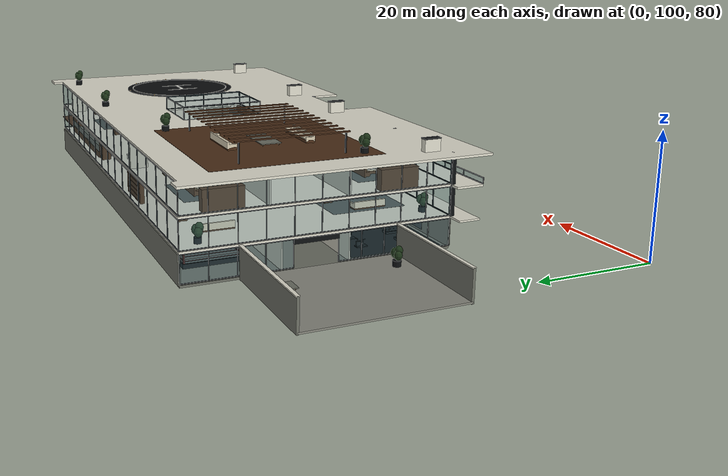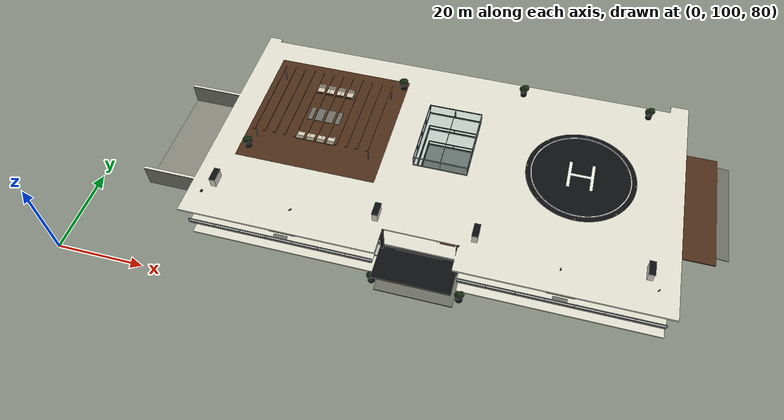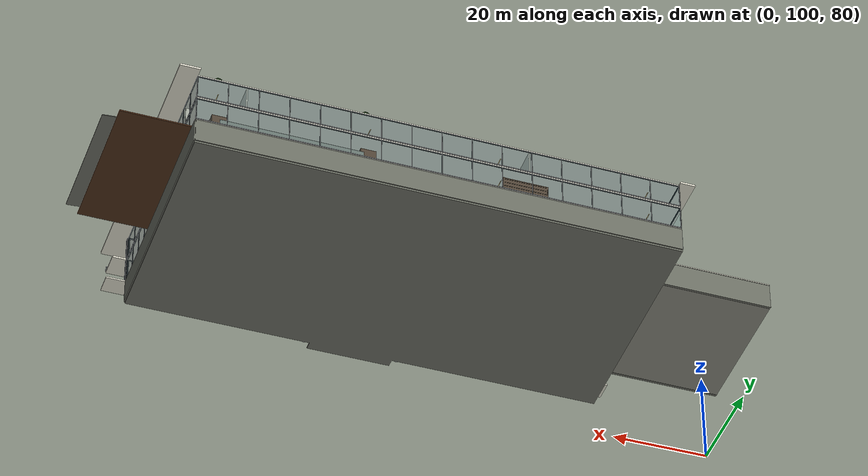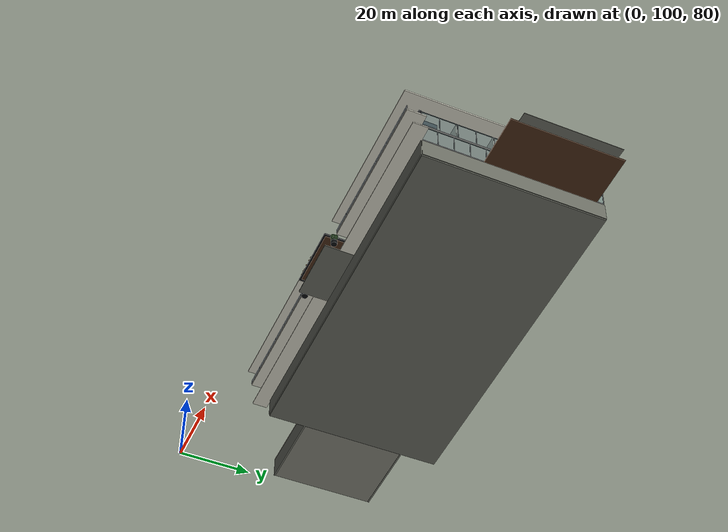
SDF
<?xml version='1.0' encoding='utf-8'?>
<sdf version="1.9">
  <model name="summit_villa">
    <static>true</static>
    <link name="structure">
      <visual name="visual_stone">
        <geometry>
          <mesh>
            <uri>model://summit_villa/meshes/visual/stone.dae</uri>
          </mesh>
        </geometry>
        <material>
          <ambient>0.42 0.43 0.39 1</ambient>
          <diffuse>0.42 0.43 0.39 1</diffuse>
          <specular>0.15 0.15 0.15 1</specular>
          <pbr>
            <metal>
              <roughness>0.8</roughness>
              <metalness>0.0</metalness>
            </metal>
          </pbr>
        </material>
      </visual>
      <visual name="visual_ivory">
        <geometry>
          <mesh>
            <uri>model://summit_villa/meshes/visual/ivory.dae</uri>
          </mesh>
        </geometry>
        <material>
          <ambient>0.88 0.87 0.81 1</ambient>
          <diffuse>0.88 0.87 0.81 1</diffuse>
          <specular>0.15 0.15 0.15 1</specular>
          <pbr>
            <metal>
              <roughness>0.8</roughness>
              <metalness>0.0</metalness>
            </metal>
          </pbr>
        </material>
      </visual>
      <visual name="visual_wood">
        <geometry>
          <mesh>
            <uri>model://summit_villa/meshes/visual/wood.dae</uri>
          </mesh>
        </geometry>
        <material>
          <ambient>0.3 0.18 0.095 1</ambient>
          <diffuse>0.3 0.18 0.095 1</diffuse>
          <specular>0.15 0.15 0.15 1</specular>
          <pbr>
            <metal>
              <roughness>0.8</roughness>
              <metalness>0.0</metalness>
            </metal>
          </pbr>
        </material>
      </visual>
      <visual name="visual_glass">
        <geometry>
          <mesh>
            <uri>model://summit_villa/meshes/visual/glass.dae</uri>
          </mesh>
        </geometry>
        <material>
          <ambient>0.36 0.58 0.63 1</ambient>
          <diffuse>0.36 0.58 0.63 1</diffuse>
          <specular>0.15 0.15 0.15 1</specular>
          <pbr>
            <metal>
              <roughness>0.16</roughness>
              <metalness>0.0</metalness>
            </metal>
          </pbr>
        </material>
        <transparency>0.78</transparency>
        <cast_shadows>false</cast_shadows>
      </visual>
      <visual name="visual_charcoal">
        <geometry>
          <mesh>
            <uri>model://summit_villa/meshes/visual/charcoal.dae</uri>
          </mesh>
        </geometry>
        <material>
          <ambient>0.045 0.054 0.06 1</ambient>
          <diffuse>0.045 0.054 0.06 1</diffuse>
          <specular>0.15 0.15 0.15 1</specular>
          <pbr>
            <metal>
              <roughness>0.8</roughness>
              <metalness>0.0</metalness>
            </metal>
          </pbr>
        </material>
      </visual>
      <visual name="visual_brass">
        <geometry>
          <mesh>
            <uri>model://summit_villa/meshes/visual/brass.dae</uri>
          </mesh>
        </geometry>
        <material>
          <ambient>0.68 0.48 0.22 1</ambient>
          <diffuse>0.68 0.48 0.22 1</diffuse>
          <specular>0.15 0.15 0.15 1</specular>
          <pbr>
            <metal>
              <roughness>0.35</roughness>
              <metalness>0.65</metalness>
            </metal>
          </pbr>
        </material>
      </visual>
      <visual name="visual_trunk">
        <geometry>
          <mesh>
            <uri>model://summit_villa/meshes/visual/trunk.dae</uri>
          </mesh>
        </geometry>
        <material>
          <ambient>0.19 0.12 0.072 1</ambient>
          <diffuse>0.19 0.12 0.072 1</diffuse>
          <specular>0.15 0.15 0.15 1</specular>
          <pbr>
            <metal>
              <roughness>0.8</roughness>
              <metalness>0.0</metalness>
            </metal>
          </pbr>
        </material>
      </visual>
      <visual name="visual_leaf1">
        <geometry>
          <mesh>
            <uri>model://summit_villa/meshes/visual/leaf1.dae</uri>
          </mesh>
        </geometry>
        <material>
          <ambient>0.105 0.195 0.085 1</ambient>
          <diffuse>0.105 0.195 0.085 1</diffuse>
          <specular>0.15 0.15 0.15 1</specular>
          <pbr>
            <metal>
              <roughness>0.8</roughness>
              <metalness>0.0</metalness>
            </metal>
          </pbr>
        </material>
      </visual>
      <visual name="visual_villa_cream">
        <geometry>
          <mesh>
            <uri>model://summit_villa/meshes/visual/villa_cream.dae</uri>
          </mesh>
        </geometry>
        <material>
          <ambient>0.83 0.79 0.69 1</ambient>
          <diffuse>0.83 0.79 0.69 1</diffuse>
          <specular>0.15 0.15 0.15 1</specular>
          <pbr>
            <metal>
              <roughness>0.91</roughness>
              <metalness>0</metalness>
            </metal>
          </pbr>
        </material>
      </visual>
      <visual name="visual_villa_bronze">
        <geometry>
          <mesh>
            <uri>model://summit_villa/meshes/visual/villa_bronze.dae</uri>
          </mesh>
        </geometry>
        <material>
          <ambient>0.24 0.16 0.075 1</ambient>
          <diffuse>0.24 0.16 0.075 1</diffuse>
          <specular>0.15 0.15 0.15 1</specular>
          <pbr>
            <metal>
              <roughness>0.32</roughness>
              <metalness>0.75</metalness>
            </metal>
          </pbr>
        </material>
      </visual>
      <visual name="visual_paving">
        <geometry>
          <mesh>
            <uri>model://summit_villa/meshes/visual/paving.dae</uri>
          </mesh>
        </geometry>
        <material>
          <ambient>0.53 0.53 0.49 1</ambient>
          <diffuse>0.53 0.53 0.49 1</diffuse>
          <specular>0.15 0.15 0.15 1</specular>
          <pbr>
            <metal>
              <roughness>0.8</roughness>
              <metalness>0.0</metalness>
            </metal>
          </pbr>
        </material>
      </visual>
      <visual name="visual_metal">
        <geometry>
          <mesh>
            <uri>model://summit_villa/meshes/visual/metal.dae</uri>
          </mesh>
        </geometry>
        <material>
          <ambient>0.21 0.23 0.24 1</ambient>
          <diffuse>0.21 0.23 0.24 1</diffuse>
          <specular>0.15 0.15 0.15 1</specular>
          <pbr>
            <metal>
              <roughness>0.35</roughness>
              <metalness>0.65</metalness>
            </metal>
          </pbr>
        </material>
      </visual>
      <visual name="visual_villa_rug">
        <geometry>
          <mesh>
            <uri>model://summit_villa/meshes/visual/villa_rug.dae</uri>
          </mesh>
        </geometry>
        <material>
          <ambient>0.29 0.32 0.31 1</ambient>
          <diffuse>0.29 0.32 0.31 1</diffuse>
          <specular>0.15 0.15 0.15 1</specular>
          <pbr>
            <metal>
              <roughness>0.97</roughness>
              <metalness>0</metalness>
            </metal>
          </pbr>
        </material>
      </visual>
      <visual name="visual_fire">
        <geometry>
          <mesh>
            <uri>model://summit_villa/meshes/visual/fire.dae</uri>
          </mesh>
        </geometry>
        <material>
          <ambient>1 0.34 0.025 1</ambient>
          <diffuse>1 0.34 0.025 1</diffuse>
          <specular>0.15 0.15 0.15 1</specular>
          <emissive>0.55 0.187 0.01375 1</emissive>
          <pbr>
            <metal>
              <roughness>0.8</roughness>
              <metalness>0.0</metalness>
            </metal>
          </pbr>
        </material>
      </visual>
      <visual name="visual_emissive">
        <geometry>
          <mesh>
            <uri>model://summit_villa/meshes/visual/emissive.dae</uri>
          </mesh>
        </geometry>
        <material>
          <ambient>0.94 0.73 0.36 1</ambient>
          <diffuse>0.94 0.73 0.36 1</diffuse>
          <specular>0.15 0.15 0.15 1</specular>
          <emissive>0.517 0.4015 0.198 1</emissive>
          <pbr>
            <metal>
              <roughness>0.8</roughness>
              <metalness>0.0</metalness>
            </metal>
          </pbr>
        </material>
      </visual>
      <visual name="visual_villa_book_red">
        <geometry>
          <mesh>
            <uri>model://summit_villa/meshes/visual/villa_book_red.dae</uri>
          </mesh>
        </geometry>
        <material>
          <ambient>0.28 0.085 0.065 1</ambient>
          <diffuse>0.28 0.085 0.065 1</diffuse>
          <specular>0.15 0.15 0.15 1</specular>
          <pbr>
            <metal>
              <roughness>0.8</roughness>
              <metalness>0</metalness>
            </metal>
          </pbr>
        </material>
      </visual>
      <visual name="visual_villa_book_blue">
        <geometry>
          <mesh>
            <uri>model://summit_villa/meshes/visual/villa_book_blue.dae</uri>
          </mesh>
        </geometry>
        <material>
          <ambient>0.08 0.17 0.23 1</ambient>
          <diffuse>0.08 0.17 0.23 1</diffuse>
          <specular>0.15 0.15 0.15 1</specular>
          <pbr>
            <metal>
              <roughness>0.8</roughness>
              <metalness>0</metalness>
            </metal>
          </pbr>
        </material>
      </visual>
      <visual name="visual_plaster">
        <geometry>
          <mesh>
            <uri>model://summit_villa/meshes/visual/plaster.dae</uri>
          </mesh>
        </geometry>
        <material>
          <ambient>0.78 0.77 0.71 1</ambient>
          <diffuse>0.78 0.77 0.71 1</diffuse>
          <specular>0.15 0.15 0.15 1</specular>
          <pbr>
            <metal>
              <roughness>0.8</roughness>
              <metalness>0.0</metalness>
            </metal>
          </pbr>
        </material>
      </visual>
      <visual name="visual_white">
        <geometry>
          <mesh>
            <uri>model://summit_villa/meshes/visual/white.dae</uri>
          </mesh>
        </geometry>
        <material>
          <ambient>0.93 0.93 0.89 1</ambient>
          <diffuse>0.93 0.93 0.89 1</diffuse>
          <specular>0.15 0.15 0.15 1</specular>
          <pbr>
            <metal>
              <roughness>0.8</roughness>
              <metalness>0.0</metalness>
            </metal>
          </pbr>
        </material>
      </visual>
      <visual name="visual_villa_cinema">
        <geometry>
          <mesh>
            <uri>model://summit_villa/meshes/visual/villa_cinema.dae</uri>
          </mesh>
        </geometry>
        <material>
          <ambient>0.045 0.055 0.067 1</ambient>
          <diffuse>0.045 0.055 0.067 1</diffuse>
          <specular>0.15 0.15 0.15 1</specular>
          <pbr>
            <metal>
              <roughness>0.96</roughness>
              <metalness>0</metalness>
            </metal>
          </pbr>
        </material>
      </visual>
      <visual name="visual_rubber">
        <geometry>
          <mesh>
            <uri>model://summit_villa/meshes/visual/rubber.dae</uri>
          </mesh>
        </geometry>
        <material>
          <ambient>0.035 0.042 0.045 1</ambient>
          <diffuse>0.035 0.042 0.045 1</diffuse>
          <specular>0.15 0.15 0.15 1</specular>
          <pbr>
            <metal>
              <roughness>0.8</roughness>
              <metalness>0.0</metalness>
            </metal>
          </pbr>
        </material>
      </visual>
      <visual name="visual_screen">
        <geometry>
          <mesh>
            <uri>model://summit_villa/meshes/visual/screen.dae</uri>
          </mesh>
        </geometry>
        <material>
          <ambient>0.11 0.28 0.38 1</ambient>
          <diffuse>0.11 0.28 0.38 1</diffuse>
          <specular>0.15 0.15 0.15 1</specular>
          <emissive>0.0605 0.154 0.209 1</emissive>
          <pbr>
            <metal>
              <roughness>0.8</roughness>
              <metalness>0.0</metalness>
            </metal>
          </pbr>
        </material>
      </visual>
      <visual name="visual_dark_fabric">
        <geometry>
          <mesh>
            <uri>model://summit_villa/meshes/visual/dark_fabric.dae</uri>
          </mesh>
        </geometry>
        <material>
          <ambient>0.095 0.12 0.14 1</ambient>
          <diffuse>0.095 0.12 0.14 1</diffuse>
          <specular>0.15 0.15 0.15 1</specular>
          <pbr>
            <metal>
              <roughness>0.8</roughness>
              <metalness>0.0</metalness>
            </metal>
          </pbr>
        </material>
      </visual>
      <collision name="basement_slab">
        <geometry>
          <box>
            <size>96 48 0.4</size>
          </box>
        </geometry>
        <pose>78 139 74.6 0 0 0</pose>
      </collision>
      <collision name="main_slab_00">
        <geometry>
          <box>
            <size>42 48 0.34</size>
          </box>
        </geometry>
        <pose>51 139 80.03 0 0 0</pose>
      </collision>
      <collision name="main_slab_01">
        <geometry>
          <box>
            <size>41 48 0.34</size>
          </box>
        </geometry>
        <pose>105.5 139 80.03 0 0 0</pose>
      </collision>
      <collision name="main_slab_02">
        <geometry>
          <box>
            <size>1 3 0.34</size>
          </box>
        </geometry>
        <pose>84.5 116.5 80.03 0 0 0</pose>
      </collision>
      <collision name="main_slab_03">
        <geometry>
          <box>
            <size>1 30 0.34</size>
          </box>
        </geometry>
        <pose>84.5 148 80.03 0 0 0</pose>
      </collision>
      <collision name="main_slab_04">
        <geometry>
          <box>
            <size>9 18 0.34</size>
          </box>
        </geometry>
        <pose>76.5 124 80.03 0 0 0</pose>
      </collision>
      <collision name="main_slab_05">
        <geometry>
          <box>
            <size>3 3 0.34</size>
          </box>
        </geometry>
        <pose>82.5 116.5 80.03 0 0 0</pose>
      </collision>
      <collision name="main_slab_06">
        <geometry>
          <box>
            <size>12 14 0.34</size>
          </box>
        </geometry>
        <pose>78 156 80.03 0 0 0</pose>
      </collision>
      <collision name="upper_slab_00">
        <geometry>
          <box>
            <size>42 48 0.34</size>
          </box>
        </geometry>
        <pose>51 139 85.63 0 0 0</pose>
      </collision>
      <collision name="upper_slab_01">
        <geometry>
          <box>
            <size>41 48 0.34</size>
          </box>
        </geometry>
        <pose>105.5 139 85.63 0 0 0</pose>
      </collision>
      <collision name="upper_slab_02">
        <geometry>
          <box>
            <size>1 3 0.34</size>
          </box>
        </geometry>
        <pose>84.5 116.5 85.63 0 0 0</pose>
      </collision>
      <collision name="upper_slab_03">
        <geometry>
          <box>
            <size>1 30 0.34</size>
          </box>
        </geometry>
        <pose>84.5 148 85.63 0 0 0</pose>
      </collision>
      <collision name="upper_slab_04">
        <geometry>
          <box>
            <size>9 18 0.34</size>
          </box>
        </geometry>
        <pose>76.5 124 85.63 0 0 0</pose>
      </collision>
      <collision name="upper_slab_05">
        <geometry>
          <box>
            <size>3 3 0.34</size>
          </box>
        </geometry>
        <pose>82.5 116.5 85.63 0 0 0</pose>
      </collision>
      <collision name="upper_slab_06">
        <geometry>
          <box>
            <size>12 14 0.34</size>
          </box>
        </geometry>
        <pose>78 156 85.63 0 0 0</pose>
      </collision>
      <collision name="roof_slab_00">
        <geometry>
          <box>
            <size>42 48 0.34</size>
          </box>
        </geometry>
        <pose>51 139 91.23 0 0 0</pose>
      </collision>
      <collision name="roof_slab_01">
        <geometry>
          <box>
            <size>42 48 0.34</size>
          </box>
        </geometry>
        <pose>105 139 91.23 0 0 0</pose>
      </collision>
      <collision name="roof_slab_02">
        <geometry>
          <box>
            <size>12 18 0.34</size>
          </box>
        </geometry>
        <pose>78 124 91.23 0 0 0</pose>
      </collision>
      <collision name="roof_slab_03">
        <geometry>
          <box>
            <size>12 14 0.34</size>
          </box>
        </geometry>
        <pose>78 156 91.23 0 0 0</pose>
      </collision>
      <collision name="west_lower_balcony">
        <geometry>
          <box>
            <size>43 4 0.32</size>
          </box>
        </geometry>
        <pose>48.5 113 80.04 0 0 0</pose>
      </collision>
      <collision name="east_lower_balcony">
        <geometry>
          <box>
            <size>43 4 0.32</size>
          </box>
        </geometry>
        <pose>108.5 113 80.04 0 0 0</pose>
      </collision>
      <collision name="main_entry_threshold">
        <geometry>
          <box>
            <size>17 8 0.28</size>
          </box>
        </geometry>
        <pose>78.5 111 80.06 0 0 0</pose>
      </collision>
      <collision name="west_upper_balcony">
        <geometry>
          <box>
            <size>41 5 0.38</size>
          </box>
        </geometry>
        <pose>48.5 112.5 85.61 0 0 0</pose>
      </collision>
      <collision name="east_upper_balcony">
        <geometry>
          <box>
            <size>42 5 0.38</size>
          </box>
        </geometry>
        <pose>108 112.5 85.61 0 0 0</pose>
      </collision>
      <collision name="west_roof_overhang">
        <geometry>
          <box>
            <size>43 6 0.42</size>
          </box>
        </geometry>
        <pose>48.5 112 91.19 0 0 0</pose>
      </collision>
      <collision name="east_roof_overhang">
        <geometry>
          <box>
            <size>44 6 0.42</size>
          </box>
        </geometry>
        <pose>108 112 91.19 0 0 0</pose>
      </collision>
      <collision name="west_roof_side_overhang">
        <geometry>
          <box>
            <size>3 49 0.42</size>
          </box>
        </geometry>
        <pose>28.5 139.5 91.19 0 0 0</pose>
      </collision>
      <collision name="east_roof_side_overhang">
        <geometry>
          <box>
            <size>4 50 0.42</size>
          </box>
        </geometry>
        <pose>128 140 91.19 0 0 0</pose>
      </collision>
      <collision name="east_pool_veranda">
        <geometry>
          <box>
            <size>14 30 0.28</size>
          </box>
        </geometry>
        <pose>133 146 80.06 0 0 0</pose>
      </collision>
      <collision name="veranda_step_0">
        <geometry>
          <box>
            <size>0.55 26 0.15</size>
          </box>
        </geometry>
        <pose>140.275 146 80.085 0 0 0</pose>
      </collision>
      <collision name="veranda_step_1">
        <geometry>
          <box>
            <size>0.55 26 0.15</size>
          </box>
        </geometry>
        <pose>140.825 146 80.045 0 0 0</pose>
      </collision>
      <collision name="veranda_step_2">
        <geometry>
          <box>
            <size>0.55 26 0.15</size>
          </box>
        </geometry>
        <pose>141.375 146 80.005 0 0 0</pose>
      </collision>
      <collision name="veranda_step_3">
        <geometry>
          <box>
            <size>0.55 26 0.15</size>
          </box>
        </geometry>
        <pose>141.925 146 79.965 0 0 0</pose>
      </collision>
      <collision name="veranda_step_4">
        <geometry>
          <box>
            <size>0.55 26 0.15</size>
          </box>
        </geometry>
        <pose>142.475 146 79.925 0 0 0</pose>
      </collision>
      <collision name="main_front_west_pane_0">
        <geometry>
          <box>
            <size>5.265 0.075 5.04</size>
          </box>
        </geometry>
        <pose>32.6875 115 82.88 0 0 0</pose>
      </collision>
      <collision name="main_front_west_pane_1">
        <geometry>
          <box>
            <size>5.265 0.075 5.04</size>
          </box>
        </geometry>
        <pose>38.0625 115 82.88 0 0 0</pose>
      </collision>
      <collision name="main_front_west_pane_2">
        <geometry>
          <box>
            <size>5.265 0.075 5.04</size>
          </box>
        </geometry>
        <pose>43.4375 115 82.88 0 0 0</pose>
      </collision>
      <collision name="main_front_west_pane_3">
        <geometry>
          <box>
            <size>5.265 0.075 5.04</size>
          </box>
        </geometry>
        <pose>48.8125 115 82.88 0 0 0</pose>
      </collision>
      <collision name="main_front_west_pane_4">
        <geometry>
          <box>
            <size>5.265 0.075 5.04</size>
          </box>
        </geometry>
        <pose>54.1875 115 82.88 0 0 0</pose>
      </collision>
      <collision name="main_front_west_pane_5">
        <geometry>
          <box>
            <size>5.265 0.075 5.04</size>
          </box>
        </geometry>
        <pose>59.5625 115 82.88 0 0 0</pose>
      </collision>
      <collision name="main_front_west_pane_6">
        <geometry>
          <box>
            <size>5.265 0.075 5.04</size>
          </box>
        </geometry>
        <pose>64.9375 115 82.88 0 0 0</pose>
      </collision>
      <collision name="main_front_west_pane_7">
        <geometry>
          <box>
            <size>5.265 0.075 5.04</size>
          </box>
        </geometry>
        <pose>70.3125 115 82.88 0 0 0</pose>
      </collision>
      <collision name="main_front_west_mullion_0">
        <geometry>
          <box>
            <size>0.115 0.19 5.04</size>
          </box>
        </geometry>
        <pose>30 115 82.88 0 0 0</pose>
      </collision>
      <collision name="main_front_west_mullion_1">
        <geometry>
          <box>
            <size>0.115 0.19 5.04</size>
          </box>
        </geometry>
        <pose>35.375 115 82.88 0 0 0</pose>
      </collision>
      <collision name="main_front_west_mullion_2">
        <geometry>
          <box>
            <size>0.115 0.19 5.04</size>
          </box>
        </geometry>
        <pose>40.75 115 82.88 0 0 0</pose>
      </collision>
      <collision name="main_front_west_mullion_3">
        <geometry>
          <box>
            <size>0.115 0.19 5.04</size>
          </box>
        </geometry>
        <pose>46.125 115 82.88 0 0 0</pose>
      </collision>
      <collision name="main_front_west_mullion_4">
        <geometry>
          <box>
            <size>0.115 0.19 5.04</size>
          </box>
        </geometry>
        <pose>51.5 115 82.88 0 0 0</pose>
      </collision>
      <collision name="main_front_west_mullion_5">
        <geometry>
          <box>
            <size>0.115 0.19 5.04</size>
          </box>
        </geometry>
        <pose>56.875 115 82.88 0 0 0</pose>
      </collision>
      <collision name="main_front_west_mullion_6">
        <geometry>
          <box>
            <size>0.115 0.19 5.04</size>
          </box>
        </geometry>
        <pose>62.25 115 82.88 0 0 0</pose>
      </collision>
      <collision name="main_front_west_mullion_7">
        <geometry>
          <box>
            <size>0.115 0.19 5.04</size>
          </box>
        </geometry>
        <pose>67.625 115 82.88 0 0 0</pose>
      </collision>
      <collision name="main_front_west_mullion_8">
        <geometry>
          <box>
            <size>0.115 0.19 5.04</size>
          </box>
        </geometry>
        <pose>73 115 82.88 0 0 0</pose>
      </collision>
      <collision name="main_front_west_transom_80.36">
        <geometry>
          <box>
            <size>43 0.2 0.13</size>
          </box>
        </geometry>
        <pose>51.5 115 80.36 0 0 0</pose>
      </collision>
      <collision name="main_front_west_transom_85.4">
        <geometry>
          <box>
            <size>43 0.2 0.13</size>
          </box>
        </geometry>
        <pose>51.5 115 85.4 0 0 0</pose>
      </collision>
      <collision name="main_front_east_pane_0">
        <geometry>
          <box>
            <size>5.265 0.075 5.04</size>
          </box>
        </geometry>
        <pose>85.6875 115 82.88 0 0 0</pose>
      </collision>
      <collision name="main_front_east_pane_1">
        <geometry>
          <box>
            <size>5.265 0.075 5.04</size>
          </box>
        </geometry>
        <pose>91.0625 115 82.88 0 0 0</pose>
      </collision>
      <collision name="main_front_east_pane_2">
        <geometry>
          <box>
            <size>5.265 0.075 5.04</size>
          </box>
        </geometry>
        <pose>96.4375 115 82.88 0 0 0</pose>
      </collision>
      <collision name="main_front_east_pane_3">
        <geometry>
          <box>
            <size>5.265 0.075 5.04</size>
          </box>
        </geometry>
        <pose>101.812 115 82.88 0 0 0</pose>
      </collision>
      <collision name="main_front_east_pane_4">
        <geometry>
          <box>
            <size>5.265 0.075 5.04</size>
          </box>
        </geometry>
        <pose>107.188 115 82.88 0 0 0</pose>
      </collision>
      <collision name="main_front_east_pane_5">
        <geometry>
          <box>
            <size>5.265 0.075 5.04</size>
          </box>
        </geometry>
        <pose>112.562 115 82.88 0 0 0</pose>
      </collision>
      <collision name="main_front_east_pane_6">
        <geometry>
          <box>
            <size>5.265 0.075 5.04</size>
          </box>
        </geometry>
        <pose>117.938 115 82.88 0 0 0</pose>
      </collision>
      <collision name="main_front_east_pane_7">
        <geometry>
          <box>
            <size>5.265 0.075 5.04</size>
          </box>
        </geometry>
        <pose>123.312 115 82.88 0 0 0</pose>
      </collision>
      <collision name="main_front_east_mullion_0">
        <geometry>
          <box>
            <size>0.115 0.19 5.04</size>
          </box>
        </geometry>
        <pose>83 115 82.88 0 0 0</pose>
      </collision>
      <collision name="main_front_east_mullion_1">
        <geometry>
          <box>
            <size>0.115 0.19 5.04</size>
          </box>
        </geometry>
        <pose>88.375 115 82.88 0 0 0</pose>
      </collision>
      <collision name="main_front_east_mullion_2">
        <geometry>
          <box>
            <size>0.115 0.19 5.04</size>
          </box>
        </geometry>
        <pose>93.75 115 82.88 0 0 0</pose>
      </collision>
      <collision name="main_front_east_mullion_3">
        <geometry>
          <box>
            <size>0.115 0.19 5.04</size>
          </box>
        </geometry>
        <pose>99.125 115 82.88 0 0 0</pose>
      </collision>
      <collision name="main_front_east_mullion_4">
        <geometry>
          <box>
            <size>0.115 0.19 5.04</size>
          </box>
        </geometry>
        <pose>104.5 115 82.88 0 0 0</pose>
      </collision>
      <collision name="main_front_east_mullion_5">
        <geometry>
          <box>
            <size>0.115 0.19 5.04</size>
          </box>
        </geometry>
        <pose>109.875 115 82.88 0 0 0</pose>
      </collision>
      <collision name="main_front_east_mullion_6">
        <geometry>
          <box>
            <size>0.115 0.19 5.04</size>
          </box>
        </geometry>
        <pose>115.25 115 82.88 0 0 0</pose>
      </collision>
      <collision name="main_front_east_mullion_7">
        <geometry>
          <box>
            <size>0.115 0.19 5.04</size>
          </box>
        </geometry>
        <pose>120.625 115 82.88 0 0 0</pose>
      </collision>
      <collision name="main_front_east_mullion_8">
        <geometry>
          <box>
            <size>0.115 0.19 5.04</size>
          </box>
        </geometry>
        <pose>126 115 82.88 0 0 0</pose>
      </collision>
      <collision name="main_front_east_transom_80.36">
        <geometry>
          <box>
            <size>43 0.2 0.13</size>
          </box>
        </geometry>
        <pose>104.5 115 80.36 0 0 0</pose>
      </collision>
      <collision name="main_front_east_transom_85.4">
        <geometry>
          <box>
            <size>43 0.2 0.13</size>
          </box>
        </geometry>
        <pose>104.5 115 85.4 0 0 0</pose>
      </collision>
      <collision name="entry_header">
        <geometry>
          <box>
            <size>10 0.6 1.06</size>
          </box>
        </geometry>
        <pose>78 115 84.93 0 0 0</pose>
      </collision>
      <collision name="main_rear_pane_0">
        <geometry>
          <box>
            <size>5.89 0.075 5.04</size>
          </box>
        </geometry>
        <pose>33 163 82.88 0 0 0</pose>
      </collision>
      <collision name="main_rear_pane_1">
        <geometry>
          <box>
            <size>5.89 0.075 5.04</size>
          </box>
        </geometry>
        <pose>39 163 82.88 0 0 0</pose>
      </collision>
      <collision name="main_rear_pane_2">
        <geometry>
          <box>
            <size>5.89 0.075 5.04</size>
          </box>
        </geometry>
        <pose>45 163 82.88 0 0 0</pose>
      </collision>
      <collision name="main_rear_pane_3">
        <geometry>
          <box>
            <size>5.89 0.075 5.04</size>
          </box>
        </geometry>
        <pose>51 163 82.88 0 0 0</pose>
      </collision>
      <collision name="main_rear_pane_4">
        <geometry>
          <box>
            <size>5.89 0.075 5.04</size>
          </box>
        </geometry>
        <pose>57 163 82.88 0 0 0</pose>
      </collision>
      <collision name="main_rear_pane_5">
        <geometry>
          <box>
            <size>5.89 0.075 5.04</size>
          </box>
        </geometry>
        <pose>63 163 82.88 0 0 0</pose>
      </collision>
      <collision name="main_rear_pane_6">
        <geometry>
          <box>
            <size>5.89 0.075 5.04</size>
          </box>
        </geometry>
        <pose>69 163 82.88 0 0 0</pose>
      </collision>
      <collision name="main_rear_pane_7">
        <geometry>
          <box>
            <size>5.89 0.075 5.04</size>
          </box>
        </geometry>
        <pose>75 163 82.88 0 0 0</pose>
      </collision>
      <collision name="main_rear_pane_8">
        <geometry>
          <box>
            <size>5.89 0.075 5.04</size>
          </box>
        </geometry>
        <pose>81 163 82.88 0 0 0</pose>
      </collision>
      <collision name="main_rear_pane_9">
        <geometry>
          <box>
            <size>5.89 0.075 5.04</size>
          </box>
        </geometry>
        <pose>87 163 82.88 0 0 0</pose>
      </collision>
      <collision name="main_rear_pane_10">
        <geometry>
          <box>
            <size>5.89 0.075 5.04</size>
          </box>
        </geometry>
        <pose>93 163 82.88 0 0 0</pose>
      </collision>
      <collision name="main_rear_pane_11">
        <geometry>
          <box>
            <size>5.89 0.075 5.04</size>
          </box>
        </geometry>
        <pose>99 163 82.88 0 0 0</pose>
      </collision>
      <collision name="main_rear_pane_12">
        <geometry>
          <box>
            <size>5.89 0.075 5.04</size>
          </box>
        </geometry>
        <pose>105 163 82.88 0 0 0</pose>
      </collision>
      <collision name="main_rear_pane_13">
        <geometry>
          <box>
            <size>5.89 0.075 5.04</size>
          </box>
        </geometry>
        <pose>111 163 82.88 0 0 0</pose>
      </collision>
      <collision name="main_rear_pane_14">
        <geometry>
          <box>
            <size>5.89 0.075 5.04</size>
          </box>
        </geometry>
        <pose>117 163 82.88 0 0 0</pose>
      </collision>
      <collision name="main_rear_pane_15">
        <geometry>
          <box>
            <size>5.89 0.075 5.04</size>
          </box>
        </geometry>
        <pose>123 163 82.88 0 0 0</pose>
      </collision>
      <collision name="main_rear_mullion_0">
        <geometry>
          <box>
            <size>0.115 0.19 5.04</size>
          </box>
        </geometry>
        <pose>30 163 82.88 0 0 0</pose>
      </collision>
      <collision name="main_rear_mullion_1">
        <geometry>
          <box>
            <size>0.115 0.19 5.04</size>
          </box>
        </geometry>
        <pose>36 163 82.88 0 0 0</pose>
      </collision>
      <collision name="main_rear_mullion_2">
        <geometry>
          <box>
            <size>0.115 0.19 5.04</size>
          </box>
        </geometry>
        <pose>42 163 82.88 0 0 0</pose>
      </collision>
      <collision name="main_rear_mullion_3">
        <geometry>
          <box>
            <size>0.115 0.19 5.04</size>
          </box>
        </geometry>
        <pose>48 163 82.88 0 0 0</pose>
      </collision>
      <collision name="main_rear_mullion_4">
        <geometry>
          <box>
            <size>0.115 0.19 5.04</size>
          </box>
        </geometry>
        <pose>54 163 82.88 0 0 0</pose>
      </collision>
      <collision name="main_rear_mullion_5">
        <geometry>
          <box>
            <size>0.115 0.19 5.04</size>
          </box>
        </geometry>
        <pose>60 163 82.88 0 0 0</pose>
      </collision>
      <collision name="main_rear_mullion_6">
        <geometry>
          <box>
            <size>0.115 0.19 5.04</size>
          </box>
        </geometry>
        <pose>66 163 82.88 0 0 0</pose>
      </collision>
      <collision name="main_rear_mullion_7">
        <geometry>
          <box>
            <size>0.115 0.19 5.04</size>
          </box>
        </geometry>
        <pose>72 163 82.88 0 0 0</pose>
      </collision>
      <collision name="main_rear_mullion_8">
        <geometry>
          <box>
            <size>0.115 0.19 5.04</size>
          </box>
        </geometry>
        <pose>78 163 82.88 0 0 0</pose>
      </collision>
      <collision name="main_rear_mullion_9">
        <geometry>
          <box>
            <size>0.115 0.19 5.04</size>
          </box>
        </geometry>
        <pose>84 163 82.88 0 0 0</pose>
      </collision>
      <collision name="main_rear_mullion_10">
        <geometry>
          <box>
            <size>0.115 0.19 5.04</size>
          </box>
        </geometry>
        <pose>90 163 82.88 0 0 0</pose>
      </collision>
      <collision name="main_rear_mullion_11">
        <geometry>
          <box>
            <size>0.115 0.19 5.04</size>
          </box>
        </geometry>
        <pose>96 163 82.88 0 0 0</pose>
      </collision>
      <collision name="main_rear_mullion_12">
        <geometry>
          <box>
            <size>0.115 0.19 5.04</size>
          </box>
        </geometry>
        <pose>102 163 82.88 0 0 0</pose>
      </collision>
      <collision name="main_rear_mullion_13">
        <geometry>
          <box>
            <size>0.115 0.19 5.04</size>
          </box>
        </geometry>
        <pose>108 163 82.88 0 0 0</pose>
      </collision>
      <collision name="main_rear_mullion_14">
        <geometry>
          <box>
            <size>0.115 0.19 5.04</size>
          </box>
        </geometry>
        <pose>114 163 82.88 0 0 0</pose>
      </collision>
      <collision name="main_rear_mullion_15">
        <geometry>
          <box>
            <size>0.115 0.19 5.04</size>
          </box>
        </geometry>
        <pose>120 163 82.88 0 0 0</pose>
      </collision>
      <collision name="main_rear_mullion_16">
        <geometry>
          <box>
            <size>0.115 0.19 5.04</size>
          </box>
        </geometry>
        <pose>126 163 82.88 0 0 0</pose>
      </collision>
      <collision name="main_rear_transom_80.36">
        <geometry>
          <box>
            <size>96 0.2 0.13</size>
          </box>
        </geometry>
        <pose>78 163 80.36 0 0 0</pose>
      </collision>
      <collision name="main_rear_transom_85.4">
        <geometry>
          <box>
            <size>96 0.2 0.13</size>
          </box>
        </geometry>
        <pose>78 163 85.4 0 0 0</pose>
      </collision>
      <collision name="main_west_pane_0">
        <geometry>
          <box>
            <size>0.075 4.69 5.04</size>
          </box>
        </geometry>
        <pose>30 117.4 82.88 0 0 0</pose>
      </collision>
      <collision name="main_west_pane_1">
        <geometry>
          <box>
            <size>0.075 4.69 5.04</size>
          </box>
        </geometry>
        <pose>30 122.2 82.88 0 0 0</pose>
      </collision>
      <collision name="main_west_pane_2">
        <geometry>
          <box>
            <size>0.075 4.69 5.04</size>
          </box>
        </geometry>
        <pose>30 127 82.88 0 0 0</pose>
      </collision>
      <collision name="main_west_pane_3">
        <geometry>
          <box>
            <size>0.075 4.69 5.04</size>
          </box>
        </geometry>
        <pose>30 131.8 82.88 0 0 0</pose>
      </collision>
      <collision name="main_west_pane_4">
        <geometry>
          <box>
            <size>0.075 4.69 5.04</size>
          </box>
        </geometry>
        <pose>30 136.6 82.88 0 0 0</pose>
      </collision>
      <collision name="main_west_pane_5">
        <geometry>
          <box>
            <size>0.075 4.69 5.04</size>
          </box>
        </geometry>
        <pose>30 141.4 82.88 0 0 0</pose>
      </collision>
      <collision name="main_west_pane_6">
        <geometry>
          <box>
            <size>0.075 4.69 5.04</size>
          </box>
        </geometry>
        <pose>30 146.2 82.88 0 0 0</pose>
      </collision>
      <collision name="main_west_pane_7">
        <geometry>
          <box>
            <size>0.075 4.69 5.04</size>
          </box>
        </geometry>
        <pose>30 151 82.88 0 0 0</pose>
      </collision>
      <collision name="main_west_pane_8">
        <geometry>
          <box>
            <size>0.075 4.69 5.04</size>
          </box>
        </geometry>
        <pose>30 155.8 82.88 0 0 0</pose>
      </collision>
      <collision name="main_west_pane_9">
        <geometry>
          <box>
            <size>0.075 4.69 5.04</size>
          </box>
        </geometry>
        <pose>30 160.6 82.88 0 0 0</pose>
      </collision>
      <collision name="main_west_mullion_0">
        <geometry>
          <box>
            <size>0.19 0.115 5.04</size>
          </box>
        </geometry>
        <pose>30 115 82.88 0 0 0</pose>
      </collision>
      <collision name="main_west_mullion_1">
        <geometry>
          <box>
            <size>0.19 0.115 5.04</size>
          </box>
        </geometry>
        <pose>30 119.8 82.88 0 0 0</pose>
      </collision>
      <collision name="main_west_mullion_2">
        <geometry>
          <box>
            <size>0.19 0.115 5.04</size>
          </box>
        </geometry>
        <pose>30 124.6 82.88 0 0 0</pose>
      </collision>
      <collision name="main_west_mullion_3">
        <geometry>
          <box>
            <size>0.19 0.115 5.04</size>
          </box>
        </geometry>
        <pose>30 129.4 82.88 0 0 0</pose>
      </collision>
      <collision name="main_west_mullion_4">
        <geometry>
          <box>
            <size>0.19 0.115 5.04</size>
          </box>
        </geometry>
        <pose>30 134.2 82.88 0 0 0</pose>
      </collision>
      <collision name="main_west_mullion_5">
        <geometry>
          <box>
            <size>0.19 0.115 5.04</size>
          </box>
        </geometry>
        <pose>30 139 82.88 0 0 0</pose>
      </collision>
      <collision name="main_west_mullion_6">
        <geometry>
          <box>
            <size>0.19 0.115 5.04</size>
          </box>
        </geometry>
        <pose>30 143.8 82.88 0 0 0</pose>
      </collision>
      <collision name="main_west_mullion_7">
        <geometry>
          <box>
            <size>0.19 0.115 5.04</size>
          </box>
        </geometry>
        <pose>30 148.6 82.88 0 0 0</pose>
      </collision>
      <collision name="main_west_mullion_8">
        <geometry>
          <box>
            <size>0.19 0.115 5.04</size>
          </box>
        </geometry>
        <pose>30 153.4 82.88 0 0 0</pose>
      </collision>
      <collision name="main_west_mullion_9">
        <geometry>
          <box>
            <size>0.19 0.115 5.04</size>
          </box>
        </geometry>
        <pose>30 158.2 82.88 0 0 0</pose>
      </collision>
      <collision name="main_west_mullion_10">
        <geometry>
          <box>
            <size>0.19 0.115 5.04</size>
          </box>
        </geometry>
        <pose>30 163 82.88 0 0 0</pose>
      </collision>
      <collision name="main_west_transom_80.36">
        <geometry>
          <box>
            <size>0.2 48 0.13</size>
          </box>
        </geometry>
        <pose>30 139 80.36 0 0 0</pose>
      </collision>
      <collision name="main_west_transom_85.4">
        <geometry>
          <box>
            <size>0.2 48 0.13</size>
          </box>
        </geometry>
        <pose>30 139 85.4 0 0 0</pose>
      </collision>
      <collision name="main_east_south_pane_0">
        <geometry>
          <box>
            <size>0.075 4.09 5.04</size>
          </box>
        </geometry>
        <pose>126 117.1 82.88 0 0 0</pose>
      </collision>
      <collision name="main_east_south_pane_1">
        <geometry>
          <box>
            <size>0.075 4.09 5.04</size>
          </box>
        </geometry>
        <pose>126 121.3 82.88 0 0 0</pose>
      </collision>
      <collision name="main_east_south_pane_2">
        <geometry>
          <box>
            <size>0.075 4.09 5.04</size>
          </box>
        </geometry>
        <pose>126 125.5 82.88 0 0 0</pose>
      </collision>
      <collision name="main_east_south_pane_3">
        <geometry>
          <box>
            <size>0.075 4.09 5.04</size>
          </box>
        </geometry>
        <pose>126 129.7 82.88 0 0 0</pose>
      </collision>
      <collision name="main_east_south_pane_4">
        <geometry>
          <box>
            <size>0.075 4.09 5.04</size>
          </box>
        </geometry>
        <pose>126 133.9 82.88 0 0 0</pose>
      </collision>
      <collision name="main_east_south_mullion_0">
        <geometry>
          <box>
            <size>0.19 0.115 5.04</size>
          </box>
        </geometry>
        <pose>126 115 82.88 0 0 0</pose>
      </collision>
      <collision name="main_east_south_mullion_1">
        <geometry>
          <box>
            <size>0.19 0.115 5.04</size>
          </box>
        </geometry>
        <pose>126 119.2 82.88 0 0 0</pose>
      </collision>
      <collision name="main_east_south_mullion_2">
        <geometry>
          <box>
            <size>0.19 0.115 5.04</size>
          </box>
        </geometry>
        <pose>126 123.4 82.88 0 0 0</pose>
      </collision>
      <collision name="main_east_south_mullion_3">
        <geometry>
          <box>
            <size>0.19 0.115 5.04</size>
          </box>
        </geometry>
        <pose>126 127.6 82.88 0 0 0</pose>
      </collision>
      <collision name="main_east_south_mullion_4">
        <geometry>
          <box>
            <size>0.19 0.115 5.04</size>
          </box>
        </geometry>
        <pose>126 131.8 82.88 0 0 0</pose>
      </collision>
      <collision name="main_east_south_mullion_5">
        <geometry>
          <box>
            <size>0.19 0.115 5.04</size>
          </box>
        </geometry>
        <pose>126 136 82.88 0 0 0</pose>
      </collision>
      <collision name="main_east_south_transom_80.36">
        <geometry>
          <box>
            <size>0.2 21 0.13</size>
          </box>
        </geometry>
        <pose>126 125.5 80.36 0 0 0</pose>
      </collision>
      <collision name="main_east_south_transom_85.4">
        <geometry>
          <box>
            <size>0.2 21 0.13</size>
          </box>
        </geometry>
        <pose>126 125.5 85.4 0 0 0</pose>
      </collision>
      <collision name="main_east_north_pane_0">
        <geometry>
          <box>
            <size>0.075 4.64 5.04</size>
          </box>
        </geometry>
        <pose>126 146.375 82.88 0 0 0</pose>
      </collision>
      <collision name="main_east_north_pane_1">
        <geometry>
          <box>
            <size>0.075 4.64 5.04</size>
          </box>
        </geometry>
        <pose>126 151.125 82.88 0 0 0</pose>
      </collision>
      <collision name="main_east_north_pane_2">
        <geometry>
          <box>
            <size>0.075 4.64 5.04</size>
          </box>
        </geometry>
        <pose>126 155.875 82.88 0 0 0</pose>
      </collision>
      <collision name="main_east_north_pane_3">
        <geometry>
          <box>
            <size>0.075 4.64 5.04</size>
          </box>
        </geometry>
        <pose>126 160.625 82.88 0 0 0</pose>
      </collision>
      <collision name="main_east_north_mullion_0">
        <geometry>
          <box>
            <size>0.19 0.115 5.04</size>
          </box>
        </geometry>
        <pose>126 144 82.88 0 0 0</pose>
      </collision>
      <collision name="main_east_north_mullion_1">
        <geometry>
          <box>
            <size>0.19 0.115 5.04</size>
          </box>
        </geometry>
        <pose>126 148.75 82.88 0 0 0</pose>
      </collision>
      <collision name="main_east_north_mullion_2">
        <geometry>
          <box>
            <size>0.19 0.115 5.04</size>
          </box>
        </geometry>
        <pose>126 153.5 82.88 0 0 0</pose>
      </collision>
      <collision name="main_east_north_mullion_3">
        <geometry>
          <box>
            <size>0.19 0.115 5.04</size>
          </box>
        </geometry>
        <pose>126 158.25 82.88 0 0 0</pose>
      </collision>
      <collision name="main_east_north_mullion_4">
        <geometry>
          <box>
            <size>0.19 0.115 5.04</size>
          </box>
        </geometry>
        <pose>126 163 82.88 0 0 0</pose>
      </collision>
      <collision name="main_east_north_transom_80.36">
        <geometry>
          <box>
            <size>0.2 19 0.13</size>
          </box>
        </geometry>
        <pose>126 153.5 80.36 0 0 0</pose>
      </collision>
      <collision name="main_east_north_transom_85.4">
        <geometry>
          <box>
            <size>0.2 19 0.13</size>
          </box>
        </geometry>
        <pose>126 153.5 85.4 0 0 0</pose>
      </collision>
      <collision name="pool_door_header">
        <geometry>
          <box>
            <size>0.5 8 1.06</size>
          </box>
        </geometry>
        <pose>126 140 84.93 0 0 0</pose>
      </collision>
      <collision name="upper_front_west_pane_0">
        <geometry>
          <box>
            <size>5.60429 0.075 5.04</size>
          </box>
        </geometry>
        <pose>32.8571 115 88.48 0 0 0</pose>
      </collision>
      <collision name="upper_front_west_pane_1">
        <geometry>
          <box>
            <size>5.60429 0.075 5.04</size>
          </box>
        </geometry>
        <pose>38.5714 115 88.48 0 0 0</pose>
      </collision>
      <collision name="upper_front_west_pane_2">
        <geometry>
          <box>
            <size>5.60429 0.075 5.04</size>
          </box>
        </geometry>
        <pose>44.2857 115 88.48 0 0 0</pose>
      </collision>
      <collision name="upper_front_west_pane_3">
        <geometry>
          <box>
            <size>5.60429 0.075 5.04</size>
          </box>
        </geometry>
        <pose>50 115 88.48 0 0 0</pose>
      </collision>
      <collision name="upper_front_west_pane_4">
        <geometry>
          <box>
            <size>5.60429 0.075 5.04</size>
          </box>
        </geometry>
        <pose>55.7143 115 88.48 0 0 0</pose>
      </collision>
      <collision name="upper_front_west_pane_5">
        <geometry>
          <box>
            <size>5.60429 0.075 5.04</size>
          </box>
        </geometry>
        <pose>61.4286 115 88.48 0 0 0</pose>
      </collision>
      <collision name="upper_front_west_pane_6">
        <geometry>
          <box>
            <size>5.60429 0.075 5.04</size>
          </box>
        </geometry>
        <pose>67.1429 115 88.48 0 0 0</pose>
      </collision>
      <collision name="upper_front_west_mullion_0">
        <geometry>
          <box>
            <size>0.115 0.19 5.04</size>
          </box>
        </geometry>
        <pose>30 115 88.48 0 0 0</pose>
      </collision>
      <collision name="upper_front_west_mullion_1">
        <geometry>
          <box>
            <size>0.115 0.19 5.04</size>
          </box>
        </geometry>
        <pose>35.7143 115 88.48 0 0 0</pose>
      </collision>
      <collision name="upper_front_west_mullion_2">
        <geometry>
          <box>
            <size>0.115 0.19 5.04</size>
          </box>
        </geometry>
        <pose>41.4286 115 88.48 0 0 0</pose>
      </collision>
      <collision name="upper_front_west_mullion_3">
        <geometry>
          <box>
            <size>0.115 0.19 5.04</size>
          </box>
        </geometry>
        <pose>47.1429 115 88.48 0 0 0</pose>
      </collision>
      <collision name="upper_front_west_mullion_4">
        <geometry>
          <box>
            <size>0.115 0.19 5.04</size>
          </box>
        </geometry>
        <pose>52.8571 115 88.48 0 0 0</pose>
      </collision>
      <collision name="upper_front_west_mullion_5">
        <geometry>
          <box>
            <size>0.115 0.19 5.04</size>
          </box>
        </geometry>
        <pose>58.5714 115 88.48 0 0 0</pose>
      </collision>
      <collision name="upper_front_west_mullion_6">
        <geometry>
          <box>
            <size>0.115 0.19 5.04</size>
          </box>
        </geometry>
        <pose>64.2857 115 88.48 0 0 0</pose>
      </collision>
      <collision name="upper_front_west_mullion_7">
        <geometry>
          <box>
            <size>0.115 0.19 5.04</size>
          </box>
        </geometry>
        <pose>70 115 88.48 0 0 0</pose>
      </collision>
      <collision name="upper_front_west_transom_85.96">
        <geometry>
          <box>
            <size>40 0.2 0.13</size>
          </box>
        </geometry>
        <pose>50 115 85.96 0 0 0</pose>
      </collision>
      <collision name="upper_front_west_transom_91">
        <geometry>
          <box>
            <size>40 0.2 0.13</size>
          </box>
        </geometry>
        <pose>50 115 91 0 0 0</pose>
      </collision>
      <collision name="upper_front_center_pane_0">
        <geometry>
          <box>
            <size>5.55667 0.075 5.04</size>
          </box>
        </geometry>
        <pose>72.8333 119 88.48 0 0 0</pose>
      </collision>
      <collision name="upper_front_center_pane_1">
        <geometry>
          <box>
            <size>5.55667 0.075 5.04</size>
          </box>
        </geometry>
        <pose>78.5 119 88.48 0 0 0</pose>
      </collision>
      <collision name="upper_front_center_pane_2">
        <geometry>
          <box>
            <size>5.55667 0.075 5.04</size>
          </box>
        </geometry>
        <pose>84.1667 119 88.48 0 0 0</pose>
      </collision>
      <collision name="upper_front_center_mullion_0">
        <geometry>
          <box>
            <size>0.115 0.19 5.04</size>
          </box>
        </geometry>
        <pose>70 119 88.48 0 0 0</pose>
      </collision>
      <collision name="upper_front_center_mullion_1">
        <geometry>
          <box>
            <size>0.115 0.19 5.04</size>
          </box>
        </geometry>
        <pose>75.6667 119 88.48 0 0 0</pose>
      </collision>
      <collision name="upper_front_center_mullion_2">
        <geometry>
          <box>
            <size>0.115 0.19 5.04</size>
          </box>
        </geometry>
        <pose>81.3333 119 88.48 0 0 0</pose>
      </collision>
      <collision name="upper_front_center_mullion_3">
        <geometry>
          <box>
            <size>0.115 0.19 5.04</size>
          </box>
        </geometry>
        <pose>87 119 88.48 0 0 0</pose>
      </collision>
      <collision name="upper_front_center_transom_85.96">
        <geometry>
          <box>
            <size>17 0.2 0.13</size>
          </box>
        </geometry>
        <pose>78.5 119 85.96 0 0 0</pose>
      </collision>
      <collision name="upper_front_center_transom_91">
        <geometry>
          <box>
            <size>17 0.2 0.13</size>
          </box>
        </geometry>
        <pose>78.5 119 91 0 0 0</pose>
      </collision>
      <collision name="upper_front_east_pane_0">
        <geometry>
          <box>
            <size>5.46143 0.075 5.04</size>
          </box>
        </geometry>
        <pose>89.7857 115 88.48 0 0 0</pose>
      </collision>
      <collision name="upper_front_east_pane_1">
        <geometry>
          <box>
            <size>5.46143 0.075 5.04</size>
          </box>
        </geometry>
        <pose>95.3571 115 88.48 0 0 0</pose>
      </collision>
      <collision name="upper_front_east_pane_2">
        <geometry>
          <box>
            <size>5.46143 0.075 5.04</size>
          </box>
        </geometry>
        <pose>100.929 115 88.48 0 0 0</pose>
      </collision>
      <collision name="upper_front_east_pane_3">
        <geometry>
          <box>
            <size>5.46143 0.075 5.04</size>
          </box>
        </geometry>
        <pose>106.5 115 88.48 0 0 0</pose>
      </collision>
      <collision name="upper_front_east_pane_4">
        <geometry>
          <box>
            <size>5.46143 0.075 5.04</size>
          </box>
        </geometry>
        <pose>112.071 115 88.48 0 0 0</pose>
      </collision>
      <collision name="upper_front_east_pane_5">
        <geometry>
          <box>
            <size>5.46143 0.075 5.04</size>
          </box>
        </geometry>
        <pose>117.643 115 88.48 0 0 0</pose>
      </collision>
      <collision name="upper_front_east_pane_6">
        <geometry>
          <box>
            <size>5.46143 0.075 5.04</size>
          </box>
        </geometry>
        <pose>123.214 115 88.48 0 0 0</pose>
      </collision>
      <collision name="upper_front_east_mullion_0">
        <geometry>
          <box>
            <size>0.115 0.19 5.04</size>
          </box>
        </geometry>
        <pose>87 115 88.48 0 0 0</pose>
      </collision>
      <collision name="upper_front_east_mullion_1">
        <geometry>
          <box>
            <size>0.115 0.19 5.04</size>
          </box>
        </geometry>
        <pose>92.5714 115 88.48 0 0 0</pose>
      </collision>
      <collision name="upper_front_east_mullion_2">
        <geometry>
          <box>
            <size>0.115 0.19 5.04</size>
          </box>
        </geometry>
        <pose>98.1429 115 88.48 0 0 0</pose>
      </collision>
      <collision name="upper_front_east_mullion_3">
        <geometry>
          <box>
            <size>0.115 0.19 5.04</size>
          </box>
        </geometry>
        <pose>103.714 115 88.48 0 0 0</pose>
      </collision>
      <collision name="upper_front_east_mullion_4">
        <geometry>
          <box>
            <size>0.115 0.19 5.04</size>
          </box>
        </geometry>
        <pose>109.286 115 88.48 0 0 0</pose>
      </collision>
      <collision name="upper_front_east_mullion_5">
        <geometry>
          <box>
            <size>0.115 0.19 5.04</size>
          </box>
        </geometry>
        <pose>114.857 115 88.48 0 0 0</pose>
      </collision>
      <collision name="upper_front_east_mullion_6">
        <geometry>
          <box>
            <size>0.115 0.19 5.04</size>
          </box>
        </geometry>
        <pose>120.429 115 88.48 0 0 0</pose>
      </collision>
      <collision name="upper_front_east_mullion_7">
        <geometry>
          <box>
            <size>0.115 0.19 5.04</size>
          </box>
        </geometry>
        <pose>126 115 88.48 0 0 0</pose>
      </collision>
      <collision name="upper_front_east_transom_85.96">
        <geometry>
          <box>
            <size>39 0.2 0.13</size>
          </box>
        </geometry>
        <pose>106.5 115 85.96 0 0 0</pose>
      </collision>
      <collision name="upper_front_east_transom_91">
        <geometry>
          <box>
            <size>39 0.2 0.13</size>
          </box>
        </geometry>
        <pose>106.5 115 91 0 0 0</pose>
      </collision>
      <collision name="upper_rear_pane_0">
        <geometry>
          <box>
            <size>5.89 0.075 5.04</size>
          </box>
        </geometry>
        <pose>33 163 88.48 0 0 0</pose>
      </collision>
      <collision name="upper_rear_pane_1">
        <geometry>
          <box>
            <size>5.89 0.075 5.04</size>
          </box>
        </geometry>
        <pose>39 163 88.48 0 0 0</pose>
      </collision>
      <collision name="upper_rear_pane_2">
        <geometry>
          <box>
            <size>5.89 0.075 5.04</size>
          </box>
        </geometry>
        <pose>45 163 88.48 0 0 0</pose>
      </collision>
      <collision name="upper_rear_pane_3">
        <geometry>
          <box>
            <size>5.89 0.075 5.04</size>
          </box>
        </geometry>
        <pose>51 163 88.48 0 0 0</pose>
      </collision>
      <collision name="upper_rear_pane_4">
        <geometry>
          <box>
            <size>5.89 0.075 5.04</size>
          </box>
        </geometry>
        <pose>57 163 88.48 0 0 0</pose>
      </collision>
      <collision name="upper_rear_pane_5">
        <geometry>
          <box>
            <size>5.89 0.075 5.04</size>
          </box>
        </geometry>
        <pose>63 163 88.48 0 0 0</pose>
      </collision>
      <collision name="upper_rear_pane_6">
        <geometry>
          <box>
            <size>5.89 0.075 5.04</size>
          </box>
        </geometry>
        <pose>69 163 88.48 0 0 0</pose>
      </collision>
      <collision name="upper_rear_pane_7">
        <geometry>
          <box>
            <size>5.89 0.075 5.04</size>
          </box>
        </geometry>
        <pose>75 163 88.48 0 0 0</pose>
      </collision>
      <collision name="upper_rear_pane_8">
        <geometry>
          <box>
            <size>5.89 0.075 5.04</size>
          </box>
        </geometry>
        <pose>81 163 88.48 0 0 0</pose>
      </collision>
      <collision name="upper_rear_pane_9">
        <geometry>
          <box>
            <size>5.89 0.075 5.04</size>
          </box>
        </geometry>
        <pose>87 163 88.48 0 0 0</pose>
      </collision>
      <collision name="upper_rear_pane_10">
        <geometry>
          <box>
            <size>5.89 0.075 5.04</size>
          </box>
        </geometry>
        <pose>93 163 88.48 0 0 0</pose>
      </collision>
      <collision name="upper_rear_pane_11">
        <geometry>
          <box>
            <size>5.89 0.075 5.04</size>
          </box>
        </geometry>
        <pose>99 163 88.48 0 0 0</pose>
      </collision>
      <collision name="upper_rear_pane_12">
        <geometry>
          <box>
            <size>5.89 0.075 5.04</size>
          </box>
        </geometry>
        <pose>105 163 88.48 0 0 0</pose>
      </collision>
      <collision name="upper_rear_pane_13">
        <geometry>
          <box>
            <size>5.89 0.075 5.04</size>
          </box>
        </geometry>
        <pose>111 163 88.48 0 0 0</pose>
      </collision>
      <collision name="upper_rear_pane_14">
        <geometry>
          <box>
            <size>5.89 0.075 5.04</size>
          </box>
        </geometry>
        <pose>117 163 88.48 0 0 0</pose>
      </collision>
      <collision name="upper_rear_pane_15">
        <geometry>
          <box>
            <size>5.89 0.075 5.04</size>
          </box>
        </geometry>
        <pose>123 163 88.48 0 0 0</pose>
      </collision>
      <collision name="upper_rear_mullion_0">
        <geometry>
          <box>
            <size>0.115 0.19 5.04</size>
          </box>
        </geometry>
        <pose>30 163 88.48 0 0 0</pose>
      </collision>
      <collision name="upper_rear_mullion_1">
        <geometry>
          <box>
            <size>0.115 0.19 5.04</size>
          </box>
        </geometry>
        <pose>36 163 88.48 0 0 0</pose>
      </collision>
      <collision name="upper_rear_mullion_2">
        <geometry>
          <box>
            <size>0.115 0.19 5.04</size>
          </box>
        </geometry>
        <pose>42 163 88.48 0 0 0</pose>
      </collision>
      <collision name="upper_rear_mullion_3">
        <geometry>
          <box>
            <size>0.115 0.19 5.04</size>
          </box>
        </geometry>
        <pose>48 163 88.48 0 0 0</pose>
      </collision>
      <collision name="upper_rear_mullion_4">
        <geometry>
          <box>
            <size>0.115 0.19 5.04</size>
          </box>
        </geometry>
        <pose>54 163 88.48 0 0 0</pose>
      </collision>
      <collision name="upper_rear_mullion_5">
        <geometry>
          <box>
            <size>0.115 0.19 5.04</size>
          </box>
        </geometry>
        <pose>60 163 88.48 0 0 0</pose>
      </collision>
      <collision name="upper_rear_mullion_6">
        <geometry>
          <box>
            <size>0.115 0.19 5.04</size>
          </box>
        </geometry>
        <pose>66 163 88.48 0 0 0</pose>
      </collision>
      <collision name="upper_rear_mullion_7">
        <geometry>
          <box>
            <size>0.115 0.19 5.04</size>
          </box>
        </geometry>
        <pose>72 163 88.48 0 0 0</pose>
      </collision>
      <collision name="upper_rear_mullion_8">
        <geometry>
          <box>
            <size>0.115 0.19 5.04</size>
          </box>
        </geometry>
        <pose>78 163 88.48 0 0 0</pose>
      </collision>
      <collision name="upper_rear_mullion_9">
        <geometry>
          <box>
            <size>0.115 0.19 5.04</size>
          </box>
        </geometry>
        <pose>84 163 88.48 0 0 0</pose>
      </collision>
      <collision name="upper_rear_mullion_10">
        <geometry>
          <box>
            <size>0.115 0.19 5.04</size>
          </box>
        </geometry>
        <pose>90 163 88.48 0 0 0</pose>
      </collision>
      <collision name="upper_rear_mullion_11">
        <geometry>
          <box>
            <size>0.115 0.19 5.04</size>
          </box>
        </geometry>
        <pose>96 163 88.48 0 0 0</pose>
      </collision>
      <collision name="upper_rear_mullion_12">
        <geometry>
          <box>
            <size>0.115 0.19 5.04</size>
          </box>
        </geometry>
        <pose>102 163 88.48 0 0 0</pose>
      </collision>
      <collision name="upper_rear_mullion_13">
        <geometry>
          <box>
            <size>0.115 0.19 5.04</size>
          </box>
        </geometry>
        <pose>108 163 88.48 0 0 0</pose>
      </collision>
      <collision name="upper_rear_mullion_14">
        <geometry>
          <box>
            <size>0.115 0.19 5.04</size>
          </box>
        </geometry>
        <pose>114 163 88.48 0 0 0</pose>
      </collision>
      <collision name="upper_rear_mullion_15">
        <geometry>
          <box>
            <size>0.115 0.19 5.04</size>
          </box>
        </geometry>
        <pose>120 163 88.48 0 0 0</pose>
      </collision>
      <collision name="upper_rear_mullion_16">
        <geometry>
          <box>
            <size>0.115 0.19 5.04</size>
          </box>
        </geometry>
        <pose>126 163 88.48 0 0 0</pose>
      </collision>
      <collision name="upper_rear_transom_85.96">
        <geometry>
          <box>
            <size>96 0.2 0.13</size>
          </box>
        </geometry>
        <pose>78 163 85.96 0 0 0</pose>
      </collision>
      <collision name="upper_rear_transom_91">
        <geometry>
          <box>
            <size>96 0.2 0.13</size>
          </box>
        </geometry>
        <pose>78 163 91 0 0 0</pose>
      </collision>
      <collision name="upper_west_pane_0">
        <geometry>
          <box>
            <size>0.075 4.69 5.04</size>
          </box>
        </geometry>
        <pose>30 117.4 88.48 0 0 0</pose>
      </collision>
      <collision name="upper_west_pane_1">
        <geometry>
          <box>
            <size>0.075 4.69 5.04</size>
          </box>
        </geometry>
        <pose>30 122.2 88.48 0 0 0</pose>
      </collision>
      <collision name="upper_west_pane_2">
        <geometry>
          <box>
            <size>0.075 4.69 5.04</size>
          </box>
        </geometry>
        <pose>30 127 88.48 0 0 0</pose>
      </collision>
      <collision name="upper_west_pane_3">
        <geometry>
          <box>
            <size>0.075 4.69 5.04</size>
          </box>
        </geometry>
        <pose>30 131.8 88.48 0 0 0</pose>
      </collision>
      <collision name="upper_west_pane_4">
        <geometry>
          <box>
            <size>0.075 4.69 5.04</size>
          </box>
        </geometry>
        <pose>30 136.6 88.48 0 0 0</pose>
      </collision>
      <collision name="upper_west_pane_5">
        <geometry>
          <box>
            <size>0.075 4.69 5.04</size>
          </box>
        </geometry>
        <pose>30 141.4 88.48 0 0 0</pose>
      </collision>
      <collision name="upper_west_pane_6">
        <geometry>
          <box>
            <size>0.075 4.69 5.04</size>
          </box>
        </geometry>
        <pose>30 146.2 88.48 0 0 0</pose>
      </collision>
      <collision name="upper_west_pane_7">
        <geometry>
          <box>
            <size>0.075 4.69 5.04</size>
          </box>
        </geometry>
        <pose>30 151 88.48 0 0 0</pose>
      </collision>
      <collision name="upper_west_pane_8">
        <geometry>
          <box>
            <size>0.075 4.69 5.04</size>
          </box>
        </geometry>
        <pose>30 155.8 88.48 0 0 0</pose>
      </collision>
      <collision name="upper_west_pane_9">
        <geometry>
          <box>
            <size>0.075 4.69 5.04</size>
          </box>
        </geometry>
        <pose>30 160.6 88.48 0 0 0</pose>
      </collision>
      <collision name="upper_west_mullion_0">
        <geometry>
          <box>
            <size>0.19 0.115 5.04</size>
          </box>
        </geometry>
        <pose>30 115 88.48 0 0 0</pose>
      </collision>
      <collision name="upper_west_mullion_1">
        <geometry>
          <box>
            <size>0.19 0.115 5.04</size>
          </box>
        </geometry>
        <pose>30 119.8 88.48 0 0 0</pose>
      </collision>
      <collision name="upper_west_mullion_2">
        <geometry>
          <box>
            <size>0.19 0.115 5.04</size>
          </box>
        </geometry>
        <pose>30 124.6 88.48 0 0 0</pose>
      </collision>
      <collision name="upper_west_mullion_3">
        <geometry>
          <box>
            <size>0.19 0.115 5.04</size>
          </box>
        </geometry>
        <pose>30 129.4 88.48 0 0 0</pose>
      </collision>
      <collision name="upper_west_mullion_4">
        <geometry>
          <box>
            <size>0.19 0.115 5.04</size>
          </box>
        </geometry>
        <pose>30 134.2 88.48 0 0 0</pose>
      </collision>
      <collision name="upper_west_mullion_5">
        <geometry>
          <box>
            <size>0.19 0.115 5.04</size>
          </box>
        </geometry>
        <pose>30 139 88.48 0 0 0</pose>
      </collision>
      <collision name="upper_west_mullion_6">
        <geometry>
          <box>
            <size>0.19 0.115 5.04</size>
          </box>
        </geometry>
        <pose>30 143.8 88.48 0 0 0</pose>
      </collision>
      <collision name="upper_west_mullion_7">
        <geometry>
          <box>
            <size>0.19 0.115 5.04</size>
          </box>
        </geometry>
        <pose>30 148.6 88.48 0 0 0</pose>
      </collision>
      <collision name="upper_west_mullion_8">
        <geometry>
          <box>
            <size>0.19 0.115 5.04</size>
          </box>
        </geometry>
        <pose>30 153.4 88.48 0 0 0</pose>
      </collision>
      <collision name="upper_west_mullion_9">
        <geometry>
          <box>
            <size>0.19 0.115 5.04</size>
          </box>
        </geometry>
        <pose>30 158.2 88.48 0 0 0</pose>
      </collision>
      <collision name="upper_west_mullion_10">
        <geometry>
          <box>
            <size>0.19 0.115 5.04</size>
          </box>
        </geometry>
        <pose>30 163 88.48 0 0 0</pose>
      </collision>
      <collision name="upper_west_transom_85.96">
        <geometry>
          <box>
            <size>0.2 48 0.13</size>
          </box>
        </geometry>
        <pose>30 139 85.96 0 0 0</pose>
      </collision>
      <collision name="upper_west_transom_91">
        <geometry>
          <box>
            <size>0.2 48 0.13</size>
          </box>
        </geometry>
        <pose>30 139 91 0 0 0</pose>
      </collision>
      <collision name="upper_east_pane_0">
        <geometry>
          <box>
            <size>0.075 4.69 5.04</size>
          </box>
        </geometry>
        <pose>126 117.4 88.48 0 0 0</pose>
      </collision>
      <collision name="upper_east_pane_1">
        <geometry>
          <box>
            <size>0.075 4.69 5.04</size>
          </box>
        </geometry>
        <pose>126 122.2 88.48 0 0 0</pose>
      </collision>
      <collision name="upper_east_pane_2">
        <geometry>
          <box>
            <size>0.075 4.69 5.04</size>
          </box>
        </geometry>
        <pose>126 127 88.48 0 0 0</pose>
      </collision>
      <collision name="upper_east_pane_3">
        <geometry>
          <box>
            <size>0.075 4.69 5.04</size>
          </box>
        </geometry>
        <pose>126 131.8 88.48 0 0 0</pose>
      </collision>
      <collision name="upper_east_pane_4">
        <geometry>
          <box>
            <size>0.075 4.69 5.04</size>
          </box>
        </geometry>
        <pose>126 136.6 88.48 0 0 0</pose>
      </collision>
      <collision name="upper_east_pane_5">
        <geometry>
          <box>
            <size>0.075 4.69 5.04</size>
          </box>
        </geometry>
        <pose>126 141.4 88.48 0 0 0</pose>
      </collision>
      <collision name="upper_east_pane_6">
        <geometry>
          <box>
            <size>0.075 4.69 5.04</size>
          </box>
        </geometry>
        <pose>126 146.2 88.48 0 0 0</pose>
      </collision>
      <collision name="upper_east_pane_7">
        <geometry>
          <box>
            <size>0.075 4.69 5.04</size>
          </box>
        </geometry>
        <pose>126 151 88.48 0 0 0</pose>
      </collision>
      <collision name="upper_east_pane_8">
        <geometry>
          <box>
            <size>0.075 4.69 5.04</size>
          </box>
        </geometry>
        <pose>126 155.8 88.48 0 0 0</pose>
      </collision>
      <collision name="upper_east_pane_9">
        <geometry>
          <box>
            <size>0.075 4.69 5.04</size>
          </box>
        </geometry>
        <pose>126 160.6 88.48 0 0 0</pose>
      </collision>
      <collision name="upper_east_mullion_0">
        <geometry>
          <box>
            <size>0.19 0.115 5.04</size>
          </box>
        </geometry>
        <pose>126 115 88.48 0 0 0</pose>
      </collision>
      <collision name="upper_east_mullion_1">
        <geometry>
          <box>
            <size>0.19 0.115 5.04</size>
          </box>
        </geometry>
        <pose>126 119.8 88.48 0 0 0</pose>
      </collision>
      <collision name="upper_east_mullion_2">
        <geometry>
          <box>
            <size>0.19 0.115 5.04</size>
          </box>
        </geometry>
        <pose>126 124.6 88.48 0 0 0</pose>
      </collision>
      <collision name="upper_east_mullion_3">
        <geometry>
          <box>
            <size>0.19 0.115 5.04</size>
          </box>
        </geometry>
        <pose>126 129.4 88.48 0 0 0</pose>
      </collision>
      <collision name="upper_east_mullion_4">
        <geometry>
          <box>
            <size>0.19 0.115 5.04</size>
          </box>
        </geometry>
        <pose>126 134.2 88.48 0 0 0</pose>
      </collision>
      <collision name="upper_east_mullion_5">
        <geometry>
          <box>
            <size>0.19 0.115 5.04</size>
          </box>
        </geometry>
        <pose>126 139 88.48 0 0 0</pose>
      </collision>
      <collision name="upper_east_mullion_6">
        <geometry>
          <box>
            <size>0.19 0.115 5.04</size>
          </box>
        </geometry>
        <pose>126 143.8 88.48 0 0 0</pose>
      </collision>
      <collision name="upper_east_mullion_7">
        <geometry>
          <box>
            <size>0.19 0.115 5.04</size>
          </box>
        </geometry>
        <pose>126 148.6 88.48 0 0 0</pose>
      </collision>
      <collision name="upper_east_mullion_8">
        <geometry>
          <box>
            <size>0.19 0.115 5.04</size>
          </box>
        </geometry>
        <pose>126 153.4 88.48 0 0 0</pose>
      </collision>
      <collision name="upper_east_mullion_9">
        <geometry>
          <box>
            <size>0.19 0.115 5.04</size>
          </box>
        </geometry>
        <pose>126 158.2 88.48 0 0 0</pose>
      </collision>
      <collision name="upper_east_mullion_10">
        <geometry>
          <box>
            <size>0.19 0.115 5.04</size>
          </box>
        </geometry>
        <pose>126 163 88.48 0 0 0</pose>
      </collision>
      <collision name="upper_east_transom_85.96">
        <geometry>
          <box>
            <size>0.2 48 0.13</size>
          </box>
        </geometry>
        <pose>126 139 85.96 0 0 0</pose>
      </collision>
      <collision name="upper_east_transom_91">
        <geometry>
          <box>
            <size>0.2 48 0.13</size>
          </box>
        </geometry>
        <pose>126 139 91 0 0 0</pose>
      </collision>
      <collision name="facade_pier_0">
        <geometry>
          <box>
            <size>0.58 0.7 11.2</size>
          </box>
        </geometry>
        <pose>30 114.7 85.8 0 0 0</pose>
      </collision>
      <collision name="facade_pier_1">
        <geometry>
          <box>
            <size>0.58 0.7 11.2</size>
          </box>
        </geometry>
        <pose>50 114.7 85.8 0 0 0</pose>
      </collision>
      <collision name="facade_pier_2">
        <geometry>
          <box>
            <size>0.58 0.7 11.2</size>
          </box>
        </geometry>
        <pose>70 114.7 85.8 0 0 0</pose>
      </collision>
      <collision name="facade_pier_3">
        <geometry>
          <box>
            <size>0.58 0.7 11.2</size>
          </box>
        </geometry>
        <pose>86 114.7 85.8 0 0 0</pose>
      </collision>
      <collision name="facade_pier_4">
        <geometry>
          <box>
            <size>0.58 0.7 11.2</size>
          </box>
        </geometry>
        <pose>107 114.7 85.8 0 0 0</pose>
      </collision>
      <collision name="facade_pier_5">
        <geometry>
          <box>
            <size>0.58 0.7 11.2</size>
          </box>
        </geometry>
        <pose>126 114.7 85.8 0 0 0</pose>
      </collision>
      <collision name="ivory_blade_0">
        <geometry>
          <box>
            <size>1.2 3 2.2</size>
          </box>
        </geometry>
        <pose>32 118 92.5 0 0 0</pose>
      </collision>
      <collision name="ivory_blade_cap_0">
        <geometry>
          <box>
            <size>1.35 3.2 0.18</size>
          </box>
        </geometry>
        <pose>32 118 93.66 0 0 0</pose>
      </collision>
      <collision name="ivory_blade_1">
        <geometry>
          <box>
            <size>1.2 3 2.2</size>
          </box>
        </geometry>
        <pose>68 118 92.5 0 0 0</pose>
      </collision>
      <collision name="ivory_blade_cap_1">
        <geometry>
          <box>
            <size>1.35 3.2 0.18</size>
          </box>
        </geometry>
        <pose>68 118 93.66 0 0 0</pose>
      </collision>
      <collision name="ivory_blade_2">
        <geometry>
          <box>
            <size>1.2 3 2.2</size>
          </box>
        </geometry>
        <pose>89 118 92.5 0 0 0</pose>
      </collision>
      <collision name="ivory_blade_cap_2">
        <geometry>
          <box>
            <size>1.35 3.2 0.18</size>
          </box>
        </geometry>
        <pose>89 118 93.66 0 0 0</pose>
      </collision>
      <collision name="ivory_blade_3">
        <geometry>
          <box>
            <size>1.2 3 2.2</size>
          </box>
        </geometry>
        <pose>124 118 92.5 0 0 0</pose>
      </collision>
      <collision name="ivory_blade_cap_3">
        <geometry>
          <box>
            <size>1.35 3.2 0.18</size>
          </box>
        </geometry>
        <pose>124 118 93.66 0 0 0</pose>
      </collision>
      <collision name="entry_canopy">
        <geometry>
          <box>
            <size>17 8 0.36</size>
          </box>
        </geometry>
        <pose>78 111 84.9 0 0 0</pose>
      </collision>
      <collision name="entry_planter_69_pot">
        <geometry>
          <cylinder>
            <radius>0.8</radius>
            <length>1.1</length>
          </cylinder>
        </geometry>
        <pose>69 109 80.75 0 0 0</pose>
      </collision>
      <collision name="entry_planter_69_stem">
        <geometry>
          <cylinder>
            <radius>0.1</radius>
            <length>2</length>
          </cylinder>
        </geometry>
        <pose>69 109 82.3 0 0 0</pose>
      </collision>
      <collision name="entry_planter_88_pot">
        <geometry>
          <cylinder>
            <radius>0.8</radius>
            <length>1.1</length>
          </cylinder>
        </geometry>
        <pose>88 109 80.75 0 0 0</pose>
      </collision>
      <collision name="entry_planter_88_stem">
        <geometry>
          <cylinder>
            <radius>0.1</radius>
            <length>2</length>
          </cylinder>
        </geometry>
        <pose>88 109 82.3 0 0 0</pose>
      </collision>
      <collision name="west_balcony_guard_pane_0">
        <geometry>
          <box>
            <size>5.74714 0.075 1.05</size>
          </box>
        </geometry>
        <pose>30.9286 110 86.425 0 0 0</pose>
      </collision>
      <collision name="west_balcony_guard_pane_1">
        <geometry>
          <box>
            <size>5.74714 0.075 1.05</size>
          </box>
        </geometry>
        <pose>36.7857 110 86.425 0 0 0</pose>
      </collision>
      <collision name="west_balcony_guard_pane_2">
        <geometry>
          <box>
            <size>5.74714 0.075 1.05</size>
          </box>
        </geometry>
        <pose>42.6429 110 86.425 0 0 0</pose>
      </collision>
      <collision name="west_balcony_guard_pane_3">
        <geometry>
          <box>
            <size>5.74714 0.075 1.05</size>
          </box>
        </geometry>
        <pose>48.5 110 86.425 0 0 0</pose>
      </collision>
      <collision name="west_balcony_guard_pane_4">
        <geometry>
          <box>
            <size>5.74714 0.075 1.05</size>
          </box>
        </geometry>
        <pose>54.3571 110 86.425 0 0 0</pose>
      </collision>
      <collision name="west_balcony_guard_pane_5">
        <geometry>
          <box>
            <size>5.74714 0.075 1.05</size>
          </box>
        </geometry>
        <pose>60.2143 110 86.425 0 0 0</pose>
      </collision>
      <collision name="west_balcony_guard_pane_6">
        <geometry>
          <box>
            <size>5.74714 0.075 1.05</size>
          </box>
        </geometry>
        <pose>66.0714 110 86.425 0 0 0</pose>
      </collision>
      <collision name="west_balcony_guard_mullion_0">
        <geometry>
          <box>
            <size>0.115 0.19 1.05</size>
          </box>
        </geometry>
        <pose>28 110 86.425 0 0 0</pose>
      </collision>
      <collision name="west_balcony_guard_mullion_1">
        <geometry>
          <box>
            <size>0.115 0.19 1.05</size>
          </box>
        </geometry>
        <pose>33.8571 110 86.425 0 0 0</pose>
      </collision>
      <collision name="west_balcony_guard_mullion_2">
        <geometry>
          <box>
            <size>0.115 0.19 1.05</size>
          </box>
        </geometry>
        <pose>39.7143 110 86.425 0 0 0</pose>
      </collision>
      <collision name="west_balcony_guard_mullion_3">
        <geometry>
          <box>
            <size>0.115 0.19 1.05</size>
          </box>
        </geometry>
        <pose>45.5714 110 86.425 0 0 0</pose>
      </collision>
      <collision name="west_balcony_guard_mullion_4">
        <geometry>
          <box>
            <size>0.115 0.19 1.05</size>
          </box>
        </geometry>
        <pose>51.4286 110 86.425 0 0 0</pose>
      </collision>
      <collision name="west_balcony_guard_mullion_5">
        <geometry>
          <box>
            <size>0.115 0.19 1.05</size>
          </box>
        </geometry>
        <pose>57.2857 110 86.425 0 0 0</pose>
      </collision>
      <collision name="west_balcony_guard_mullion_6">
        <geometry>
          <box>
            <size>0.115 0.19 1.05</size>
          </box>
        </geometry>
        <pose>63.1429 110 86.425 0 0 0</pose>
      </collision>
      <collision name="west_balcony_guard_mullion_7">
        <geometry>
          <box>
            <size>0.115 0.19 1.05</size>
          </box>
        </geometry>
        <pose>69 110 86.425 0 0 0</pose>
      </collision>
      <collision name="west_balcony_guard_transom_85.9">
        <geometry>
          <box>
            <size>41 0.2 0.13</size>
          </box>
        </geometry>
        <pose>48.5 110 85.9 0 0 0</pose>
      </collision>
      <collision name="west_balcony_guard_transom_86.95">
        <geometry>
          <box>
            <size>41 0.2 0.13</size>
          </box>
        </geometry>
        <pose>48.5 110 86.95 0 0 0</pose>
      </collision>
      <collision name="west_balcony_sofa_base">
        <geometry>
          <box>
            <size>6 1.65 0.46</size>
          </box>
        </geometry>
        <pose>48.5 112.7 86.16 0 0 0</pose>
      </collision>
      <collision name="west_balcony_sofa_back">
        <geometry>
          <box>
            <size>6 0.32 1.15</size>
          </box>
        </geometry>
        <pose>48.5 113.42 86.76 0 0 0</pose>
      </collision>
      <collision name="west_balcony_sofa_cushion_0">
        <geometry>
          <box>
            <size>1.78333 1.35 0.24</size>
          </box>
        </geometry>
        <pose>46.6667 112.62 86.47 0 0 0</pose>
      </collision>
      <collision name="west_balcony_sofa_cushion_1">
        <geometry>
          <box>
            <size>1.78333 1.35 0.24</size>
          </box>
        </geometry>
        <pose>48.5 112.62 86.47 0 0 0</pose>
      </collision>
      <collision name="west_balcony_sofa_cushion_2">
        <geometry>
          <box>
            <size>1.78333 1.35 0.24</size>
          </box>
        </geometry>
        <pose>50.3333 112.62 86.47 0 0 0</pose>
      </collision>
      <collision name="west_balcony_sofa_arm_-2.85">
        <geometry>
          <box>
            <size>0.3 1.7 0.8</size>
          </box>
        </geometry>
        <pose>45.65 112.7 86.55 0 0 0</pose>
      </collision>
      <collision name="west_balcony_sofa_foot_-2.85_-0.55">
        <geometry>
          <box>
            <size>0.12 0.12 0.2</size>
          </box>
        </geometry>
        <pose>45.65 112.15 85.9 0 0 0</pose>
      </collision>
      <collision name="west_balcony_sofa_foot_-2.85_0.55">
        <geometry>
          <box>
            <size>0.12 0.12 0.2</size>
          </box>
        </geometry>
        <pose>45.65 113.25 85.9 0 0 0</pose>
      </collision>
      <collision name="west_balcony_sofa_arm_2.85">
        <geometry>
          <box>
            <size>0.3 1.7 0.8</size>
          </box>
        </geometry>
        <pose>51.35 112.7 86.55 0 0 0</pose>
      </collision>
      <collision name="west_balcony_sofa_foot_2.85_-0.55">
        <geometry>
          <box>
            <size>0.12 0.12 0.2</size>
          </box>
        </geometry>
        <pose>51.35 112.15 85.9 0 0 0</pose>
      </collision>
      <collision name="west_balcony_sofa_foot_2.85_0.55">
        <geometry>
          <box>
            <size>0.12 0.12 0.2</size>
          </box>
        </geometry>
        <pose>51.35 113.25 85.9 0 0 0</pose>
      </collision>
      <collision name="west_balcony_table_top">
        <geometry>
          <box>
            <size>3 0.9 0.16</size>
          </box>
        </geometry>
        <pose>48.5 110.9 86.14 0 0 0</pose>
      </collision>
      <collision name="west_balcony_table_leg_-1_-1">
        <geometry>
          <box>
            <size>0.13 0.13 0.26</size>
          </box>
        </geometry>
        <pose>47.4 110.85 85.93 0 0 0</pose>
      </collision>
      <collision name="west_balcony_table_leg_-1_1">
        <geometry>
          <box>
            <size>0.13 0.13 0.26</size>
          </box>
        </geometry>
        <pose>47.4 110.95 85.93 0 0 0</pose>
      </collision>
      <collision name="west_balcony_table_leg_1_-1">
        <geometry>
          <box>
            <size>0.13 0.13 0.26</size>
          </box>
        </geometry>
        <pose>49.6 110.85 85.93 0 0 0</pose>
      </collision>
      <collision name="west_balcony_table_leg_1_1">
        <geometry>
          <box>
            <size>0.13 0.13 0.26</size>
          </box>
        </geometry>
        <pose>49.6 110.95 85.93 0 0 0</pose>
      </collision>
      <collision name="east_balcony_guard_pane_0">
        <geometry>
          <box>
            <size>5.89 0.075 1.05</size>
          </box>
        </geometry>
        <pose>90 110 86.425 0 0 0</pose>
      </collision>
      <collision name="east_balcony_guard_pane_1">
        <geometry>
          <box>
            <size>5.89 0.075 1.05</size>
          </box>
        </geometry>
        <pose>96 110 86.425 0 0 0</pose>
      </collision>
      <collision name="east_balcony_guard_pane_2">
        <geometry>
          <box>
            <size>5.89 0.075 1.05</size>
          </box>
        </geometry>
        <pose>102 110 86.425 0 0 0</pose>
      </collision>
      <collision name="east_balcony_guard_pane_3">
        <geometry>
          <box>
            <size>5.89 0.075 1.05</size>
          </box>
        </geometry>
        <pose>108 110 86.425 0 0 0</pose>
      </collision>
      <collision name="east_balcony_guard_pane_4">
        <geometry>
          <box>
            <size>5.89 0.075 1.05</size>
          </box>
        </geometry>
        <pose>114 110 86.425 0 0 0</pose>
      </collision>
      <collision name="east_balcony_guard_pane_5">
        <geometry>
          <box>
            <size>5.89 0.075 1.05</size>
          </box>
        </geometry>
        <pose>120 110 86.425 0 0 0</pose>
      </collision>
      <collision name="east_balcony_guard_pane_6">
        <geometry>
          <box>
            <size>5.89 0.075 1.05</size>
          </box>
        </geometry>
        <pose>126 110 86.425 0 0 0</pose>
      </collision>
      <collision name="east_balcony_guard_mullion_0">
        <geometry>
          <box>
            <size>0.115 0.19 1.05</size>
          </box>
        </geometry>
        <pose>87 110 86.425 0 0 0</pose>
      </collision>
      <collision name="east_balcony_guard_mullion_1">
        <geometry>
          <box>
            <size>0.115 0.19 1.05</size>
          </box>
        </geometry>
        <pose>93 110 86.425 0 0 0</pose>
      </collision>
      <collision name="east_balcony_guard_mullion_2">
        <geometry>
          <box>
            <size>0.115 0.19 1.05</size>
          </box>
        </geometry>
        <pose>99 110 86.425 0 0 0</pose>
      </collision>
      <collision name="east_balcony_guard_mullion_3">
        <geometry>
          <box>
            <size>0.115 0.19 1.05</size>
          </box>
        </geometry>
        <pose>105 110 86.425 0 0 0</pose>
      </collision>
      <collision name="east_balcony_guard_mullion_4">
        <geometry>
          <box>
            <size>0.115 0.19 1.05</size>
          </box>
        </geometry>
        <pose>111 110 86.425 0 0 0</pose>
      </collision>
      <collision name="east_balcony_guard_mullion_5">
        <geometry>
          <box>
            <size>0.115 0.19 1.05</size>
          </box>
        </geometry>
        <pose>117 110 86.425 0 0 0</pose>
      </collision>
      <collision name="east_balcony_guard_mullion_6">
        <geometry>
          <box>
            <size>0.115 0.19 1.05</size>
          </box>
        </geometry>
        <pose>123 110 86.425 0 0 0</pose>
      </collision>
      <collision name="east_balcony_guard_mullion_7">
        <geometry>
          <box>
            <size>0.115 0.19 1.05</size>
          </box>
        </geometry>
        <pose>129 110 86.425 0 0 0</pose>
      </collision>
      <collision name="east_balcony_guard_transom_85.9">
        <geometry>
          <box>
            <size>42 0.2 0.13</size>
          </box>
        </geometry>
        <pose>108 110 85.9 0 0 0</pose>
      </collision>
      <collision name="east_balcony_guard_transom_86.95">
        <geometry>
          <box>
            <size>42 0.2 0.13</size>
          </box>
        </geometry>
        <pose>108 110 86.95 0 0 0</pose>
      </collision>
      <collision name="east_balcony_sofa_base">
        <geometry>
          <box>
            <size>6 1.65 0.46</size>
          </box>
        </geometry>
        <pose>108 112.7 86.16 0 0 0</pose>
      </collision>
      <collision name="east_balcony_sofa_back">
        <geometry>
          <box>
            <size>6 0.32 1.15</size>
          </box>
        </geometry>
        <pose>108 113.42 86.76 0 0 0</pose>
      </collision>
      <collision name="east_balcony_sofa_cushion_0">
        <geometry>
          <box>
            <size>1.78333 1.35 0.24</size>
          </box>
        </geometry>
        <pose>106.167 112.62 86.47 0 0 0</pose>
      </collision>
      <collision name="east_balcony_sofa_cushion_1">
        <geometry>
          <box>
            <size>1.78333 1.35 0.24</size>
          </box>
        </geometry>
        <pose>108 112.62 86.47 0 0 0</pose>
      </collision>
      <collision name="east_balcony_sofa_cushion_2">
        <geometry>
          <box>
            <size>1.78333 1.35 0.24</size>
          </box>
        </geometry>
        <pose>109.833 112.62 86.47 0 0 0</pose>
      </collision>
      <collision name="east_balcony_sofa_arm_-2.85">
        <geometry>
          <box>
            <size>0.3 1.7 0.8</size>
          </box>
        </geometry>
        <pose>105.15 112.7 86.55 0 0 0</pose>
      </collision>
      <collision name="east_balcony_sofa_foot_-2.85_-0.55">
        <geometry>
          <box>
            <size>0.12 0.12 0.2</size>
          </box>
        </geometry>
        <pose>105.15 112.15 85.9 0 0 0</pose>
      </collision>
      <collision name="east_balcony_sofa_foot_-2.85_0.55">
        <geometry>
          <box>
            <size>0.12 0.12 0.2</size>
          </box>
        </geometry>
        <pose>105.15 113.25 85.9 0 0 0</pose>
      </collision>
      <collision name="east_balcony_sofa_arm_2.85">
        <geometry>
          <box>
            <size>0.3 1.7 0.8</size>
          </box>
        </geometry>
        <pose>110.85 112.7 86.55 0 0 0</pose>
      </collision>
      <collision name="east_balcony_sofa_foot_2.85_-0.55">
        <geometry>
          <box>
            <size>0.12 0.12 0.2</size>
          </box>
        </geometry>
        <pose>110.85 112.15 85.9 0 0 0</pose>
      </collision>
      <collision name="east_balcony_sofa_foot_2.85_0.55">
        <geometry>
          <box>
            <size>0.12 0.12 0.2</size>
          </box>
        </geometry>
        <pose>110.85 113.25 85.9 0 0 0</pose>
      </collision>
      <collision name="east_balcony_table_top">
        <geometry>
          <box>
            <size>3 0.9 0.16</size>
          </box>
        </geometry>
        <pose>108 110.9 86.14 0 0 0</pose>
      </collision>
      <collision name="east_balcony_table_leg_-1_-1">
        <geometry>
          <box>
            <size>0.13 0.13 0.26</size>
          </box>
        </geometry>
        <pose>106.9 110.85 85.93 0 0 0</pose>
      </collision>
      <collision name="east_balcony_table_leg_-1_1">
        <geometry>
          <box>
            <size>0.13 0.13 0.26</size>
          </box>
        </geometry>
        <pose>106.9 110.95 85.93 0 0 0</pose>
      </collision>
      <collision name="east_balcony_table_leg_1_-1">
        <geometry>
          <box>
            <size>0.13 0.13 0.26</size>
          </box>
        </geometry>
        <pose>109.1 110.85 85.93 0 0 0</pose>
      </collision>
      <collision name="east_balcony_table_leg_1_1">
        <geometry>
          <box>
            <size>0.13 0.13 0.26</size>
          </box>
        </geometry>
        <pose>109.1 110.95 85.93 0 0 0</pose>
      </collision>
      <collision name="basement_south_retaining_30">
        <geometry>
          <box>
            <size>96 0.45 5.06</size>
          </box>
        </geometry>
        <pose>78 115 77.33 0 0 0</pose>
      </collision>
      <collision name="basement_north_retaining_30">
        <geometry>
          <box>
            <size>96 0.45 5.06</size>
          </box>
        </geometry>
        <pose>78 163 77.33 0 0 0</pose>
      </collision>
      <collision name="basement_east_retaining_115">
        <geometry>
          <box>
            <size>0.45 48 5.06</size>
          </box>
        </geometry>
        <pose>126 139 77.33 0 0 0</pose>
      </collision>
      <collision name="basement_west_south_pane_0">
        <geometry>
          <box>
            <size>0.075 4.09 4.8</size>
          </box>
        </geometry>
        <pose>30 117.1 77.4 0 0 0</pose>
      </collision>
      <collision name="basement_west_south_pane_1">
        <geometry>
          <box>
            <size>0.075 4.09 4.8</size>
          </box>
        </geometry>
        <pose>30 121.3 77.4 0 0 0</pose>
      </collision>
      <collision name="basement_west_south_pane_2">
        <geometry>
          <box>
            <size>0.075 4.09 4.8</size>
          </box>
        </geometry>
        <pose>30 125.5 77.4 0 0 0</pose>
      </collision>
      <collision name="basement_west_south_pane_3">
        <geometry>
          <box>
            <size>0.075 4.09 4.8</size>
          </box>
        </geometry>
        <pose>30 129.7 77.4 0 0 0</pose>
      </collision>
      <collision name="basement_west_south_pane_4">
        <geometry>
          <box>
            <size>0.075 4.09 4.8</size>
          </box>
        </geometry>
        <pose>30 133.9 77.4 0 0 0</pose>
      </collision>
      <collision name="basement_west_south_mullion_0">
        <geometry>
          <box>
            <size>0.19 0.115 4.8</size>
          </box>
        </geometry>
        <pose>30 115 77.4 0 0 0</pose>
      </collision>
      <collision name="basement_west_south_mullion_1">
        <geometry>
          <box>
            <size>0.19 0.115 4.8</size>
          </box>
        </geometry>
        <pose>30 119.2 77.4 0 0 0</pose>
      </collision>
      <collision name="basement_west_south_mullion_2">
        <geometry>
          <box>
            <size>0.19 0.115 4.8</size>
          </box>
        </geometry>
        <pose>30 123.4 77.4 0 0 0</pose>
      </collision>
      <collision name="basement_west_south_mullion_3">
        <geometry>
          <box>
            <size>0.19 0.115 4.8</size>
          </box>
        </geometry>
        <pose>30 127.6 77.4 0 0 0</pose>
      </collision>
      <collision name="basement_west_south_mullion_4">
        <geometry>
          <box>
            <size>0.19 0.115 4.8</size>
          </box>
        </geometry>
        <pose>30 131.8 77.4 0 0 0</pose>
      </collision>
      <collision name="basement_west_south_mullion_5">
        <geometry>
          <box>
            <size>0.19 0.115 4.8</size>
          </box>
        </geometry>
        <pose>30 136 77.4 0 0 0</pose>
      </collision>
      <collision name="basement_west_south_transom_75">
        <geometry>
          <box>
            <size>0.2 21 0.13</size>
          </box>
        </geometry>
        <pose>30 125.5 75 0 0 0</pose>
      </collision>
      <collision name="basement_west_south_transom_79.8">
        <geometry>
          <box>
            <size>0.2 21 0.13</size>
          </box>
        </geometry>
        <pose>30 125.5 79.8 0 0 0</pose>
      </collision>
      <collision name="basement_west_north_pane_0">
        <geometry>
          <box>
            <size>0.075 4.64 4.8</size>
          </box>
        </geometry>
        <pose>30 146.375 77.4 0 0 0</pose>
      </collision>
      <collision name="basement_west_north_pane_1">
        <geometry>
          <box>
            <size>0.075 4.64 4.8</size>
          </box>
        </geometry>
        <pose>30 151.125 77.4 0 0 0</pose>
      </collision>
      <collision name="basement_west_north_pane_2">
        <geometry>
          <box>
            <size>0.075 4.64 4.8</size>
          </box>
        </geometry>
        <pose>30 155.875 77.4 0 0 0</pose>
      </collision>
      <collision name="basement_west_north_pane_3">
        <geometry>
          <box>
            <size>0.075 4.64 4.8</size>
          </box>
        </geometry>
        <pose>30 160.625 77.4 0 0 0</pose>
      </collision>
      <collision name="basement_west_north_mullion_0">
        <geometry>
          <box>
            <size>0.19 0.115 4.8</size>
          </box>
        </geometry>
        <pose>30 144 77.4 0 0 0</pose>
      </collision>
      <collision name="basement_west_north_mullion_1">
        <geometry>
          <box>
            <size>0.19 0.115 4.8</size>
          </box>
        </geometry>
        <pose>30 148.75 77.4 0 0 0</pose>
      </collision>
      <collision name="basement_west_north_mullion_2">
        <geometry>
          <box>
            <size>0.19 0.115 4.8</size>
          </box>
        </geometry>
        <pose>30 153.5 77.4 0 0 0</pose>
      </collision>
      <collision name="basement_west_north_mullion_3">
        <geometry>
          <box>
            <size>0.19 0.115 4.8</size>
          </box>
        </geometry>
        <pose>30 158.25 77.4 0 0 0</pose>
      </collision>
      <collision name="basement_west_north_mullion_4">
        <geometry>
          <box>
            <size>0.19 0.115 4.8</size>
          </box>
        </geometry>
        <pose>30 163 77.4 0 0 0</pose>
      </collision>
      <collision name="basement_west_north_transom_75">
        <geometry>
          <box>
            <size>0.2 19 0.13</size>
          </box>
        </geometry>
        <pose>30 153.5 75 0 0 0</pose>
      </collision>
      <collision name="basement_west_north_transom_79.8">
        <geometry>
          <box>
            <size>0.2 19 0.13</size>
          </box>
        </geometry>
        <pose>30 153.5 79.8 0 0 0</pose>
      </collision>
      <collision name="walkout_lintel">
        <geometry>
          <box>
            <size>0.5 8 0.86</size>
          </box>
        </geometry>
        <pose>30 140 79.43 0 0 0</pose>
      </collision>
      <collision name="sunken_garden_floor">
        <geometry>
          <box>
            <size>22 28 0.32</size>
          </box>
        </geometry>
        <pose>19 139 74.64 0 0 0</pose>
      </collision>
      <collision name="sunken_garden_retaining_125">
        <geometry>
          <box>
            <size>22 0.45 5.6</size>
          </box>
        </geometry>
        <pose>19 125 77.2 0 0 0</pose>
      </collision>
      <collision name="sunken_garden_cap_125">
        <geometry>
          <box>
            <size>22 0.65 0.2</size>
          </box>
        </geometry>
        <pose>19 125 80 0 0 0</pose>
      </collision>
      <collision name="sunken_garden_retaining_153">
        <geometry>
          <box>
            <size>22 0.45 5.6</size>
          </box>
        </geometry>
        <pose>19 153 77.2 0 0 0</pose>
      </collision>
      <collision name="sunken_garden_cap_153">
        <geometry>
          <box>
            <size>22 0.65 0.2</size>
          </box>
        </geometry>
        <pose>19 153 80 0 0 0</pose>
      </collision>
      <collision name="sunken_garden_sofa_base">
        <geometry>
          <box>
            <size>5 1.65 0.46</size>
          </box>
        </geometry>
        <pose>23 150 75.16 0 0 0</pose>
      </collision>
      <collision name="sunken_garden_sofa_back">
        <geometry>
          <box>
            <size>5 0.32 1.15</size>
          </box>
        </geometry>
        <pose>23 150.72 75.76 0 0 0</pose>
      </collision>
      <collision name="sunken_garden_sofa_cushion_0">
        <geometry>
          <box>
            <size>1.45 1.35 0.24</size>
          </box>
        </geometry>
        <pose>21.5 149.92 75.47 0 0 0</pose>
      </collision>
      <collision name="sunken_garden_sofa_cushion_1">
        <geometry>
          <box>
            <size>1.45 1.35 0.24</size>
          </box>
        </geometry>
        <pose>23 149.92 75.47 0 0 0</pose>
      </collision>
      <collision name="sunken_garden_sofa_cushion_2">
        <geometry>
          <box>
            <size>1.45 1.35 0.24</size>
          </box>
        </geometry>
        <pose>24.5 149.92 75.47 0 0 0</pose>
      </collision>
      <collision name="sunken_garden_sofa_arm_-2.35">
        <geometry>
          <box>
            <size>0.3 1.7 0.8</size>
          </box>
        </geometry>
        <pose>20.65 150 75.55 0 0 0</pose>
      </collision>
      <collision name="sunken_garden_sofa_foot_-2.35_-0.55">
        <geometry>
          <box>
            <size>0.12 0.12 0.2</size>
          </box>
        </geometry>
        <pose>20.65 149.45 74.9 0 0 0</pose>
      </collision>
      <collision name="sunken_garden_sofa_foot_-2.35_0.55">
        <geometry>
          <box>
            <size>0.12 0.12 0.2</size>
          </box>
        </geometry>
        <pose>20.65 150.55 74.9 0 0 0</pose>
      </collision>
      <collision name="sunken_garden_sofa_arm_2.35">
        <geometry>
          <box>
            <size>0.3 1.7 0.8</size>
          </box>
        </geometry>
        <pose>25.35 150 75.55 0 0 0</pose>
      </collision>
      <collision name="sunken_garden_sofa_foot_2.35_-0.55">
        <geometry>
          <box>
            <size>0.12 0.12 0.2</size>
          </box>
        </geometry>
        <pose>25.35 149.45 74.9 0 0 0</pose>
      </collision>
      <collision name="sunken_garden_sofa_foot_2.35_0.55">
        <geometry>
          <box>
            <size>0.12 0.12 0.2</size>
          </box>
        </geometry>
        <pose>25.35 150.55 74.9 0 0 0</pose>
      </collision>
      <collision name="sunken_garden_table_top">
        <geometry>
          <box>
            <size>3 1.4 0.16</size>
          </box>
        </geometry>
        <pose>23 147.5 75.17 0 0 0</pose>
      </collision>
      <collision name="sunken_garden_table_leg_-1_-1">
        <geometry>
          <box>
            <size>0.13 0.13 0.29</size>
          </box>
        </geometry>
        <pose>21.9 147.2 74.945 0 0 0</pose>
      </collision>
      <collision name="sunken_garden_table_leg_-1_1">
        <geometry>
          <box>
            <size>0.13 0.13 0.29</size>
          </box>
        </geometry>
        <pose>21.9 147.8 74.945 0 0 0</pose>
      </collision>
      <collision name="sunken_garden_table_leg_1_-1">
        <geometry>
          <box>
            <size>0.13 0.13 0.29</size>
          </box>
        </geometry>
        <pose>24.1 147.2 74.945 0 0 0</pose>
      </collision>
      <collision name="sunken_garden_table_leg_1_1">
        <geometry>
          <box>
            <size>0.13 0.13 0.29</size>
          </box>
        </geometry>
        <pose>24.1 147.8 74.945 0 0 0</pose>
      </collision>
      <collision name="sunken_garden_tree_south_pot">
        <geometry>
          <cylinder>
            <radius>0.75</radius>
            <length>1.0</length>
          </cylinder>
        </geometry>
        <pose>25 128 75.3 0 0 0</pose>
      </collision>
      <collision name="sunken_garden_tree_south_stem">
        <geometry>
          <cylinder>
            <radius>0.1</radius>
            <length>2</length>
          </cylinder>
        </geometry>
        <pose>25 128 76.8 0 0 0</pose>
      </collision>
      <collision name="stair_basement_to_main_tread_00">
        <geometry>
          <box>
            <size>3.3 0.560714 0.18</size>
          </box>
        </geometry>
        <pose>83 118.268 74.9029 0 0 0</pose>
      </collision>
      <collision name="stair_basement_to_main_tread_01">
        <geometry>
          <box>
            <size>3.3 0.560714 0.18</size>
          </box>
        </geometry>
        <pose>83 118.804 75.0957 0 0 0</pose>
      </collision>
      <collision name="stair_basement_to_main_tread_02">
        <geometry>
          <box>
            <size>3.3 0.560714 0.18</size>
          </box>
        </geometry>
        <pose>83 119.339 75.2886 0 0 0</pose>
      </collision>
      <collision name="stair_basement_to_main_tread_03">
        <geometry>
          <box>
            <size>3.3 0.560714 0.18</size>
          </box>
        </geometry>
        <pose>83 119.875 75.4814 0 0 0</pose>
      </collision>
      <collision name="stair_basement_to_main_tread_04">
        <geometry>
          <box>
            <size>3.3 0.560714 0.18</size>
          </box>
        </geometry>
        <pose>83 120.411 75.6743 0 0 0</pose>
      </collision>
      <collision name="stair_basement_to_main_tread_05">
        <geometry>
          <box>
            <size>3.3 0.560714 0.18</size>
          </box>
        </geometry>
        <pose>83 120.946 75.8671 0 0 0</pose>
      </collision>
      <collision name="stair_basement_to_main_tread_06">
        <geometry>
          <box>
            <size>3.3 0.560714 0.18</size>
          </box>
        </geometry>
        <pose>83 121.482 76.06 0 0 0</pose>
      </collision>
      <collision name="stair_basement_to_main_tread_07">
        <geometry>
          <box>
            <size>3.3 0.560714 0.18</size>
          </box>
        </geometry>
        <pose>83 122.018 76.2529 0 0 0</pose>
      </collision>
      <collision name="stair_basement_to_main_tread_08">
        <geometry>
          <box>
            <size>3.3 0.560714 0.18</size>
          </box>
        </geometry>
        <pose>83 122.554 76.4457 0 0 0</pose>
      </collision>
      <collision name="stair_basement_to_main_tread_09">
        <geometry>
          <box>
            <size>3.3 0.560714 0.18</size>
          </box>
        </geometry>
        <pose>83 123.089 76.6386 0 0 0</pose>
      </collision>
      <collision name="stair_basement_to_main_tread_10">
        <geometry>
          <box>
            <size>3.3 0.560714 0.18</size>
          </box>
        </geometry>
        <pose>83 123.625 76.8314 0 0 0</pose>
      </collision>
      <collision name="stair_basement_to_main_tread_11">
        <geometry>
          <box>
            <size>3.3 0.560714 0.18</size>
          </box>
        </geometry>
        <pose>83 124.161 77.0243 0 0 0</pose>
      </collision>
      <collision name="stair_basement_to_main_tread_12">
        <geometry>
          <box>
            <size>3.3 0.560714 0.18</size>
          </box>
        </geometry>
        <pose>83 124.696 77.2171 0 0 0</pose>
      </collision>
      <collision name="stair_basement_to_main_tread_13">
        <geometry>
          <box>
            <size>3.3 0.560714 0.18</size>
          </box>
        </geometry>
        <pose>83 125.232 77.41 0 0 0</pose>
      </collision>
      <collision name="stair_basement_to_main_tread_14">
        <geometry>
          <box>
            <size>3.3 0.560714 0.18</size>
          </box>
        </geometry>
        <pose>83 125.768 77.6029 0 0 0</pose>
      </collision>
      <collision name="stair_basement_to_main_tread_15">
        <geometry>
          <box>
            <size>3.3 0.560714 0.18</size>
          </box>
        </geometry>
        <pose>83 126.304 77.7957 0 0 0</pose>
      </collision>
      <collision name="stair_basement_to_main_tread_16">
        <geometry>
          <box>
            <size>3.3 0.560714 0.18</size>
          </box>
        </geometry>
        <pose>83 126.839 77.9886 0 0 0</pose>
      </collision>
      <collision name="stair_basement_to_main_tread_17">
        <geometry>
          <box>
            <size>3.3 0.560714 0.18</size>
          </box>
        </geometry>
        <pose>83 127.375 78.1814 0 0 0</pose>
      </collision>
      <collision name="stair_basement_to_main_tread_18">
        <geometry>
          <box>
            <size>3.3 0.560714 0.18</size>
          </box>
        </geometry>
        <pose>83 127.911 78.3743 0 0 0</pose>
      </collision>
      <collision name="stair_basement_to_main_tread_19">
        <geometry>
          <box>
            <size>3.3 0.560714 0.18</size>
          </box>
        </geometry>
        <pose>83 128.446 78.5671 0 0 0</pose>
      </collision>
      <collision name="stair_basement_to_main_tread_20">
        <geometry>
          <box>
            <size>3.3 0.560714 0.18</size>
          </box>
        </geometry>
        <pose>83 128.982 78.76 0 0 0</pose>
      </collision>
      <collision name="stair_basement_to_main_tread_21">
        <geometry>
          <box>
            <size>3.3 0.560714 0.18</size>
          </box>
        </geometry>
        <pose>83 129.518 78.9529 0 0 0</pose>
      </collision>
      <collision name="stair_basement_to_main_tread_22">
        <geometry>
          <box>
            <size>3.3 0.560714 0.18</size>
          </box>
        </geometry>
        <pose>83 130.054 79.1457 0 0 0</pose>
      </collision>
      <collision name="stair_basement_to_main_tread_23">
        <geometry>
          <box>
            <size>3.3 0.560714 0.18</size>
          </box>
        </geometry>
        <pose>83 130.589 79.3386 0 0 0</pose>
      </collision>
      <collision name="stair_basement_to_main_tread_24">
        <geometry>
          <box>
            <size>3.3 0.560714 0.18</size>
          </box>
        </geometry>
        <pose>83 131.125 79.5314 0 0 0</pose>
      </collision>
      <collision name="stair_basement_to_main_tread_25">
        <geometry>
          <box>
            <size>3.3 0.560714 0.18</size>
          </box>
        </geometry>
        <pose>83 131.661 79.7243 0 0 0</pose>
      </collision>
      <collision name="stair_basement_to_main_tread_26">
        <geometry>
          <box>
            <size>3.3 0.560714 0.18</size>
          </box>
        </geometry>
        <pose>83 132.196 79.9171 0 0 0</pose>
      </collision>
      <collision name="stair_basement_to_main_tread_27">
        <geometry>
          <box>
            <size>3.3 0.560714 0.18</size>
          </box>
        </geometry>
        <pose>83 132.732 80.11 0 0 0</pose>
      </collision>
      <collision name="stair_basement_to_main_stringer_81.5">
        <geometry>
          <box>
            <size>0.22 0.22 15.9424</size>
          </box>
        </geometry>
        <pose>81.5 125.5 77.4 0 1.22524 1.5708</pose>
      </collision>
      <collision name="stair_basement_to_main_rail_81.5">
        <geometry>
          <box>
            <size>0.065 0.065 15.9424</size>
          </box>
        </geometry>
        <pose>81.5 125.5 78.55 0 1.22524 1.5708</pose>
      </collision>
      <collision name="stair_basement_to_main_baluster_81.5_0">
        <geometry>
          <box>
            <size>0.05 0.05 1</size>
          </box>
        </geometry>
        <pose>81.5 118.268 75.4729 0 0 0</pose>
      </collision>
      <collision name="stair_basement_to_main_baluster_81.5_4">
        <geometry>
          <box>
            <size>0.05 0.05 1</size>
          </box>
        </geometry>
        <pose>81.5 120.411 76.2443 0 0 0</pose>
      </collision>
      <collision name="stair_basement_to_main_baluster_81.5_8">
        <geometry>
          <box>
            <size>0.05 0.05 1</size>
          </box>
        </geometry>
        <pose>81.5 122.554 77.0157 0 0 0</pose>
      </collision>
      <collision name="stair_basement_to_main_baluster_81.5_12">
        <geometry>
          <box>
            <size>0.05 0.05 1</size>
          </box>
        </geometry>
        <pose>81.5 124.696 77.7871 0 0 0</pose>
      </collision>
      <collision name="stair_basement_to_main_baluster_81.5_16">
        <geometry>
          <box>
            <size>0.05 0.05 1</size>
          </box>
        </geometry>
        <pose>81.5 126.839 78.5586 0 0 0</pose>
      </collision>
      <collision name="stair_basement_to_main_baluster_81.5_20">
        <geometry>
          <box>
            <size>0.05 0.05 1</size>
          </box>
        </geometry>
        <pose>81.5 128.982 79.33 0 0 0</pose>
      </collision>
      <collision name="stair_basement_to_main_baluster_81.5_24">
        <geometry>
          <box>
            <size>0.05 0.05 1</size>
          </box>
        </geometry>
        <pose>81.5 131.125 80.1014 0 0 0</pose>
      </collision>
      <collision name="stair_basement_to_main_stringer_84.5">
        <geometry>
          <box>
            <size>0.22 0.22 15.9424</size>
          </box>
        </geometry>
        <pose>84.5 125.5 77.4 0 1.22524 1.5708</pose>
      </collision>
      <collision name="stair_basement_to_main_rail_84.5">
        <geometry>
          <box>
            <size>0.065 0.065 15.9424</size>
          </box>
        </geometry>
        <pose>84.5 125.5 78.55 0 1.22524 1.5708</pose>
      </collision>
      <collision name="stair_basement_to_main_baluster_84.5_0">
        <geometry>
          <box>
            <size>0.05 0.05 1</size>
          </box>
        </geometry>
        <pose>84.5 118.268 75.4729 0 0 0</pose>
      </collision>
      <collision name="stair_basement_to_main_baluster_84.5_4">
        <geometry>
          <box>
            <size>0.05 0.05 1</size>
          </box>
        </geometry>
        <pose>84.5 120.411 76.2443 0 0 0</pose>
      </collision>
      <collision name="stair_basement_to_main_baluster_84.5_8">
        <geometry>
          <box>
            <size>0.05 0.05 1</size>
          </box>
        </geometry>
        <pose>84.5 122.554 77.0157 0 0 0</pose>
      </collision>
      <collision name="stair_basement_to_main_baluster_84.5_12">
        <geometry>
          <box>
            <size>0.05 0.05 1</size>
          </box>
        </geometry>
        <pose>84.5 124.696 77.7871 0 0 0</pose>
      </collision>
      <collision name="stair_basement_to_main_baluster_84.5_16">
        <geometry>
          <box>
            <size>0.05 0.05 1</size>
          </box>
        </geometry>
        <pose>84.5 126.839 78.5586 0 0 0</pose>
      </collision>
      <collision name="stair_basement_to_main_baluster_84.5_20">
        <geometry>
          <box>
            <size>0.05 0.05 1</size>
          </box>
        </geometry>
        <pose>84.5 128.982 79.33 0 0 0</pose>
      </collision>
      <collision name="stair_basement_to_main_baluster_84.5_24">
        <geometry>
          <box>
            <size>0.05 0.05 1</size>
          </box>
        </geometry>
        <pose>84.5 131.125 80.1014 0 0 0</pose>
      </collision>
      <collision name="stair_main_to_upper_tread_00">
        <geometry>
          <box>
            <size>3.3 0.560714 0.18</size>
          </box>
        </geometry>
        <pose>83 118.268 80.31 0 0 0</pose>
      </collision>
      <collision name="stair_main_to_upper_tread_01">
        <geometry>
          <box>
            <size>3.3 0.560714 0.18</size>
          </box>
        </geometry>
        <pose>83 118.804 80.51 0 0 0</pose>
      </collision>
      <collision name="stair_main_to_upper_tread_02">
        <geometry>
          <box>
            <size>3.3 0.560714 0.18</size>
          </box>
        </geometry>
        <pose>83 119.339 80.71 0 0 0</pose>
      </collision>
      <collision name="stair_main_to_upper_tread_03">
        <geometry>
          <box>
            <size>3.3 0.560714 0.18</size>
          </box>
        </geometry>
        <pose>83 119.875 80.91 0 0 0</pose>
      </collision>
      <collision name="stair_main_to_upper_tread_04">
        <geometry>
          <box>
            <size>3.3 0.560714 0.18</size>
          </box>
        </geometry>
        <pose>83 120.411 81.11 0 0 0</pose>
      </collision>
      <collision name="stair_main_to_upper_tread_05">
        <geometry>
          <box>
            <size>3.3 0.560714 0.18</size>
          </box>
        </geometry>
        <pose>83 120.946 81.31 0 0 0</pose>
      </collision>
      <collision name="stair_main_to_upper_tread_06">
        <geometry>
          <box>
            <size>3.3 0.560714 0.18</size>
          </box>
        </geometry>
        <pose>83 121.482 81.51 0 0 0</pose>
      </collision>
      <collision name="stair_main_to_upper_tread_07">
        <geometry>
          <box>
            <size>3.3 0.560714 0.18</size>
          </box>
        </geometry>
        <pose>83 122.018 81.71 0 0 0</pose>
      </collision>
      <collision name="stair_main_to_upper_tread_08">
        <geometry>
          <box>
            <size>3.3 0.560714 0.18</size>
          </box>
        </geometry>
        <pose>83 122.554 81.91 0 0 0</pose>
      </collision>
      <collision name="stair_main_to_upper_tread_09">
        <geometry>
          <box>
            <size>3.3 0.560714 0.18</size>
          </box>
        </geometry>
        <pose>83 123.089 82.11 0 0 0</pose>
      </collision>
      <collision name="stair_main_to_upper_tread_10">
        <geometry>
          <box>
            <size>3.3 0.560714 0.18</size>
          </box>
        </geometry>
        <pose>83 123.625 82.31 0 0 0</pose>
      </collision>
      <collision name="stair_main_to_upper_tread_11">
        <geometry>
          <box>
            <size>3.3 0.560714 0.18</size>
          </box>
        </geometry>
        <pose>83 124.161 82.51 0 0 0</pose>
      </collision>
      <collision name="stair_main_to_upper_tread_12">
        <geometry>
          <box>
            <size>3.3 0.560714 0.18</size>
          </box>
        </geometry>
        <pose>83 124.696 82.71 0 0 0</pose>
      </collision>
      <collision name="stair_main_to_upper_tread_13">
        <geometry>
          <box>
            <size>3.3 0.560714 0.18</size>
          </box>
        </geometry>
        <pose>83 125.232 82.91 0 0 0</pose>
      </collision>
      <collision name="stair_main_to_upper_tread_14">
        <geometry>
          <box>
            <size>3.3 0.560714 0.18</size>
          </box>
        </geometry>
        <pose>83 125.768 83.11 0 0 0</pose>
      </collision>
      <collision name="stair_main_to_upper_tread_15">
        <geometry>
          <box>
            <size>3.3 0.560714 0.18</size>
          </box>
        </geometry>
        <pose>83 126.304 83.31 0 0 0</pose>
      </collision>
      <collision name="stair_main_to_upper_tread_16">
        <geometry>
          <box>
            <size>3.3 0.560714 0.18</size>
          </box>
        </geometry>
        <pose>83 126.839 83.51 0 0 0</pose>
      </collision>
      <collision name="stair_main_to_upper_tread_17">
        <geometry>
          <box>
            <size>3.3 0.560714 0.18</size>
          </box>
        </geometry>
        <pose>83 127.375 83.71 0 0 0</pose>
      </collision>
      <collision name="stair_main_to_upper_tread_18">
        <geometry>
          <box>
            <size>3.3 0.560714 0.18</size>
          </box>
        </geometry>
        <pose>83 127.911 83.91 0 0 0</pose>
      </collision>
      <collision name="stair_main_to_upper_tread_19">
        <geometry>
          <box>
            <size>3.3 0.560714 0.18</size>
          </box>
        </geometry>
        <pose>83 128.446 84.11 0 0 0</pose>
      </collision>
      <collision name="stair_main_to_upper_tread_20">
        <geometry>
          <box>
            <size>3.3 0.560714 0.18</size>
          </box>
        </geometry>
        <pose>83 128.982 84.31 0 0 0</pose>
      </collision>
      <collision name="stair_main_to_upper_tread_21">
        <geometry>
          <box>
            <size>3.3 0.560714 0.18</size>
          </box>
        </geometry>
        <pose>83 129.518 84.51 0 0 0</pose>
      </collision>
      <collision name="stair_main_to_upper_tread_22">
        <geometry>
          <box>
            <size>3.3 0.560714 0.18</size>
          </box>
        </geometry>
        <pose>83 130.054 84.71 0 0 0</pose>
      </collision>
      <collision name="stair_main_to_upper_tread_23">
        <geometry>
          <box>
            <size>3.3 0.560714 0.18</size>
          </box>
        </geometry>
        <pose>83 130.589 84.91 0 0 0</pose>
      </collision>
      <collision name="stair_main_to_upper_tread_24">
        <geometry>
          <box>
            <size>3.3 0.560714 0.18</size>
          </box>
        </geometry>
        <pose>83 131.125 85.11 0 0 0</pose>
      </collision>
      <collision name="stair_main_to_upper_tread_25">
        <geometry>
          <box>
            <size>3.3 0.560714 0.18</size>
          </box>
        </geometry>
        <pose>83 131.661 85.31 0 0 0</pose>
      </collision>
      <collision name="stair_main_to_upper_tread_26">
        <geometry>
          <box>
            <size>3.3 0.560714 0.18</size>
          </box>
        </geometry>
        <pose>83 132.196 85.51 0 0 0</pose>
      </collision>
      <collision name="stair_main_to_upper_tread_27">
        <geometry>
          <box>
            <size>3.3 0.560714 0.18</size>
          </box>
        </geometry>
        <pose>83 132.732 85.71 0 0 0</pose>
      </collision>
      <collision name="stair_main_to_upper_stringer_81.5">
        <geometry>
          <box>
            <size>0.22 0.22 16.0112</size>
          </box>
        </geometry>
        <pose>81.5 125.5 82.9 0 1.21349 1.5708</pose>
      </collision>
      <collision name="stair_main_to_upper_rail_81.5">
        <geometry>
          <box>
            <size>0.065 0.065 16.0112</size>
          </box>
        </geometry>
        <pose>81.5 125.5 84.05 0 1.21349 1.5708</pose>
      </collision>
      <collision name="stair_main_to_upper_baluster_81.5_0">
        <geometry>
          <box>
            <size>0.05 0.05 1</size>
          </box>
        </geometry>
        <pose>81.5 118.268 80.88 0 0 0</pose>
      </collision>
      <collision name="stair_main_to_upper_baluster_81.5_4">
        <geometry>
          <box>
            <size>0.05 0.05 1</size>
          </box>
        </geometry>
        <pose>81.5 120.411 81.68 0 0 0</pose>
      </collision>
      <collision name="stair_main_to_upper_baluster_81.5_8">
        <geometry>
          <box>
            <size>0.05 0.05 1</size>
          </box>
        </geometry>
        <pose>81.5 122.554 82.48 0 0 0</pose>
      </collision>
      <collision name="stair_main_to_upper_baluster_81.5_12">
        <geometry>
          <box>
            <size>0.05 0.05 1</size>
          </box>
        </geometry>
        <pose>81.5 124.696 83.28 0 0 0</pose>
      </collision>
      <collision name="stair_main_to_upper_baluster_81.5_16">
        <geometry>
          <box>
            <size>0.05 0.05 1</size>
          </box>
        </geometry>
        <pose>81.5 126.839 84.08 0 0 0</pose>
      </collision>
      <collision name="stair_main_to_upper_baluster_81.5_20">
        <geometry>
          <box>
            <size>0.05 0.05 1</size>
          </box>
        </geometry>
        <pose>81.5 128.982 84.88 0 0 0</pose>
      </collision>
      <collision name="stair_main_to_upper_baluster_81.5_24">
        <geometry>
          <box>
            <size>0.05 0.05 1</size>
          </box>
        </geometry>
        <pose>81.5 131.125 85.68 0 0 0</pose>
      </collision>
      <collision name="stair_main_to_upper_stringer_84.5">
        <geometry>
          <box>
            <size>0.22 0.22 16.0112</size>
          </box>
        </geometry>
        <pose>84.5 125.5 82.9 0 1.21349 1.5708</pose>
      </collision>
      <collision name="stair_main_to_upper_rail_84.5">
        <geometry>
          <box>
            <size>0.065 0.065 16.0112</size>
          </box>
        </geometry>
        <pose>84.5 125.5 84.05 0 1.21349 1.5708</pose>
      </collision>
      <collision name="stair_main_to_upper_baluster_84.5_0">
        <geometry>
          <box>
            <size>0.05 0.05 1</size>
          </box>
        </geometry>
        <pose>84.5 118.268 80.88 0 0 0</pose>
      </collision>
      <collision name="stair_main_to_upper_baluster_84.5_4">
        <geometry>
          <box>
            <size>0.05 0.05 1</size>
          </box>
        </geometry>
        <pose>84.5 120.411 81.68 0 0 0</pose>
      </collision>
      <collision name="stair_main_to_upper_baluster_84.5_8">
        <geometry>
          <box>
            <size>0.05 0.05 1</size>
          </box>
        </geometry>
        <pose>84.5 122.554 82.48 0 0 0</pose>
      </collision>
      <collision name="stair_main_to_upper_baluster_84.5_12">
        <geometry>
          <box>
            <size>0.05 0.05 1</size>
          </box>
        </geometry>
        <pose>84.5 124.696 83.28 0 0 0</pose>
      </collision>
      <collision name="stair_main_to_upper_baluster_84.5_16">
        <geometry>
          <box>
            <size>0.05 0.05 1</size>
          </box>
        </geometry>
        <pose>84.5 126.839 84.08 0 0 0</pose>
      </collision>
      <collision name="stair_main_to_upper_baluster_84.5_20">
        <geometry>
          <box>
            <size>0.05 0.05 1</size>
          </box>
        </geometry>
        <pose>84.5 128.982 84.88 0 0 0</pose>
      </collision>
      <collision name="stair_main_to_upper_baluster_84.5_24">
        <geometry>
          <box>
            <size>0.05 0.05 1</size>
          </box>
        </geometry>
        <pose>84.5 131.125 85.68 0 0 0</pose>
      </collision>
      <collision name="main_atrium_guard_72_pane_0">
        <geometry>
          <box>
            <size>0.075 3.89 1.02</size>
          </box>
        </geometry>
        <pose>72 135 80.79 0 0 0</pose>
      </collision>
      <collision name="main_atrium_guard_72_pane_1">
        <geometry>
          <box>
            <size>0.075 3.89 1.02</size>
          </box>
        </geometry>
        <pose>72 139 80.79 0 0 0</pose>
      </collision>
      <collision name="main_atrium_guard_72_pane_2">
        <geometry>
          <box>
            <size>0.075 3.89 1.02</size>
          </box>
        </geometry>
        <pose>72 143 80.79 0 0 0</pose>
      </collision>
      <collision name="main_atrium_guard_72_pane_3">
        <geometry>
          <box>
            <size>0.075 3.89 1.02</size>
          </box>
        </geometry>
        <pose>72 147 80.79 0 0 0</pose>
      </collision>
      <collision name="main_atrium_guard_72_mullion_0">
        <geometry>
          <box>
            <size>0.19 0.115 1.02</size>
          </box>
        </geometry>
        <pose>72 133 80.79 0 0 0</pose>
      </collision>
      <collision name="main_atrium_guard_72_mullion_1">
        <geometry>
          <box>
            <size>0.19 0.115 1.02</size>
          </box>
        </geometry>
        <pose>72 137 80.79 0 0 0</pose>
      </collision>
      <collision name="main_atrium_guard_72_mullion_2">
        <geometry>
          <box>
            <size>0.19 0.115 1.02</size>
          </box>
        </geometry>
        <pose>72 141 80.79 0 0 0</pose>
      </collision>
      <collision name="main_atrium_guard_72_mullion_3">
        <geometry>
          <box>
            <size>0.19 0.115 1.02</size>
          </box>
        </geometry>
        <pose>72 145 80.79 0 0 0</pose>
      </collision>
      <collision name="main_atrium_guard_72_mullion_4">
        <geometry>
          <box>
            <size>0.19 0.115 1.02</size>
          </box>
        </geometry>
        <pose>72 149 80.79 0 0 0</pose>
      </collision>
      <collision name="main_atrium_guard_72_transom_80.28">
        <geometry>
          <box>
            <size>0.2 16 0.13</size>
          </box>
        </geometry>
        <pose>72 141 80.28 0 0 0</pose>
      </collision>
      <collision name="main_atrium_guard_72_transom_81.3">
        <geometry>
          <box>
            <size>0.2 16 0.13</size>
          </box>
        </geometry>
        <pose>72 141 81.3 0 0 0</pose>
      </collision>
      <collision name="main_atrium_guard_84_pane_0">
        <geometry>
          <box>
            <size>0.075 3.89 1.02</size>
          </box>
        </geometry>
        <pose>84 135 80.79 0 0 0</pose>
      </collision>
      <collision name="main_atrium_guard_84_pane_1">
        <geometry>
          <box>
            <size>0.075 3.89 1.02</size>
          </box>
        </geometry>
        <pose>84 139 80.79 0 0 0</pose>
      </collision>
      <collision name="main_atrium_guard_84_pane_2">
        <geometry>
          <box>
            <size>0.075 3.89 1.02</size>
          </box>
        </geometry>
        <pose>84 143 80.79 0 0 0</pose>
      </collision>
      <collision name="main_atrium_guard_84_pane_3">
        <geometry>
          <box>
            <size>0.075 3.89 1.02</size>
          </box>
        </geometry>
        <pose>84 147 80.79 0 0 0</pose>
      </collision>
      <collision name="main_atrium_guard_84_mullion_0">
        <geometry>
          <box>
            <size>0.19 0.115 1.02</size>
          </box>
        </geometry>
        <pose>84 133 80.79 0 0 0</pose>
      </collision>
      <collision name="main_atrium_guard_84_mullion_1">
        <geometry>
          <box>
            <size>0.19 0.115 1.02</size>
          </box>
        </geometry>
        <pose>84 137 80.79 0 0 0</pose>
      </collision>
      <collision name="main_atrium_guard_84_mullion_2">
        <geometry>
          <box>
            <size>0.19 0.115 1.02</size>
          </box>
        </geometry>
        <pose>84 141 80.79 0 0 0</pose>
      </collision>
      <collision name="main_atrium_guard_84_mullion_3">
        <geometry>
          <box>
            <size>0.19 0.115 1.02</size>
          </box>
        </geometry>
        <pose>84 145 80.79 0 0 0</pose>
      </collision>
      <collision name="main_atrium_guard_84_mullion_4">
        <geometry>
          <box>
            <size>0.19 0.115 1.02</size>
          </box>
        </geometry>
        <pose>84 149 80.79 0 0 0</pose>
      </collision>
      <collision name="main_atrium_guard_84_transom_80.28">
        <geometry>
          <box>
            <size>0.2 16 0.13</size>
          </box>
        </geometry>
        <pose>84 141 80.28 0 0 0</pose>
      </collision>
      <collision name="main_atrium_guard_84_transom_81.3">
        <geometry>
          <box>
            <size>0.2 16 0.13</size>
          </box>
        </geometry>
        <pose>84 141 81.3 0 0 0</pose>
      </collision>
      <collision name="main_atrium_north_guard_pane_0">
        <geometry>
          <box>
            <size>5.89 0.075 1.02</size>
          </box>
        </geometry>
        <pose>75 149 80.79 0 0 0</pose>
      </collision>
      <collision name="main_atrium_north_guard_pane_1">
        <geometry>
          <box>
            <size>5.89 0.075 1.02</size>
          </box>
        </geometry>
        <pose>81 149 80.79 0 0 0</pose>
      </collision>
      <collision name="main_atrium_north_guard_mullion_0">
        <geometry>
          <box>
            <size>0.115 0.19 1.02</size>
          </box>
        </geometry>
        <pose>72 149 80.79 0 0 0</pose>
      </collision>
      <collision name="main_atrium_north_guard_mullion_1">
        <geometry>
          <box>
            <size>0.115 0.19 1.02</size>
          </box>
        </geometry>
        <pose>78 149 80.79 0 0 0</pose>
      </collision>
      <collision name="main_atrium_north_guard_mullion_2">
        <geometry>
          <box>
            <size>0.115 0.19 1.02</size>
          </box>
        </geometry>
        <pose>84 149 80.79 0 0 0</pose>
      </collision>
      <collision name="main_atrium_north_guard_transom_80.28">
        <geometry>
          <box>
            <size>12 0.2 0.13</size>
          </box>
        </geometry>
        <pose>78 149 80.28 0 0 0</pose>
      </collision>
      <collision name="main_atrium_north_guard_transom_81.3">
        <geometry>
          <box>
            <size>12 0.2 0.13</size>
          </box>
        </geometry>
        <pose>78 149 81.3 0 0 0</pose>
      </collision>
      <collision name="main_atrium_south_guard_pane_0">
        <geometry>
          <box>
            <size>4.39 0.075 1.02</size>
          </box>
        </geometry>
        <pose>74.25 133 80.79 0 0 0</pose>
      </collision>
      <collision name="main_atrium_south_guard_pane_1">
        <geometry>
          <box>
            <size>4.39 0.075 1.02</size>
          </box>
        </geometry>
        <pose>78.75 133 80.79 0 0 0</pose>
      </collision>
      <collision name="main_atrium_south_guard_mullion_0">
        <geometry>
          <box>
            <size>0.115 0.19 1.02</size>
          </box>
        </geometry>
        <pose>72 133 80.79 0 0 0</pose>
      </collision>
      <collision name="main_atrium_south_guard_mullion_1">
        <geometry>
          <box>
            <size>0.115 0.19 1.02</size>
          </box>
        </geometry>
        <pose>76.5 133 80.79 0 0 0</pose>
      </collision>
      <collision name="main_atrium_south_guard_mullion_2">
        <geometry>
          <box>
            <size>0.115 0.19 1.02</size>
          </box>
        </geometry>
        <pose>81 133 80.79 0 0 0</pose>
      </collision>
      <collision name="main_atrium_south_guard_transom_80.28">
        <geometry>
          <box>
            <size>9 0.2 0.13</size>
          </box>
        </geometry>
        <pose>76.5 133 80.28 0 0 0</pose>
      </collision>
      <collision name="main_atrium_south_guard_transom_81.3">
        <geometry>
          <box>
            <size>9 0.2 0.13</size>
          </box>
        </geometry>
        <pose>76.5 133 81.3 0 0 0</pose>
      </collision>
      <collision name="upper_atrium_guard_72_pane_0">
        <geometry>
          <box>
            <size>0.075 3.89 1.02</size>
          </box>
        </geometry>
        <pose>72 135 86.39 0 0 0</pose>
      </collision>
      <collision name="upper_atrium_guard_72_pane_1">
        <geometry>
          <box>
            <size>0.075 3.89 1.02</size>
          </box>
        </geometry>
        <pose>72 139 86.39 0 0 0</pose>
      </collision>
      <collision name="upper_atrium_guard_72_pane_2">
        <geometry>
          <box>
            <size>0.075 3.89 1.02</size>
          </box>
        </geometry>
        <pose>72 143 86.39 0 0 0</pose>
      </collision>
      <collision name="upper_atrium_guard_72_pane_3">
        <geometry>
          <box>
            <size>0.075 3.89 1.02</size>
          </box>
        </geometry>
        <pose>72 147 86.39 0 0 0</pose>
      </collision>
      <collision name="upper_atrium_guard_72_mullion_0">
        <geometry>
          <box>
            <size>0.19 0.115 1.02</size>
          </box>
        </geometry>
        <pose>72 133 86.39 0 0 0</pose>
      </collision>
      <collision name="upper_atrium_guard_72_mullion_1">
        <geometry>
          <box>
            <size>0.19 0.115 1.02</size>
          </box>
        </geometry>
        <pose>72 137 86.39 0 0 0</pose>
      </collision>
      <collision name="upper_atrium_guard_72_mullion_2">
        <geometry>
          <box>
            <size>0.19 0.115 1.02</size>
          </box>
        </geometry>
        <pose>72 141 86.39 0 0 0</pose>
      </collision>
      <collision name="upper_atrium_guard_72_mullion_3">
        <geometry>
          <box>
            <size>0.19 0.115 1.02</size>
          </box>
        </geometry>
        <pose>72 145 86.39 0 0 0</pose>
      </collision>
      <collision name="upper_atrium_guard_72_mullion_4">
        <geometry>
          <box>
            <size>0.19 0.115 1.02</size>
          </box>
        </geometry>
        <pose>72 149 86.39 0 0 0</pose>
      </collision>
      <collision name="upper_atrium_guard_72_transom_85.88">
        <geometry>
          <box>
            <size>0.2 16 0.13</size>
          </box>
        </geometry>
        <pose>72 141 85.88 0 0 0</pose>
      </collision>
      <collision name="upper_atrium_guard_72_transom_86.9">
        <geometry>
          <box>
            <size>0.2 16 0.13</size>
          </box>
        </geometry>
        <pose>72 141 86.9 0 0 0</pose>
      </collision>
      <collision name="upper_atrium_guard_84_pane_0">
        <geometry>
          <box>
            <size>0.075 3.89 1.02</size>
          </box>
        </geometry>
        <pose>84 135 86.39 0 0 0</pose>
      </collision>
      <collision name="upper_atrium_guard_84_pane_1">
        <geometry>
          <box>
            <size>0.075 3.89 1.02</size>
          </box>
        </geometry>
        <pose>84 139 86.39 0 0 0</pose>
      </collision>
      <collision name="upper_atrium_guard_84_pane_2">
        <geometry>
          <box>
            <size>0.075 3.89 1.02</size>
          </box>
        </geometry>
        <pose>84 143 86.39 0 0 0</pose>
      </collision>
      <collision name="upper_atrium_guard_84_pane_3">
        <geometry>
          <box>
            <size>0.075 3.89 1.02</size>
          </box>
        </geometry>
        <pose>84 147 86.39 0 0 0</pose>
      </collision>
      <collision name="upper_atrium_guard_84_mullion_0">
        <geometry>
          <box>
            <size>0.19 0.115 1.02</size>
          </box>
        </geometry>
        <pose>84 133 86.39 0 0 0</pose>
      </collision>
      <collision name="upper_atrium_guard_84_mullion_1">
        <geometry>
          <box>
            <size>0.19 0.115 1.02</size>
          </box>
        </geometry>
        <pose>84 137 86.39 0 0 0</pose>
      </collision>
      <collision name="upper_atrium_guard_84_mullion_2">
        <geometry>
          <box>
            <size>0.19 0.115 1.02</size>
          </box>
        </geometry>
        <pose>84 141 86.39 0 0 0</pose>
      </collision>
      <collision name="upper_atrium_guard_84_mullion_3">
        <geometry>
          <box>
            <size>0.19 0.115 1.02</size>
          </box>
        </geometry>
        <pose>84 145 86.39 0 0 0</pose>
      </collision>
      <collision name="upper_atrium_guard_84_mullion_4">
        <geometry>
          <box>
            <size>0.19 0.115 1.02</size>
          </box>
        </geometry>
        <pose>84 149 86.39 0 0 0</pose>
      </collision>
      <collision name="upper_atrium_guard_84_transom_85.88">
        <geometry>
          <box>
            <size>0.2 16 0.13</size>
          </box>
        </geometry>
        <pose>84 141 85.88 0 0 0</pose>
      </collision>
      <collision name="upper_atrium_guard_84_transom_86.9">
        <geometry>
          <box>
            <size>0.2 16 0.13</size>
          </box>
        </geometry>
        <pose>84 141 86.9 0 0 0</pose>
      </collision>
      <collision name="upper_atrium_north_guard_pane_0">
        <geometry>
          <box>
            <size>5.89 0.075 1.02</size>
          </box>
        </geometry>
        <pose>75 149 86.39 0 0 0</pose>
      </collision>
      <collision name="upper_atrium_north_guard_pane_1">
        <geometry>
          <box>
            <size>5.89 0.075 1.02</size>
          </box>
        </geometry>
        <pose>81 149 86.39 0 0 0</pose>
      </collision>
      <collision name="upper_atrium_north_guard_mullion_0">
        <geometry>
          <box>
            <size>0.115 0.19 1.02</size>
          </box>
        </geometry>
        <pose>72 149 86.39 0 0 0</pose>
      </collision>
      <collision name="upper_atrium_north_guard_mullion_1">
        <geometry>
          <box>
            <size>0.115 0.19 1.02</size>
          </box>
        </geometry>
        <pose>78 149 86.39 0 0 0</pose>
      </collision>
      <collision name="upper_atrium_north_guard_mullion_2">
        <geometry>
          <box>
            <size>0.115 0.19 1.02</size>
          </box>
        </geometry>
        <pose>84 149 86.39 0 0 0</pose>
      </collision>
      <collision name="upper_atrium_north_guard_transom_85.88">
        <geometry>
          <box>
            <size>12 0.2 0.13</size>
          </box>
        </geometry>
        <pose>78 149 85.88 0 0 0</pose>
      </collision>
      <collision name="upper_atrium_north_guard_transom_86.9">
        <geometry>
          <box>
            <size>12 0.2 0.13</size>
          </box>
        </geometry>
        <pose>78 149 86.9 0 0 0</pose>
      </collision>
      <collision name="upper_atrium_south_guard_pane_0">
        <geometry>
          <box>
            <size>4.39 0.075 1.02</size>
          </box>
        </geometry>
        <pose>74.25 133 86.39 0 0 0</pose>
      </collision>
      <collision name="upper_atrium_south_guard_pane_1">
        <geometry>
          <box>
            <size>4.39 0.075 1.02</size>
          </box>
        </geometry>
        <pose>78.75 133 86.39 0 0 0</pose>
      </collision>
      <collision name="upper_atrium_south_guard_mullion_0">
        <geometry>
          <box>
            <size>0.115 0.19 1.02</size>
          </box>
        </geometry>
        <pose>72 133 86.39 0 0 0</pose>
      </collision>
      <collision name="upper_atrium_south_guard_mullion_1">
        <geometry>
          <box>
            <size>0.115 0.19 1.02</size>
          </box>
        </geometry>
        <pose>76.5 133 86.39 0 0 0</pose>
      </collision>
      <collision name="upper_atrium_south_guard_mullion_2">
        <geometry>
          <box>
            <size>0.115 0.19 1.02</size>
          </box>
        </geometry>
        <pose>81 133 86.39 0 0 0</pose>
      </collision>
      <collision name="upper_atrium_south_guard_transom_85.88">
        <geometry>
          <box>
            <size>9 0.2 0.13</size>
          </box>
        </geometry>
        <pose>76.5 133 85.88 0 0 0</pose>
      </collision>
      <collision name="upper_atrium_south_guard_transom_86.9">
        <geometry>
          <box>
            <size>9 0.2 0.13</size>
          </box>
        </geometry>
        <pose>76.5 133 86.9 0 0 0</pose>
      </collision>
      <collision name="atrium_lantern_south_pane_0">
        <geometry>
          <box>
            <size>5.89 0.075 2.5</size>
          </box>
        </geometry>
        <pose>75 133 92.65 0 0 0</pose>
      </collision>
      <collision name="atrium_lantern_south_pane_1">
        <geometry>
          <box>
            <size>5.89 0.075 2.5</size>
          </box>
        </geometry>
        <pose>81 133 92.65 0 0 0</pose>
      </collision>
      <collision name="atrium_lantern_south_mullion_0">
        <geometry>
          <box>
            <size>0.115 0.19 2.5</size>
          </box>
        </geometry>
        <pose>72 133 92.65 0 0 0</pose>
      </collision>
      <collision name="atrium_lantern_south_mullion_1">
        <geometry>
          <box>
            <size>0.115 0.19 2.5</size>
          </box>
        </geometry>
        <pose>78 133 92.65 0 0 0</pose>
      </collision>
      <collision name="atrium_lantern_south_mullion_2">
        <geometry>
          <box>
            <size>0.115 0.19 2.5</size>
          </box>
        </geometry>
        <pose>84 133 92.65 0 0 0</pose>
      </collision>
      <collision name="atrium_lantern_south_transom_91.4">
        <geometry>
          <box>
            <size>12 0.2 0.13</size>
          </box>
        </geometry>
        <pose>78 133 91.4 0 0 0</pose>
      </collision>
      <collision name="atrium_lantern_south_transom_93.9">
        <geometry>
          <box>
            <size>12 0.2 0.13</size>
          </box>
        </geometry>
        <pose>78 133 93.9 0 0 0</pose>
      </collision>
      <collision name="atrium_lantern_north_pane_0">
        <geometry>
          <box>
            <size>5.89 0.075 2.5</size>
          </box>
        </geometry>
        <pose>75 149 92.65 0 0 0</pose>
      </collision>
      <collision name="atrium_lantern_north_pane_1">
        <geometry>
          <box>
            <size>5.89 0.075 2.5</size>
          </box>
        </geometry>
        <pose>81 149 92.65 0 0 0</pose>
      </collision>
      <collision name="atrium_lantern_north_mullion_0">
        <geometry>
          <box>
            <size>0.115 0.19 2.5</size>
          </box>
        </geometry>
        <pose>72 149 92.65 0 0 0</pose>
      </collision>
      <collision name="atrium_lantern_north_mullion_1">
        <geometry>
          <box>
            <size>0.115 0.19 2.5</size>
          </box>
        </geometry>
        <pose>78 149 92.65 0 0 0</pose>
      </collision>
      <collision name="atrium_lantern_north_mullion_2">
        <geometry>
          <box>
            <size>0.115 0.19 2.5</size>
          </box>
        </geometry>
        <pose>84 149 92.65 0 0 0</pose>
      </collision>
      <collision name="atrium_lantern_north_transom_91.4">
        <geometry>
          <box>
            <size>12 0.2 0.13</size>
          </box>
        </geometry>
        <pose>78 149 91.4 0 0 0</pose>
      </collision>
      <collision name="atrium_lantern_north_transom_93.9">
        <geometry>
          <box>
            <size>12 0.2 0.13</size>
          </box>
        </geometry>
        <pose>78 149 93.9 0 0 0</pose>
      </collision>
      <collision name="atrium_lantern_west_pane_0">
        <geometry>
          <box>
            <size>0.075 3.89 2.5</size>
          </box>
        </geometry>
        <pose>72 135 92.65 0 0 0</pose>
      </collision>
      <collision name="atrium_lantern_west_pane_1">
        <geometry>
          <box>
            <size>0.075 3.89 2.5</size>
          </box>
        </geometry>
        <pose>72 139 92.65 0 0 0</pose>
      </collision>
      <collision name="atrium_lantern_west_pane_2">
        <geometry>
          <box>
            <size>0.075 3.89 2.5</size>
          </box>
        </geometry>
        <pose>72 143 92.65 0 0 0</pose>
      </collision>
      <collision name="atrium_lantern_west_pane_3">
        <geometry>
          <box>
            <size>0.075 3.89 2.5</size>
          </box>
        </geometry>
        <pose>72 147 92.65 0 0 0</pose>
      </collision>
      <collision name="atrium_lantern_west_mullion_0">
        <geometry>
          <box>
            <size>0.19 0.115 2.5</size>
          </box>
        </geometry>
        <pose>72 133 92.65 0 0 0</pose>
      </collision>
      <collision name="atrium_lantern_west_mullion_1">
        <geometry>
          <box>
            <size>0.19 0.115 2.5</size>
          </box>
        </geometry>
        <pose>72 137 92.65 0 0 0</pose>
      </collision>
      <collision name="atrium_lantern_west_mullion_2">
        <geometry>
          <box>
            <size>0.19 0.115 2.5</size>
          </box>
        </geometry>
        <pose>72 141 92.65 0 0 0</pose>
      </collision>
      <collision name="atrium_lantern_west_mullion_3">
        <geometry>
          <box>
            <size>0.19 0.115 2.5</size>
          </box>
        </geometry>
        <pose>72 145 92.65 0 0 0</pose>
      </collision>
      <collision name="atrium_lantern_west_mullion_4">
        <geometry>
          <box>
            <size>0.19 0.115 2.5</size>
          </box>
        </geometry>
        <pose>72 149 92.65 0 0 0</pose>
      </collision>
      <collision name="atrium_lantern_west_transom_91.4">
        <geometry>
          <box>
            <size>0.2 16 0.13</size>
          </box>
        </geometry>
        <pose>72 141 91.4 0 0 0</pose>
      </collision>
      <collision name="atrium_lantern_west_transom_93.9">
        <geometry>
          <box>
            <size>0.2 16 0.13</size>
          </box>
        </geometry>
        <pose>72 141 93.9 0 0 0</pose>
      </collision>
      <collision name="atrium_lantern_east_pane_0">
        <geometry>
          <box>
            <size>0.075 3.89 2.5</size>
          </box>
        </geometry>
        <pose>84 135 92.65 0 0 0</pose>
      </collision>
      <collision name="atrium_lantern_east_pane_1">
        <geometry>
          <box>
            <size>0.075 3.89 2.5</size>
          </box>
        </geometry>
        <pose>84 139 92.65 0 0 0</pose>
      </collision>
      <collision name="atrium_lantern_east_pane_2">
        <geometry>
          <box>
            <size>0.075 3.89 2.5</size>
          </box>
        </geometry>
        <pose>84 143 92.65 0 0 0</pose>
      </collision>
      <collision name="atrium_lantern_east_pane_3">
        <geometry>
          <box>
            <size>0.075 3.89 2.5</size>
          </box>
        </geometry>
        <pose>84 147 92.65 0 0 0</pose>
      </collision>
      <collision name="atrium_lantern_east_mullion_0">
        <geometry>
          <box>
            <size>0.19 0.115 2.5</size>
          </box>
        </geometry>
        <pose>84 133 92.65 0 0 0</pose>
      </collision>
      <collision name="atrium_lantern_east_mullion_1">
        <geometry>
          <box>
            <size>0.19 0.115 2.5</size>
          </box>
        </geometry>
        <pose>84 137 92.65 0 0 0</pose>
      </collision>
      <collision name="atrium_lantern_east_mullion_2">
        <geometry>
          <box>
            <size>0.19 0.115 2.5</size>
          </box>
        </geometry>
        <pose>84 141 92.65 0 0 0</pose>
      </collision>
      <collision name="atrium_lantern_east_mullion_3">
        <geometry>
          <box>
            <size>0.19 0.115 2.5</size>
          </box>
        </geometry>
        <pose>84 145 92.65 0 0 0</pose>
      </collision>
      <collision name="atrium_lantern_east_mullion_4">
        <geometry>
          <box>
            <size>0.19 0.115 2.5</size>
          </box>
        </geometry>
        <pose>84 149 92.65 0 0 0</pose>
      </collision>
      <collision name="atrium_lantern_east_transom_91.4">
        <geometry>
          <box>
            <size>0.2 16 0.13</size>
          </box>
        </geometry>
        <pose>84 141 91.4 0 0 0</pose>
      </collision>
      <collision name="atrium_lantern_east_transom_93.9">
        <geometry>
          <box>
            <size>0.2 16 0.13</size>
          </box>
        </geometry>
        <pose>84 141 93.9 0 0 0</pose>
      </collision>
      <collision name="atrium_skylight">
        <geometry>
          <box>
            <size>12 16 0.12</size>
          </box>
        </geometry>
        <pose>78 141 93.94 0 0 0</pose>
      </collision>
      <collision name="skylight_rafter_72">
        <geometry>
          <box>
            <size>0.12 16 0.22</size>
          </box>
        </geometry>
        <pose>72 141 93.98 0 0 0</pose>
      </collision>
      <collision name="skylight_rafter_78">
        <geometry>
          <box>
            <size>0.12 16 0.22</size>
          </box>
        </geometry>
        <pose>78 141 93.98 0 0 0</pose>
      </collision>
      <collision name="skylight_rafter_84">
        <geometry>
          <box>
            <size>0.12 16 0.22</size>
          </box>
        </geometry>
        <pose>84 141 93.98 0 0 0</pose>
      </collision>
      <collision name="living_north_sofa_base">
        <geometry>
          <box>
            <size>8.5 1.65 0.46</size>
          </box>
        </geometry>
        <pose>48.5 131 80.56 0 0 0</pose>
      </collision>
      <collision name="living_north_sofa_back">
        <geometry>
          <box>
            <size>8.5 0.32 1.15</size>
          </box>
        </geometry>
        <pose>48.5 131.72 81.16 0 0 0</pose>
      </collision>
      <collision name="living_north_sofa_cushion_0">
        <geometry>
          <box>
            <size>2.61667 1.35 0.24</size>
          </box>
        </geometry>
        <pose>45.8333 130.92 80.87 0 0 0</pose>
      </collision>
      <collision name="living_north_sofa_cushion_1">
        <geometry>
          <box>
            <size>2.61667 1.35 0.24</size>
          </box>
        </geometry>
        <pose>48.5 130.92 80.87 0 0 0</pose>
      </collision>
      <collision name="living_north_sofa_cushion_2">
        <geometry>
          <box>
            <size>2.61667 1.35 0.24</size>
          </box>
        </geometry>
        <pose>51.1667 130.92 80.87 0 0 0</pose>
      </collision>
      <collision name="living_north_sofa_arm_-4.1">
        <geometry>
          <box>
            <size>0.3 1.7 0.8</size>
          </box>
        </geometry>
        <pose>44.4 131 80.95 0 0 0</pose>
      </collision>
      <collision name="living_north_sofa_foot_-4.1_-0.55">
        <geometry>
          <box>
            <size>0.12 0.12 0.2</size>
          </box>
        </geometry>
        <pose>44.4 130.45 80.3 0 0 0</pose>
      </collision>
      <collision name="living_north_sofa_foot_-4.1_0.55">
        <geometry>
          <box>
            <size>0.12 0.12 0.2</size>
          </box>
        </geometry>
        <pose>44.4 131.55 80.3 0 0 0</pose>
      </collision>
      <collision name="living_north_sofa_arm_4.1">
        <geometry>
          <box>
            <size>0.3 1.7 0.8</size>
          </box>
        </geometry>
        <pose>52.6 131 80.95 0 0 0</pose>
      </collision>
      <collision name="living_north_sofa_foot_4.1_-0.55">
        <geometry>
          <box>
            <size>0.12 0.12 0.2</size>
          </box>
        </geometry>
        <pose>52.6 130.45 80.3 0 0 0</pose>
      </collision>
      <collision name="living_north_sofa_foot_4.1_0.55">
        <geometry>
          <box>
            <size>0.12 0.12 0.2</size>
          </box>
        </geometry>
        <pose>52.6 131.55 80.3 0 0 0</pose>
      </collision>
      <collision name="living_west_sofa_base">
        <geometry>
          <box>
            <size>6 1.65 0.46</size>
          </box>
        </geometry>
        <pose>39.5 125.7 80.56 0 0 1.5708</pose>
      </collision>
      <collision name="living_west_sofa_back">
        <geometry>
          <box>
            <size>6 0.32 1.15</size>
          </box>
        </geometry>
        <pose>38.78 125.7 81.16 0 0 1.5708</pose>
      </collision>
      <collision name="living_west_sofa_cushion_0">
        <geometry>
          <box>
            <size>1.78333 1.35 0.24</size>
          </box>
        </geometry>
        <pose>39.58 123.867 80.87 0 0 1.5708</pose>
      </collision>
      <collision name="living_west_sofa_cushion_1">
        <geometry>
          <box>
            <size>1.78333 1.35 0.24</size>
          </box>
        </geometry>
        <pose>39.58 125.7 80.87 0 0 1.5708</pose>
      </collision>
      <collision name="living_west_sofa_cushion_2">
        <geometry>
          <box>
            <size>1.78333 1.35 0.24</size>
          </box>
        </geometry>
        <pose>39.58 127.533 80.87 0 0 1.5708</pose>
      </collision>
      <collision name="living_west_sofa_arm_-2.85">
        <geometry>
          <box>
            <size>0.3 1.7 0.8</size>
          </box>
        </geometry>
        <pose>39.5 122.85 80.95 0 0 1.5708</pose>
      </collision>
      <collision name="living_west_sofa_foot_-2.85_-0.55">
        <geometry>
          <box>
            <size>0.12 0.12 0.2</size>
          </box>
        </geometry>
        <pose>40.05 122.85 80.3 0 0 1.5708</pose>
      </collision>
      <collision name="living_west_sofa_foot_-2.85_0.55">
        <geometry>
          <box>
            <size>0.12 0.12 0.2</size>
          </box>
        </geometry>
        <pose>38.95 122.85 80.3 0 0 1.5708</pose>
      </collision>
      <collision name="living_west_sofa_arm_2.85">
        <geometry>
          <box>
            <size>0.3 1.7 0.8</size>
          </box>
        </geometry>
        <pose>39.5 128.55 80.95 0 0 1.5708</pose>
      </collision>
      <collision name="living_west_sofa_foot_2.85_-0.55">
        <geometry>
          <box>
            <size>0.12 0.12 0.2</size>
          </box>
        </geometry>
        <pose>40.05 128.55 80.3 0 0 1.5708</pose>
      </collision>
      <collision name="living_west_sofa_foot_2.85_0.55">
        <geometry>
          <box>
            <size>0.12 0.12 0.2</size>
          </box>
        </geometry>
        <pose>38.95 128.55 80.3 0 0 1.5708</pose>
      </collision>
      <collision name="living_east_sofa_base">
        <geometry>
          <box>
            <size>6 1.65 0.46</size>
          </box>
        </geometry>
        <pose>57.5 125.7 80.56 0 0 -1.5708</pose>
      </collision>
      <collision name="living_east_sofa_back">
        <geometry>
          <box>
            <size>6 0.32 1.15</size>
          </box>
        </geometry>
        <pose>58.22 125.7 81.16 0 0 -1.5708</pose>
      </collision>
      <collision name="living_east_sofa_cushion_0">
        <geometry>
          <box>
            <size>1.78333 1.35 0.24</size>
          </box>
        </geometry>
        <pose>57.42 127.533 80.87 0 0 -1.5708</pose>
      </collision>
      <collision name="living_east_sofa_cushion_1">
        <geometry>
          <box>
            <size>1.78333 1.35 0.24</size>
          </box>
        </geometry>
        <pose>57.42 125.7 80.87 0 0 -1.5708</pose>
      </collision>
      <collision name="living_east_sofa_cushion_2">
        <geometry>
          <box>
            <size>1.78333 1.35 0.24</size>
          </box>
        </geometry>
        <pose>57.42 123.867 80.87 0 0 -1.5708</pose>
      </collision>
      <collision name="living_east_sofa_arm_-2.85">
        <geometry>
          <box>
            <size>0.3 1.7 0.8</size>
          </box>
        </geometry>
        <pose>57.5 128.55 80.95 0 0 -1.5708</pose>
      </collision>
      <collision name="living_east_sofa_foot_-2.85_-0.55">
        <geometry>
          <box>
            <size>0.12 0.12 0.2</size>
          </box>
        </geometry>
        <pose>56.95 128.55 80.3 0 0 -1.5708</pose>
      </collision>
      <collision name="living_east_sofa_foot_-2.85_0.55">
        <geometry>
          <box>
            <size>0.12 0.12 0.2</size>
          </box>
        </geometry>
        <pose>58.05 128.55 80.3 0 0 -1.5708</pose>
      </collision>
      <collision name="living_east_sofa_arm_2.85">
        <geometry>
          <box>
            <size>0.3 1.7 0.8</size>
          </box>
        </geometry>
        <pose>57.5 122.85 80.95 0 0 -1.5708</pose>
      </collision>
      <collision name="living_east_sofa_foot_2.85_-0.55">
        <geometry>
          <box>
            <size>0.12 0.12 0.2</size>
          </box>
        </geometry>
        <pose>56.95 122.85 80.3 0 0 -1.5708</pose>
      </collision>
      <collision name="living_east_sofa_foot_2.85_0.55">
        <geometry>
          <box>
            <size>0.12 0.12 0.2</size>
          </box>
        </geometry>
        <pose>58.05 122.85 80.3 0 0 -1.5708</pose>
      </collision>
      <collision name="living_coffee_top">
        <geometry>
          <box>
            <size>5.8 2.8 0.16</size>
          </box>
        </geometry>
        <pose>48.5 125.5 80.55 0 0 0</pose>
      </collision>
      <collision name="living_coffee_leg_-1_-1">
        <geometry>
          <box>
            <size>0.13 0.13 0.27</size>
          </box>
        </geometry>
        <pose>46 124.5 80.335 0 0 0</pose>
      </collision>
      <collision name="living_coffee_leg_-1_1">
        <geometry>
          <box>
            <size>0.13 0.13 0.27</size>
          </box>
        </geometry>
        <pose>46 126.5 80.335 0 0 0</pose>
      </collision>
      <collision name="living_coffee_leg_1_-1">
        <geometry>
          <box>
            <size>0.13 0.13 0.27</size>
          </box>
        </geometry>
        <pose>51 124.5 80.335 0 0 0</pose>
      </collision>
      <collision name="living_coffee_leg_1_1">
        <geometry>
          <box>
            <size>0.13 0.13 0.27</size>
          </box>
        </geometry>
        <pose>51 126.5 80.335 0 0 0</pose>
      </collision>
      <collision name="living_fireplace_chimney">
        <geometry>
          <box>
            <size>3.2 1.25 4.7</size>
          </box>
        </geometry>
        <pose>63.5 120.1 82.55 0 0 0</pose>
      </collision>
      <collision name="living_fireplace_recess">
        <geometry>
          <box>
            <size>2.6 0.13 1.25</size>
          </box>
        </geometry>
        <pose>63.5 119.42 81.15 0 0 0</pose>
      </collision>
      <collision name="main_tree_34_118_pot">
        <geometry>
          <cylinder>
            <radius>0.65</radius>
            <length>1.0</length>
          </cylinder>
        </geometry>
        <pose>34 118 80.7 0 0 0</pose>
      </collision>
      <collision name="main_tree_34_118_stem">
        <geometry>
          <cylinder>
            <radius>0.1</radius>
            <length>2</length>
          </cylinder>
        </geometry>
        <pose>34 118 82.2 0 0 0</pose>
      </collision>
      <collision name="main_tree_65_131_pot">
        <geometry>
          <cylinder>
            <radius>0.65</radius>
            <length>1.0</length>
          </cylinder>
        </geometry>
        <pose>65 131 80.7 0 0 0</pose>
      </collision>
      <collision name="main_tree_65_131_stem">
        <geometry>
          <cylinder>
            <radius>0.1</radius>
            <length>2</length>
          </cylinder>
        </geometry>
        <pose>65 131 82.2 0 0 0</pose>
      </collision>
      <collision name="main_tree_33_159_pot">
        <geometry>
          <cylinder>
            <radius>0.65</radius>
            <length>1.0</length>
          </cylinder>
        </geometry>
        <pose>33 159 80.7 0 0 0</pose>
      </collision>
      <collision name="main_tree_33_159_stem">
        <geometry>
          <cylinder>
            <radius>0.1</radius>
            <length>2</length>
          </cylinder>
        </geometry>
        <pose>33 159 82.2 0 0 0</pose>
      </collision>
      <collision name="dining_table_top">
        <geometry>
          <box>
            <size>12 3.2 0.16</size>
          </box>
        </geometry>
        <pose>106 125 80.98 0 0 0</pose>
      </collision>
      <collision name="dining_table_leg_-1_-1">
        <geometry>
          <box>
            <size>0.13 0.13 0.7</size>
          </box>
        </geometry>
        <pose>100.4 123.8 80.55 0 0 0</pose>
      </collision>
      <collision name="dining_table_leg_-1_1">
        <geometry>
          <box>
            <size>0.13 0.13 0.7</size>
          </box>
        </geometry>
        <pose>100.4 126.2 80.55 0 0 0</pose>
      </collision>
      <collision name="dining_table_leg_1_-1">
        <geometry>
          <box>
            <size>0.13 0.13 0.7</size>
          </box>
        </geometry>
        <pose>111.6 123.8 80.55 0 0 0</pose>
      </collision>
      <collision name="dining_table_leg_1_1">
        <geometry>
          <box>
            <size>0.13 0.13 0.7</size>
          </box>
        </geometry>
        <pose>111.6 126.2 80.55 0 0 0</pose>
      </collision>
      <collision name="dining_chair_0_-1_seat">
        <geometry>
          <box>
            <size>0.76 0.76 0.18</size>
          </box>
        </geometry>
        <pose>101 122.7 80.73 0 0 3.14159</pose>
      </collision>
      <collision name="dining_chair_0_-1_back">
        <geometry>
          <box>
            <size>0.76 0.15 0.95</size>
          </box>
        </geometry>
        <pose>101 122.36 81.22 0 0 3.14159</pose>
      </collision>
      <collision name="dining_chair_0_-1_leg_-0.27_-0.27">
        <geometry>
          <box>
            <size>0.075 0.075 0.48</size>
          </box>
        </geometry>
        <pose>101.27 122.97 80.44 0 0 3.14159</pose>
      </collision>
      <collision name="dining_chair_0_-1_leg_-0.27_0.27">
        <geometry>
          <box>
            <size>0.075 0.075 0.48</size>
          </box>
        </geometry>
        <pose>101.27 122.43 80.44 0 0 3.14159</pose>
      </collision>
      <collision name="dining_chair_0_-1_leg_0.27_-0.27">
        <geometry>
          <box>
            <size>0.075 0.075 0.48</size>
          </box>
        </geometry>
        <pose>100.73 122.97 80.44 0 0 3.14159</pose>
      </collision>
      <collision name="dining_chair_0_-1_leg_0.27_0.27">
        <geometry>
          <box>
            <size>0.075 0.075 0.48</size>
          </box>
        </geometry>
        <pose>100.73 122.43 80.44 0 0 3.14159</pose>
      </collision>
      <collision name="dining_chair_0_1_seat">
        <geometry>
          <box>
            <size>0.76 0.76 0.18</size>
          </box>
        </geometry>
        <pose>101 127.3 80.73 0 0 0</pose>
      </collision>
      <collision name="dining_chair_0_1_back">
        <geometry>
          <box>
            <size>0.76 0.15 0.95</size>
          </box>
        </geometry>
        <pose>101 127.64 81.22 0 0 0</pose>
      </collision>
      <collision name="dining_chair_0_1_leg_-0.27_-0.27">
        <geometry>
          <box>
            <size>0.075 0.075 0.48</size>
          </box>
        </geometry>
        <pose>100.73 127.03 80.44 0 0 0</pose>
      </collision>
      <collision name="dining_chair_0_1_leg_-0.27_0.27">
        <geometry>
          <box>
            <size>0.075 0.075 0.48</size>
          </box>
        </geometry>
        <pose>100.73 127.57 80.44 0 0 0</pose>
      </collision>
      <collision name="dining_chair_0_1_leg_0.27_-0.27">
        <geometry>
          <box>
            <size>0.075 0.075 0.48</size>
          </box>
        </geometry>
        <pose>101.27 127.03 80.44 0 0 0</pose>
      </collision>
      <collision name="dining_chair_0_1_leg_0.27_0.27">
        <geometry>
          <box>
            <size>0.075 0.075 0.48</size>
          </box>
        </geometry>
        <pose>101.27 127.57 80.44 0 0 0</pose>
      </collision>
      <collision name="dining_chair_1_-1_seat">
        <geometry>
          <box>
            <size>0.76 0.76 0.18</size>
          </box>
        </geometry>
        <pose>103 122.7 80.73 0 0 3.14159</pose>
      </collision>
      <collision name="dining_chair_1_-1_back">
        <geometry>
          <box>
            <size>0.76 0.15 0.95</size>
          </box>
        </geometry>
        <pose>103 122.36 81.22 0 0 3.14159</pose>
      </collision>
      <collision name="dining_chair_1_-1_leg_-0.27_-0.27">
        <geometry>
          <box>
            <size>0.075 0.075 0.48</size>
          </box>
        </geometry>
        <pose>103.27 122.97 80.44 0 0 3.14159</pose>
      </collision>
      <collision name="dining_chair_1_-1_leg_-0.27_0.27">
        <geometry>
          <box>
            <size>0.075 0.075 0.48</size>
          </box>
        </geometry>
        <pose>103.27 122.43 80.44 0 0 3.14159</pose>
      </collision>
      <collision name="dining_chair_1_-1_leg_0.27_-0.27">
        <geometry>
          <box>
            <size>0.075 0.075 0.48</size>
          </box>
        </geometry>
        <pose>102.73 122.97 80.44 0 0 3.14159</pose>
      </collision>
      <collision name="dining_chair_1_-1_leg_0.27_0.27">
        <geometry>
          <box>
            <size>0.075 0.075 0.48</size>
          </box>
        </geometry>
        <pose>102.73 122.43 80.44 0 0 3.14159</pose>
      </collision>
      <collision name="dining_chair_1_1_seat">
        <geometry>
          <box>
            <size>0.76 0.76 0.18</size>
          </box>
        </geometry>
        <pose>103 127.3 80.73 0 0 0</pose>
      </collision>
      <collision name="dining_chair_1_1_back">
        <geometry>
          <box>
            <size>0.76 0.15 0.95</size>
          </box>
        </geometry>
        <pose>103 127.64 81.22 0 0 0</pose>
      </collision>
      <collision name="dining_chair_1_1_leg_-0.27_-0.27">
        <geometry>
          <box>
            <size>0.075 0.075 0.48</size>
          </box>
        </geometry>
        <pose>102.73 127.03 80.44 0 0 0</pose>
      </collision>
      <collision name="dining_chair_1_1_leg_-0.27_0.27">
        <geometry>
          <box>
            <size>0.075 0.075 0.48</size>
          </box>
        </geometry>
        <pose>102.73 127.57 80.44 0 0 0</pose>
      </collision>
      <collision name="dining_chair_1_1_leg_0.27_-0.27">
        <geometry>
          <box>
            <size>0.075 0.075 0.48</size>
          </box>
        </geometry>
        <pose>103.27 127.03 80.44 0 0 0</pose>
      </collision>
      <collision name="dining_chair_1_1_leg_0.27_0.27">
        <geometry>
          <box>
            <size>0.075 0.075 0.48</size>
          </box>
        </geometry>
        <pose>103.27 127.57 80.44 0 0 0</pose>
      </collision>
      <collision name="dining_chair_2_-1_seat">
        <geometry>
          <box>
            <size>0.76 0.76 0.18</size>
          </box>
        </geometry>
        <pose>105 122.7 80.73 0 0 3.14159</pose>
      </collision>
      <collision name="dining_chair_2_-1_back">
        <geometry>
          <box>
            <size>0.76 0.15 0.95</size>
          </box>
        </geometry>
        <pose>105 122.36 81.22 0 0 3.14159</pose>
      </collision>
      <collision name="dining_chair_2_-1_leg_-0.27_-0.27">
        <geometry>
          <box>
            <size>0.075 0.075 0.48</size>
          </box>
        </geometry>
        <pose>105.27 122.97 80.44 0 0 3.14159</pose>
      </collision>
      <collision name="dining_chair_2_-1_leg_-0.27_0.27">
        <geometry>
          <box>
            <size>0.075 0.075 0.48</size>
          </box>
        </geometry>
        <pose>105.27 122.43 80.44 0 0 3.14159</pose>
      </collision>
      <collision name="dining_chair_2_-1_leg_0.27_-0.27">
        <geometry>
          <box>
            <size>0.075 0.075 0.48</size>
          </box>
        </geometry>
        <pose>104.73 122.97 80.44 0 0 3.14159</pose>
      </collision>
      <collision name="dining_chair_2_-1_leg_0.27_0.27">
        <geometry>
          <box>
            <size>0.075 0.075 0.48</size>
          </box>
        </geometry>
        <pose>104.73 122.43 80.44 0 0 3.14159</pose>
      </collision>
      <collision name="dining_chair_2_1_seat">
        <geometry>
          <box>
            <size>0.76 0.76 0.18</size>
          </box>
        </geometry>
        <pose>105 127.3 80.73 0 0 0</pose>
      </collision>
      <collision name="dining_chair_2_1_back">
        <geometry>
          <box>
            <size>0.76 0.15 0.95</size>
          </box>
        </geometry>
        <pose>105 127.64 81.22 0 0 0</pose>
      </collision>
      <collision name="dining_chair_2_1_leg_-0.27_-0.27">
        <geometry>
          <box>
            <size>0.075 0.075 0.48</size>
          </box>
        </geometry>
        <pose>104.73 127.03 80.44 0 0 0</pose>
      </collision>
      <collision name="dining_chair_2_1_leg_-0.27_0.27">
        <geometry>
          <box>
            <size>0.075 0.075 0.48</size>
          </box>
        </geometry>
        <pose>104.73 127.57 80.44 0 0 0</pose>
      </collision>
      <collision name="dining_chair_2_1_leg_0.27_-0.27">
        <geometry>
          <box>
            <size>0.075 0.075 0.48</size>
          </box>
        </geometry>
        <pose>105.27 127.03 80.44 0 0 0</pose>
      </collision>
      <collision name="dining_chair_2_1_leg_0.27_0.27">
        <geometry>
          <box>
            <size>0.075 0.075 0.48</size>
          </box>
        </geometry>
        <pose>105.27 127.57 80.44 0 0 0</pose>
      </collision>
      <collision name="dining_chair_3_-1_seat">
        <geometry>
          <box>
            <size>0.76 0.76 0.18</size>
          </box>
        </geometry>
        <pose>107 122.7 80.73 0 0 3.14159</pose>
      </collision>
      <collision name="dining_chair_3_-1_back">
        <geometry>
          <box>
            <size>0.76 0.15 0.95</size>
          </box>
        </geometry>
        <pose>107 122.36 81.22 0 0 3.14159</pose>
      </collision>
      <collision name="dining_chair_3_-1_leg_-0.27_-0.27">
        <geometry>
          <box>
            <size>0.075 0.075 0.48</size>
          </box>
        </geometry>
        <pose>107.27 122.97 80.44 0 0 3.14159</pose>
      </collision>
      <collision name="dining_chair_3_-1_leg_-0.27_0.27">
        <geometry>
          <box>
            <size>0.075 0.075 0.48</size>
          </box>
        </geometry>
        <pose>107.27 122.43 80.44 0 0 3.14159</pose>
      </collision>
      <collision name="dining_chair_3_-1_leg_0.27_-0.27">
        <geometry>
          <box>
            <size>0.075 0.075 0.48</size>
          </box>
        </geometry>
        <pose>106.73 122.97 80.44 0 0 3.14159</pose>
      </collision>
      <collision name="dining_chair_3_-1_leg_0.27_0.27">
        <geometry>
          <box>
            <size>0.075 0.075 0.48</size>
          </box>
        </geometry>
        <pose>106.73 122.43 80.44 0 0 3.14159</pose>
      </collision>
      <collision name="dining_chair_3_1_seat">
        <geometry>
          <box>
            <size>0.76 0.76 0.18</size>
          </box>
        </geometry>
        <pose>107 127.3 80.73 0 0 0</pose>
      </collision>
      <collision name="dining_chair_3_1_back">
        <geometry>
          <box>
            <size>0.76 0.15 0.95</size>
          </box>
        </geometry>
        <pose>107 127.64 81.22 0 0 0</pose>
      </collision>
      <collision name="dining_chair_3_1_leg_-0.27_-0.27">
        <geometry>
          <box>
            <size>0.075 0.075 0.48</size>
          </box>
        </geometry>
        <pose>106.73 127.03 80.44 0 0 0</pose>
      </collision>
      <collision name="dining_chair_3_1_leg_-0.27_0.27">
        <geometry>
          <box>
            <size>0.075 0.075 0.48</size>
          </box>
        </geometry>
        <pose>106.73 127.57 80.44 0 0 0</pose>
      </collision>
      <collision name="dining_chair_3_1_leg_0.27_-0.27">
        <geometry>
          <box>
            <size>0.075 0.075 0.48</size>
          </box>
        </geometry>
        <pose>107.27 127.03 80.44 0 0 0</pose>
      </collision>
      <collision name="dining_chair_3_1_leg_0.27_0.27">
        <geometry>
          <box>
            <size>0.075 0.075 0.48</size>
          </box>
        </geometry>
        <pose>107.27 127.57 80.44 0 0 0</pose>
      </collision>
      <collision name="dining_chair_4_-1_seat">
        <geometry>
          <box>
            <size>0.76 0.76 0.18</size>
          </box>
        </geometry>
        <pose>109 122.7 80.73 0 0 3.14159</pose>
      </collision>
      <collision name="dining_chair_4_-1_back">
        <geometry>
          <box>
            <size>0.76 0.15 0.95</size>
          </box>
        </geometry>
        <pose>109 122.36 81.22 0 0 3.14159</pose>
      </collision>
      <collision name="dining_chair_4_-1_leg_-0.27_-0.27">
        <geometry>
          <box>
            <size>0.075 0.075 0.48</size>
          </box>
        </geometry>
        <pose>109.27 122.97 80.44 0 0 3.14159</pose>
      </collision>
      <collision name="dining_chair_4_-1_leg_-0.27_0.27">
        <geometry>
          <box>
            <size>0.075 0.075 0.48</size>
          </box>
        </geometry>
        <pose>109.27 122.43 80.44 0 0 3.14159</pose>
      </collision>
      <collision name="dining_chair_4_-1_leg_0.27_-0.27">
        <geometry>
          <box>
            <size>0.075 0.075 0.48</size>
          </box>
        </geometry>
        <pose>108.73 122.97 80.44 0 0 3.14159</pose>
      </collision>
      <collision name="dining_chair_4_-1_leg_0.27_0.27">
        <geometry>
          <box>
            <size>0.075 0.075 0.48</size>
          </box>
        </geometry>
        <pose>108.73 122.43 80.44 0 0 3.14159</pose>
      </collision>
      <collision name="dining_chair_4_1_seat">
        <geometry>
          <box>
            <size>0.76 0.76 0.18</size>
          </box>
        </geometry>
        <pose>109 127.3 80.73 0 0 0</pose>
      </collision>
      <collision name="dining_chair_4_1_back">
        <geometry>
          <box>
            <size>0.76 0.15 0.95</size>
          </box>
        </geometry>
        <pose>109 127.64 81.22 0 0 0</pose>
      </collision>
      <collision name="dining_chair_4_1_leg_-0.27_-0.27">
        <geometry>
          <box>
            <size>0.075 0.075 0.48</size>
          </box>
        </geometry>
        <pose>108.73 127.03 80.44 0 0 0</pose>
      </collision>
      <collision name="dining_chair_4_1_leg_-0.27_0.27">
        <geometry>
          <box>
            <size>0.075 0.075 0.48</size>
          </box>
        </geometry>
        <pose>108.73 127.57 80.44 0 0 0</pose>
      </collision>
      <collision name="dining_chair_4_1_leg_0.27_-0.27">
        <geometry>
          <box>
            <size>0.075 0.075 0.48</size>
          </box>
        </geometry>
        <pose>109.27 127.03 80.44 0 0 0</pose>
      </collision>
      <collision name="dining_chair_4_1_leg_0.27_0.27">
        <geometry>
          <box>
            <size>0.075 0.075 0.48</size>
          </box>
        </geometry>
        <pose>109.27 127.57 80.44 0 0 0</pose>
      </collision>
      <collision name="dining_chair_5_-1_seat">
        <geometry>
          <box>
            <size>0.76 0.76 0.18</size>
          </box>
        </geometry>
        <pose>111 122.7 80.73 0 0 3.14159</pose>
      </collision>
      <collision name="dining_chair_5_-1_back">
        <geometry>
          <box>
            <size>0.76 0.15 0.95</size>
          </box>
        </geometry>
        <pose>111 122.36 81.22 0 0 3.14159</pose>
      </collision>
      <collision name="dining_chair_5_-1_leg_-0.27_-0.27">
        <geometry>
          <box>
            <size>0.075 0.075 0.48</size>
          </box>
        </geometry>
        <pose>111.27 122.97 80.44 0 0 3.14159</pose>
      </collision>
      <collision name="dining_chair_5_-1_leg_-0.27_0.27">
        <geometry>
          <box>
            <size>0.075 0.075 0.48</size>
          </box>
        </geometry>
        <pose>111.27 122.43 80.44 0 0 3.14159</pose>
      </collision>
      <collision name="dining_chair_5_-1_leg_0.27_-0.27">
        <geometry>
          <box>
            <size>0.075 0.075 0.48</size>
          </box>
        </geometry>
        <pose>110.73 122.97 80.44 0 0 3.14159</pose>
      </collision>
      <collision name="dining_chair_5_-1_leg_0.27_0.27">
        <geometry>
          <box>
            <size>0.075 0.075 0.48</size>
          </box>
        </geometry>
        <pose>110.73 122.43 80.44 0 0 3.14159</pose>
      </collision>
      <collision name="dining_chair_5_1_seat">
        <geometry>
          <box>
            <size>0.76 0.76 0.18</size>
          </box>
        </geometry>
        <pose>111 127.3 80.73 0 0 0</pose>
      </collision>
      <collision name="dining_chair_5_1_back">
        <geometry>
          <box>
            <size>0.76 0.15 0.95</size>
          </box>
        </geometry>
        <pose>111 127.64 81.22 0 0 0</pose>
      </collision>
      <collision name="dining_chair_5_1_leg_-0.27_-0.27">
        <geometry>
          <box>
            <size>0.075 0.075 0.48</size>
          </box>
        </geometry>
        <pose>110.73 127.03 80.44 0 0 0</pose>
      </collision>
      <collision name="dining_chair_5_1_leg_-0.27_0.27">
        <geometry>
          <box>
            <size>0.075 0.075 0.48</size>
          </box>
        </geometry>
        <pose>110.73 127.57 80.44 0 0 0</pose>
      </collision>
      <collision name="dining_chair_5_1_leg_0.27_-0.27">
        <geometry>
          <box>
            <size>0.075 0.075 0.48</size>
          </box>
        </geometry>
        <pose>111.27 127.03 80.44 0 0 0</pose>
      </collision>
      <collision name="dining_chair_5_1_leg_0.27_0.27">
        <geometry>
          <box>
            <size>0.075 0.075 0.48</size>
          </box>
        </geometry>
        <pose>111.27 127.57 80.44 0 0 0</pose>
      </collision>
      <collision name="dining_head_west_seat">
        <geometry>
          <box>
            <size>0.76 0.76 0.18</size>
          </box>
        </geometry>
        <pose>99 125 80.73 0 0 -1.5708</pose>
      </collision>
      <collision name="dining_head_west_back">
        <geometry>
          <box>
            <size>0.76 0.15 0.95</size>
          </box>
        </geometry>
        <pose>99.34 125 81.22 0 0 -1.5708</pose>
      </collision>
      <collision name="dining_head_west_leg_-0.27_-0.27">
        <geometry>
          <box>
            <size>0.075 0.075 0.48</size>
          </box>
        </geometry>
        <pose>98.73 125.27 80.44 0 0 -1.5708</pose>
      </collision>
      <collision name="dining_head_west_leg_-0.27_0.27">
        <geometry>
          <box>
            <size>0.075 0.075 0.48</size>
          </box>
        </geometry>
        <pose>99.27 125.27 80.44 0 0 -1.5708</pose>
      </collision>
      <collision name="dining_head_west_leg_0.27_-0.27">
        <geometry>
          <box>
            <size>0.075 0.075 0.48</size>
          </box>
        </geometry>
        <pose>98.73 124.73 80.44 0 0 -1.5708</pose>
      </collision>
      <collision name="dining_head_west_leg_0.27_0.27">
        <geometry>
          <box>
            <size>0.075 0.075 0.48</size>
          </box>
        </geometry>
        <pose>99.27 124.73 80.44 0 0 -1.5708</pose>
      </collision>
      <collision name="dining_head_east_seat">
        <geometry>
          <box>
            <size>0.76 0.76 0.18</size>
          </box>
        </geometry>
        <pose>113 125 80.73 0 0 1.5708</pose>
      </collision>
      <collision name="dining_head_east_back">
        <geometry>
          <box>
            <size>0.76 0.15 0.95</size>
          </box>
        </geometry>
        <pose>112.66 125 81.22 0 0 1.5708</pose>
      </collision>
      <collision name="dining_head_east_leg_-0.27_-0.27">
        <geometry>
          <box>
            <size>0.075 0.075 0.48</size>
          </box>
        </geometry>
        <pose>113.27 124.73 80.44 0 0 1.5708</pose>
      </collision>
      <collision name="dining_head_east_leg_-0.27_0.27">
        <geometry>
          <box>
            <size>0.075 0.075 0.48</size>
          </box>
        </geometry>
        <pose>112.73 124.73 80.44 0 0 1.5708</pose>
      </collision>
      <collision name="dining_head_east_leg_0.27_-0.27">
        <geometry>
          <box>
            <size>0.075 0.075 0.48</size>
          </box>
        </geometry>
        <pose>113.27 125.27 80.44 0 0 1.5708</pose>
      </collision>
      <collision name="dining_head_east_leg_0.27_0.27">
        <geometry>
          <box>
            <size>0.075 0.075 0.48</size>
          </box>
        </geometry>
        <pose>112.73 125.27 80.44 0 0 1.5708</pose>
      </collision>
      <collision name="dining_sideboard">
        <geometry>
          <box>
            <size>7 1.05 1.24</size>
          </box>
        </geometry>
        <pose>119 120 80.82 0 0 0</pose>
      </collision>
      <collision name="kitchen_back_cabinet">
        <geometry>
          <box>
            <size>28 1.3 1.3</size>
          </box>
        </geometry>
        <pose>107 161 80.85 0 0 0</pose>
      </collision>
      <collision name="kitchen_back_counter">
        <geometry>
          <box>
            <size>28.2 1.5 0.16</size>
          </box>
        </geometry>
        <pose>107 160.9 81.56 0 0 0</pose>
      </collision>
      <collision name="kitchen_back_splash">
        <geometry>
          <box>
            <size>28 0.12 1.15</size>
          </box>
        </geometry>
        <pose>107 161.55 82.2 0 0 0</pose>
      </collision>
      <collision name="kitchen_lower_door_0">
        <geometry>
          <box>
            <size>1.93 0.075 1.12</size>
          </box>
        </geometry>
        <pose>94 160.3 80.89 0 0 0</pose>
      </collision>
      <collision name="kitchen_lower_door_1">
        <geometry>
          <box>
            <size>1.93 0.075 1.12</size>
          </box>
        </geometry>
        <pose>96 160.3 80.89 0 0 0</pose>
      </collision>
      <collision name="kitchen_lower_door_2">
        <geometry>
          <box>
            <size>1.93 0.075 1.12</size>
          </box>
        </geometry>
        <pose>98 160.3 80.89 0 0 0</pose>
      </collision>
      <collision name="kitchen_lower_door_3">
        <geometry>
          <box>
            <size>1.93 0.075 1.12</size>
          </box>
        </geometry>
        <pose>100 160.3 80.89 0 0 0</pose>
      </collision>
      <collision name="kitchen_lower_door_4">
        <geometry>
          <box>
            <size>1.93 0.075 1.12</size>
          </box>
        </geometry>
        <pose>102 160.3 80.89 0 0 0</pose>
      </collision>
      <collision name="kitchen_lower_door_5">
        <geometry>
          <box>
            <size>1.93 0.075 1.12</size>
          </box>
        </geometry>
        <pose>104 160.3 80.89 0 0 0</pose>
      </collision>
      <collision name="kitchen_lower_door_6">
        <geometry>
          <box>
            <size>1.93 0.075 1.12</size>
          </box>
        </geometry>
        <pose>106 160.3 80.89 0 0 0</pose>
      </collision>
      <collision name="kitchen_lower_door_7">
        <geometry>
          <box>
            <size>1.93 0.075 1.12</size>
          </box>
        </geometry>
        <pose>108 160.3 80.89 0 0 0</pose>
      </collision>
      <collision name="kitchen_lower_door_8">
        <geometry>
          <box>
            <size>1.93 0.075 1.12</size>
          </box>
        </geometry>
        <pose>110 160.3 80.89 0 0 0</pose>
      </collision>
      <collision name="kitchen_lower_door_9">
        <geometry>
          <box>
            <size>1.93 0.075 1.12</size>
          </box>
        </geometry>
        <pose>112 160.3 80.89 0 0 0</pose>
      </collision>
      <collision name="kitchen_lower_door_10">
        <geometry>
          <box>
            <size>1.93 0.075 1.12</size>
          </box>
        </geometry>
        <pose>114 160.3 80.89 0 0 0</pose>
      </collision>
      <collision name="kitchen_lower_door_11">
        <geometry>
          <box>
            <size>1.93 0.075 1.12</size>
          </box>
        </geometry>
        <pose>116 160.3 80.89 0 0 0</pose>
      </collision>
      <collision name="kitchen_lower_door_12">
        <geometry>
          <box>
            <size>1.93 0.075 1.12</size>
          </box>
        </geometry>
        <pose>118 160.3 80.89 0 0 0</pose>
      </collision>
      <collision name="kitchen_lower_door_13">
        <geometry>
          <box>
            <size>1.93 0.075 1.12</size>
          </box>
        </geometry>
        <pose>120 160.3 80.89 0 0 0</pose>
      </collision>
      <collision name="kitchen_island_base">
        <geometry>
          <box>
            <size>11 3.1 1.3</size>
          </box>
        </geometry>
        <pose>107 152.5 80.85 0 0 0</pose>
      </collision>
      <collision name="kitchen_island_counter">
        <geometry>
          <box>
            <size>11.6 3.7 0.22</size>
          </box>
        </geometry>
        <pose>107 152.5 81.6 0 0 0</pose>
      </collision>
      <collision name="kitchen_tall_cabinet_92">
        <geometry>
          <box>
            <size>3.1 1.8 3.6</size>
          </box>
        </geometry>
        <pose>92 160.5 82 0 0 0</pose>
      </collision>
      <collision name="kitchen_appliance_92">
        <geometry>
          <box>
            <size>2.5 0.12 2.8</size>
          </box>
        </geometry>
        <pose>92 159.54 82.1 0 0 0</pose>
      </collision>
      <collision name="kitchen_tall_cabinet_121">
        <geometry>
          <box>
            <size>3.1 1.8 3.6</size>
          </box>
        </geometry>
        <pose>121 160.5 82 0 0 0</pose>
      </collision>
      <collision name="kitchen_appliance_121">
        <geometry>
          <box>
            <size>2.5 0.12 2.8</size>
          </box>
        </geometry>
        <pose>121 159.54 82.1 0 0 0</pose>
      </collision>
      <collision name="kitchen_stool_0_seat">
        <geometry>
          <box>
            <size>0.76 0.76 0.18</size>
          </box>
        </geometry>
        <pose>103 149.6 80.73 0 0 3.14159</pose>
      </collision>
      <collision name="kitchen_stool_0_back">
        <geometry>
          <box>
            <size>0.76 0.15 0.95</size>
          </box>
        </geometry>
        <pose>103 149.26 81.22 0 0 3.14159</pose>
      </collision>
      <collision name="kitchen_stool_0_leg_-0.27_-0.27">
        <geometry>
          <box>
            <size>0.075 0.075 0.48</size>
          </box>
        </geometry>
        <pose>103.27 149.87 80.44 0 0 3.14159</pose>
      </collision>
      <collision name="kitchen_stool_0_leg_-0.27_0.27">
        <geometry>
          <box>
            <size>0.075 0.075 0.48</size>
          </box>
        </geometry>
        <pose>103.27 149.33 80.44 0 0 3.14159</pose>
      </collision>
      <collision name="kitchen_stool_0_leg_0.27_-0.27">
        <geometry>
          <box>
            <size>0.075 0.075 0.48</size>
          </box>
        </geometry>
        <pose>102.73 149.87 80.44 0 0 3.14159</pose>
      </collision>
      <collision name="kitchen_stool_0_leg_0.27_0.27">
        <geometry>
          <box>
            <size>0.075 0.075 0.48</size>
          </box>
        </geometry>
        <pose>102.73 149.33 80.44 0 0 3.14159</pose>
      </collision>
      <collision name="kitchen_stool_1_seat">
        <geometry>
          <box>
            <size>0.76 0.76 0.18</size>
          </box>
        </geometry>
        <pose>105 149.6 80.73 0 0 3.14159</pose>
      </collision>
      <collision name="kitchen_stool_1_back">
        <geometry>
          <box>
            <size>0.76 0.15 0.95</size>
          </box>
        </geometry>
        <pose>105 149.26 81.22 0 0 3.14159</pose>
      </collision>
      <collision name="kitchen_stool_1_leg_-0.27_-0.27">
        <geometry>
          <box>
            <size>0.075 0.075 0.48</size>
          </box>
        </geometry>
        <pose>105.27 149.87 80.44 0 0 3.14159</pose>
      </collision>
      <collision name="kitchen_stool_1_leg_-0.27_0.27">
        <geometry>
          <box>
            <size>0.075 0.075 0.48</size>
          </box>
        </geometry>
        <pose>105.27 149.33 80.44 0 0 3.14159</pose>
      </collision>
      <collision name="kitchen_stool_1_leg_0.27_-0.27">
        <geometry>
          <box>
            <size>0.075 0.075 0.48</size>
          </box>
        </geometry>
        <pose>104.73 149.87 80.44 0 0 3.14159</pose>
      </collision>
      <collision name="kitchen_stool_1_leg_0.27_0.27">
        <geometry>
          <box>
            <size>0.075 0.075 0.48</size>
          </box>
        </geometry>
        <pose>104.73 149.33 80.44 0 0 3.14159</pose>
      </collision>
      <collision name="kitchen_stool_2_seat">
        <geometry>
          <box>
            <size>0.76 0.76 0.18</size>
          </box>
        </geometry>
        <pose>107 149.6 80.73 0 0 3.14159</pose>
      </collision>
      <collision name="kitchen_stool_2_back">
        <geometry>
          <box>
            <size>0.76 0.15 0.95</size>
          </box>
        </geometry>
        <pose>107 149.26 81.22 0 0 3.14159</pose>
      </collision>
      <collision name="kitchen_stool_2_leg_-0.27_-0.27">
        <geometry>
          <box>
            <size>0.075 0.075 0.48</size>
          </box>
        </geometry>
        <pose>107.27 149.87 80.44 0 0 3.14159</pose>
      </collision>
      <collision name="kitchen_stool_2_leg_-0.27_0.27">
        <geometry>
          <box>
            <size>0.075 0.075 0.48</size>
          </box>
        </geometry>
        <pose>107.27 149.33 80.44 0 0 3.14159</pose>
      </collision>
      <collision name="kitchen_stool_2_leg_0.27_-0.27">
        <geometry>
          <box>
            <size>0.075 0.075 0.48</size>
          </box>
        </geometry>
        <pose>106.73 149.87 80.44 0 0 3.14159</pose>
      </collision>
      <collision name="kitchen_stool_2_leg_0.27_0.27">
        <geometry>
          <box>
            <size>0.075 0.075 0.48</size>
          </box>
        </geometry>
        <pose>106.73 149.33 80.44 0 0 3.14159</pose>
      </collision>
      <collision name="kitchen_stool_3_seat">
        <geometry>
          <box>
            <size>0.76 0.76 0.18</size>
          </box>
        </geometry>
        <pose>109 149.6 80.73 0 0 3.14159</pose>
      </collision>
      <collision name="kitchen_stool_3_back">
        <geometry>
          <box>
            <size>0.76 0.15 0.95</size>
          </box>
        </geometry>
        <pose>109 149.26 81.22 0 0 3.14159</pose>
      </collision>
      <collision name="kitchen_stool_3_leg_-0.27_-0.27">
        <geometry>
          <box>
            <size>0.075 0.075 0.48</size>
          </box>
        </geometry>
        <pose>109.27 149.87 80.44 0 0 3.14159</pose>
      </collision>
      <collision name="kitchen_stool_3_leg_-0.27_0.27">
        <geometry>
          <box>
            <size>0.075 0.075 0.48</size>
          </box>
        </geometry>
        <pose>109.27 149.33 80.44 0 0 3.14159</pose>
      </collision>
      <collision name="kitchen_stool_3_leg_0.27_-0.27">
        <geometry>
          <box>
            <size>0.075 0.075 0.48</size>
          </box>
        </geometry>
        <pose>108.73 149.87 80.44 0 0 3.14159</pose>
      </collision>
      <collision name="kitchen_stool_3_leg_0.27_0.27">
        <geometry>
          <box>
            <size>0.075 0.075 0.48</size>
          </box>
        </geometry>
        <pose>108.73 149.33 80.44 0 0 3.14159</pose>
      </collision>
      <collision name="kitchen_stool_4_seat">
        <geometry>
          <box>
            <size>0.76 0.76 0.18</size>
          </box>
        </geometry>
        <pose>111 149.6 80.73 0 0 3.14159</pose>
      </collision>
      <collision name="kitchen_stool_4_back">
        <geometry>
          <box>
            <size>0.76 0.15 0.95</size>
          </box>
        </geometry>
        <pose>111 149.26 81.22 0 0 3.14159</pose>
      </collision>
      <collision name="kitchen_stool_4_leg_-0.27_-0.27">
        <geometry>
          <box>
            <size>0.075 0.075 0.48</size>
          </box>
        </geometry>
        <pose>111.27 149.87 80.44 0 0 3.14159</pose>
      </collision>
      <collision name="kitchen_stool_4_leg_-0.27_0.27">
        <geometry>
          <box>
            <size>0.075 0.075 0.48</size>
          </box>
        </geometry>
        <pose>111.27 149.33 80.44 0 0 3.14159</pose>
      </collision>
      <collision name="kitchen_stool_4_leg_0.27_-0.27">
        <geometry>
          <box>
            <size>0.075 0.075 0.48</size>
          </box>
        </geometry>
        <pose>110.73 149.87 80.44 0 0 3.14159</pose>
      </collision>
      <collision name="kitchen_stool_4_leg_0.27_0.27">
        <geometry>
          <box>
            <size>0.075 0.075 0.48</size>
          </box>
        </geometry>
        <pose>110.73 149.33 80.44 0 0 3.14159</pose>
      </collision>
      <collision name="lake_lounge_sofa_base">
        <geometry>
          <box>
            <size>8 1.65 0.46</size>
          </box>
        </geometry>
        <pose>48 158 80.56 0 0 0</pose>
      </collision>
      <collision name="lake_lounge_sofa_back">
        <geometry>
          <box>
            <size>8 0.32 1.15</size>
          </box>
        </geometry>
        <pose>48 158.72 81.16 0 0 0</pose>
      </collision>
      <collision name="lake_lounge_sofa_cushion_0">
        <geometry>
          <box>
            <size>2.45 1.35 0.24</size>
          </box>
        </geometry>
        <pose>45.5 157.92 80.87 0 0 0</pose>
      </collision>
      <collision name="lake_lounge_sofa_cushion_1">
        <geometry>
          <box>
            <size>2.45 1.35 0.24</size>
          </box>
        </geometry>
        <pose>48 157.92 80.87 0 0 0</pose>
      </collision>
      <collision name="lake_lounge_sofa_cushion_2">
        <geometry>
          <box>
            <size>2.45 1.35 0.24</size>
          </box>
        </geometry>
        <pose>50.5 157.92 80.87 0 0 0</pose>
      </collision>
      <collision name="lake_lounge_sofa_arm_-3.85">
        <geometry>
          <box>
            <size>0.3 1.7 0.8</size>
          </box>
        </geometry>
        <pose>44.15 158 80.95 0 0 0</pose>
      </collision>
      <collision name="lake_lounge_sofa_foot_-3.85_-0.55">
        <geometry>
          <box>
            <size>0.12 0.12 0.2</size>
          </box>
        </geometry>
        <pose>44.15 157.45 80.3 0 0 0</pose>
      </collision>
      <collision name="lake_lounge_sofa_foot_-3.85_0.55">
        <geometry>
          <box>
            <size>0.12 0.12 0.2</size>
          </box>
        </geometry>
        <pose>44.15 158.55 80.3 0 0 0</pose>
      </collision>
      <collision name="lake_lounge_sofa_arm_3.85">
        <geometry>
          <box>
            <size>0.3 1.7 0.8</size>
          </box>
        </geometry>
        <pose>51.85 158 80.95 0 0 0</pose>
      </collision>
      <collision name="lake_lounge_sofa_foot_3.85_-0.55">
        <geometry>
          <box>
            <size>0.12 0.12 0.2</size>
          </box>
        </geometry>
        <pose>51.85 157.45 80.3 0 0 0</pose>
      </collision>
      <collision name="lake_lounge_sofa_foot_3.85_0.55">
        <geometry>
          <box>
            <size>0.12 0.12 0.2</size>
          </box>
        </geometry>
        <pose>51.85 158.55 80.3 0 0 0</pose>
      </collision>
      <collision name="lake_lounge_side_base">
        <geometry>
          <box>
            <size>5.5 1.65 0.46</size>
          </box>
        </geometry>
        <pose>38 154 80.56 0 0 1.5708</pose>
      </collision>
      <collision name="lake_lounge_side_back">
        <geometry>
          <box>
            <size>5.5 0.32 1.15</size>
          </box>
        </geometry>
        <pose>37.28 154 81.16 0 0 1.5708</pose>
      </collision>
      <collision name="lake_lounge_side_cushion_0">
        <geometry>
          <box>
            <size>1.61667 1.35 0.24</size>
          </box>
        </geometry>
        <pose>38.08 152.333 80.87 0 0 1.5708</pose>
      </collision>
      <collision name="lake_lounge_side_cushion_1">
        <geometry>
          <box>
            <size>1.61667 1.35 0.24</size>
          </box>
        </geometry>
        <pose>38.08 154 80.87 0 0 1.5708</pose>
      </collision>
      <collision name="lake_lounge_side_cushion_2">
        <geometry>
          <box>
            <size>1.61667 1.35 0.24</size>
          </box>
        </geometry>
        <pose>38.08 155.667 80.87 0 0 1.5708</pose>
      </collision>
      <collision name="lake_lounge_side_arm_-2.6">
        <geometry>
          <box>
            <size>0.3 1.7 0.8</size>
          </box>
        </geometry>
        <pose>38 151.4 80.95 0 0 1.5708</pose>
      </collision>
      <collision name="lake_lounge_side_foot_-2.6_-0.55">
        <geometry>
          <box>
            <size>0.12 0.12 0.2</size>
          </box>
        </geometry>
        <pose>38.55 151.4 80.3 0 0 1.5708</pose>
      </collision>
      <collision name="lake_lounge_side_foot_-2.6_0.55">
        <geometry>
          <box>
            <size>0.12 0.12 0.2</size>
          </box>
        </geometry>
        <pose>37.45 151.4 80.3 0 0 1.5708</pose>
      </collision>
      <collision name="lake_lounge_side_arm_2.6">
        <geometry>
          <box>
            <size>0.3 1.7 0.8</size>
          </box>
        </geometry>
        <pose>38 156.6 80.95 0 0 1.5708</pose>
      </collision>
      <collision name="lake_lounge_side_foot_2.6_-0.55">
        <geometry>
          <box>
            <size>0.12 0.12 0.2</size>
          </box>
        </geometry>
        <pose>38.55 156.6 80.3 0 0 1.5708</pose>
      </collision>
      <collision name="lake_lounge_side_foot_2.6_0.55">
        <geometry>
          <box>
            <size>0.12 0.12 0.2</size>
          </box>
        </geometry>
        <pose>37.45 156.6 80.3 0 0 1.5708</pose>
      </collision>
      <collision name="lake_lounge_coffee_top">
        <geometry>
          <box>
            <size>5 2.5 0.16</size>
          </box>
        </geometry>
        <pose>48 154 80.57 0 0 0</pose>
      </collision>
      <collision name="lake_lounge_coffee_leg_-1_-1">
        <geometry>
          <box>
            <size>0.13 0.13 0.29</size>
          </box>
        </geometry>
        <pose>45.9 153.15 80.345 0 0 0</pose>
      </collision>
      <collision name="lake_lounge_coffee_leg_-1_1">
        <geometry>
          <box>
            <size>0.13 0.13 0.29</size>
          </box>
        </geometry>
        <pose>45.9 154.85 80.345 0 0 0</pose>
      </collision>
      <collision name="lake_lounge_coffee_leg_1_-1">
        <geometry>
          <box>
            <size>0.13 0.13 0.29</size>
          </box>
        </geometry>
        <pose>50.1 153.15 80.345 0 0 0</pose>
      </collision>
      <collision name="lake_lounge_coffee_leg_1_1">
        <geometry>
          <box>
            <size>0.13 0.13 0.29</size>
          </box>
        </geometry>
        <pose>50.1 154.85 80.345 0 0 0</pose>
      </collision>
      <collision name="main_display_bookshelf_back">
        <geometry>
          <box>
            <size>9 0.12 3.8</size>
          </box>
        </geometry>
        <pose>61 161.95 82.1 0 0 0</pose>
      </collision>
      <collision name="main_display_bookshelf_side_-1">
        <geometry>
          <box>
            <size>0.16 0.8 3.8</size>
          </box>
        </geometry>
        <pose>56.58 161.7 82.1 0 0 0</pose>
      </collision>
      <collision name="main_display_bookshelf_side_1">
        <geometry>
          <box>
            <size>0.16 0.8 3.8</size>
          </box>
        </geometry>
        <pose>65.42 161.7 82.1 0 0 0</pose>
      </collision>
      <collision name="main_display_bookshelf_shelf_0">
        <geometry>
          <box>
            <size>9 0.8 0.12</size>
          </box>
        </geometry>
        <pose>61 161.7 80.38 0 0 0</pose>
      </collision>
      <collision name="main_display_bookshelf_shelf_1">
        <geometry>
          <box>
            <size>9 0.8 0.12</size>
          </box>
        </geometry>
        <pose>61 161.7 81.22 0 0 0</pose>
      </collision>
      <collision name="main_display_bookshelf_shelf_2">
        <geometry>
          <box>
            <size>9 0.8 0.12</size>
          </box>
        </geometry>
        <pose>61 161.7 82.06 0 0 0</pose>
      </collision>
      <collision name="main_display_bookshelf_shelf_3">
        <geometry>
          <box>
            <size>9 0.8 0.12</size>
          </box>
        </geometry>
        <pose>61 161.7 82.9 0 0 0</pose>
      </collision>
      <collision name="main_display_bookshelf_shelf_4">
        <geometry>
          <box>
            <size>9 0.8 0.12</size>
          </box>
        </geometry>
        <pose>61 161.7 83.74 0 0 0</pose>
      </collision>
      <collision name="main_console_top">
        <geometry>
          <box>
            <size>2.6 1.2 0.16</size>
          </box>
        </geometry>
        <pose>67 151.5 81.04 0 0 0</pose>
      </collision>
      <collision name="main_console_leg_-1_-1">
        <geometry>
          <box>
            <size>0.13 0.13 0.76</size>
          </box>
        </geometry>
        <pose>66.1 151.3 80.58 0 0 0</pose>
      </collision>
      <collision name="main_console_leg_-1_1">
        <geometry>
          <box>
            <size>0.13 0.13 0.76</size>
          </box>
        </geometry>
        <pose>66.1 151.7 80.58 0 0 0</pose>
      </collision>
      <collision name="main_console_leg_1_-1">
        <geometry>
          <box>
            <size>0.13 0.13 0.76</size>
          </box>
        </geometry>
        <pose>67.9 151.3 80.58 0 0 0</pose>
      </collision>
      <collision name="main_console_leg_1_1">
        <geometry>
          <box>
            <size>0.13 0.13 0.76</size>
          </box>
        </geometry>
        <pose>67.9 151.7 80.58 0 0 0</pose>
      </collision>
      <collision name="upper_front_suite_partition_30">
        <geometry>
          <box>
            <size>21.4 0.22 5.26</size>
          </box>
        </geometry>
        <pose>40.7 134 88.43 0 0 0</pose>
      </collision>
      <collision name="upper_front_suite_partition_lintel_53">
        <geometry>
          <box>
            <size>3.2 0.22 1.46</size>
          </box>
        </geometry>
        <pose>53 134 90.33 0 0 0</pose>
      </collision>
      <collision name="upper_front_suite_partition_54.6">
        <geometry>
          <box>
            <size>15.4 0.22 5.26</size>
          </box>
        </geometry>
        <pose>62.3 134 88.43 0 0 0</pose>
      </collision>
      <collision name="upper_front_east_partition_88">
        <geometry>
          <box>
            <size>15.4 0.22 5.26</size>
          </box>
        </geometry>
        <pose>95.7 134 88.43 0 0 0</pose>
      </collision>
      <collision name="upper_front_east_partition_lintel_105">
        <geometry>
          <box>
            <size>3.2 0.22 1.46</size>
          </box>
        </geometry>
        <pose>105 134 90.33 0 0 0</pose>
      </collision>
      <collision name="upper_front_east_partition_106.6">
        <geometry>
          <box>
            <size>19.4 0.22 5.26</size>
          </box>
        </geometry>
        <pose>116.3 134 88.43 0 0 0</pose>
      </collision>
      <collision name="upper_rear_suite_partition_30">
        <geometry>
          <box>
            <size>21.4 0.22 5.26</size>
          </box>
        </geometry>
        <pose>40.7 148 88.43 0 0 0</pose>
      </collision>
      <collision name="upper_rear_suite_partition_lintel_53">
        <geometry>
          <box>
            <size>3.2 0.22 1.46</size>
          </box>
        </geometry>
        <pose>53 148 90.33 0 0 0</pose>
      </collision>
      <collision name="upper_rear_suite_partition_54.6">
        <geometry>
          <box>
            <size>15.4 0.22 5.26</size>
          </box>
        </geometry>
        <pose>62.3 148 88.43 0 0 0</pose>
      </collision>
      <collision name="upper_rear_east_partition_88">
        <geometry>
          <box>
            <size>15.4 0.22 5.26</size>
          </box>
        </geometry>
        <pose>95.7 148 88.43 0 0 0</pose>
      </collision>
      <collision name="upper_rear_east_partition_lintel_105">
        <geometry>
          <box>
            <size>3.2 0.22 1.46</size>
          </box>
        </geometry>
        <pose>105 148 90.33 0 0 0</pose>
      </collision>
      <collision name="upper_rear_east_partition_106.6">
        <geometry>
          <box>
            <size>19.4 0.22 5.26</size>
          </box>
        </geometry>
        <pose>116.3 148 88.43 0 0 0</pose>
      </collision>
      <collision name="bedroom_1_bath_wall_115.3">
        <geometry>
          <box>
            <size>0.22 3.3 5.26</size>
          </box>
        </geometry>
        <pose>60.4 116.95 88.43 0 0 0</pose>
      </collision>
      <collision name="bedroom_1_bath_wall_lintel_119.8">
        <geometry>
          <box>
            <size>0.22 2.4 1.96</size>
          </box>
        </geometry>
        <pose>60.4 119.8 90.08 0 0 0</pose>
      </collision>
      <collision name="bedroom_1_bath_wall_121">
        <geometry>
          <box>
            <size>0.22 3.3 5.26</size>
          </box>
        </geometry>
        <pose>60.4 122.65 88.43 0 0 0</pose>
      </collision>
      <collision name="bedroom_1_bath_inner_60.4">
        <geometry>
          <box>
            <size>9.4 0.22 5.26</size>
          </box>
        </geometry>
        <pose>65.1 124.3 88.43 0 0 0</pose>
      </collision>
      <collision name="bedroom_1_bed_frame">
        <geometry>
          <box>
            <size>3.1 3.7 0.5</size>
          </box>
        </geometry>
        <pose>42.3 124.55 86.13 0 0 0</pose>
      </collision>
      <collision name="bedroom_1_bed_mattress">
        <geometry>
          <box>
            <size>3 3.5 0.36</size>
          </box>
        </geometry>
        <pose>42.3 124.5 86.5 0 0 0</pose>
      </collision>
      <collision name="bedroom_1_bed_duvet">
        <geometry>
          <box>
            <size>3.08 2.35 0.15</size>
          </box>
        </geometry>
        <pose>42.3 124 86.71 0 0 0</pose>
      </collision>
      <collision name="bedroom_1_bed_headboard">
        <geometry>
          <box>
            <size>6.2 0.25 2.16</size>
          </box>
        </geometry>
        <pose>42.3 126.45 86.88 0 0 0</pose>
      </collision>
      <collision name="bedroom_1_bed_pillow_-1">
        <geometry>
          <box>
            <size>1.15 0.65 0.22</size>
          </box>
        </geometry>
        <pose>41.52 125.6 86.78 0 0 0</pose>
      </collision>
      <collision name="bedroom_1_nightstand_-1">
        <geometry>
          <box>
            <size>1 1 0.78</size>
          </box>
        </geometry>
        <pose>40.1 125.8 86.19 0 0 0</pose>
      </collision>
      <collision name="bedroom_1_bed_pillow_1">
        <geometry>
          <box>
            <size>1.15 0.65 0.22</size>
          </box>
        </geometry>
        <pose>43.08 125.6 86.78 0 0 0</pose>
      </collision>
      <collision name="bedroom_1_nightstand_1">
        <geometry>
          <box>
            <size>1 1 0.78</size>
          </box>
        </geometry>
        <pose>44.5 125.8 86.19 0 0 0</pose>
      </collision>
      <collision name="bedroom_1_lounge_base">
        <geometry>
          <box>
            <size>4 1.65 0.46</size>
          </box>
        </geometry>
        <pose>53.8 125.55 86.16 0 0 -1.5708</pose>
      </collision>
      <collision name="bedroom_1_lounge_back">
        <geometry>
          <box>
            <size>4 0.32 1.15</size>
          </box>
        </geometry>
        <pose>54.52 125.55 86.76 0 0 -1.5708</pose>
      </collision>
      <collision name="bedroom_1_lounge_cushion_0">
        <geometry>
          <box>
            <size>1.11667 1.35 0.24</size>
          </box>
        </geometry>
        <pose>53.72 126.717 86.47 0 0 -1.5708</pose>
      </collision>
      <collision name="bedroom_1_lounge_cushion_1">
        <geometry>
          <box>
            <size>1.11667 1.35 0.24</size>
          </box>
        </geometry>
        <pose>53.72 125.55 86.47 0 0 -1.5708</pose>
      </collision>
      <collision name="bedroom_1_lounge_cushion_2">
        <geometry>
          <box>
            <size>1.11667 1.35 0.24</size>
          </box>
        </geometry>
        <pose>53.72 124.383 86.47 0 0 -1.5708</pose>
      </collision>
      <collision name="bedroom_1_lounge_arm_-1.85">
        <geometry>
          <box>
            <size>0.3 1.7 0.8</size>
          </box>
        </geometry>
        <pose>53.8 127.4 86.55 0 0 -1.5708</pose>
      </collision>
      <collision name="bedroom_1_lounge_foot_-1.85_-0.55">
        <geometry>
          <box>
            <size>0.12 0.12 0.2</size>
          </box>
        </geometry>
        <pose>53.25 127.4 85.9 0 0 -1.5708</pose>
      </collision>
      <collision name="bedroom_1_lounge_foot_-1.85_0.55">
        <geometry>
          <box>
            <size>0.12 0.12 0.2</size>
          </box>
        </geometry>
        <pose>54.35 127.4 85.9 0 0 -1.5708</pose>
      </collision>
      <collision name="bedroom_1_lounge_arm_1.85">
        <geometry>
          <box>
            <size>0.3 1.7 0.8</size>
          </box>
        </geometry>
        <pose>53.8 123.7 86.55 0 0 -1.5708</pose>
      </collision>
      <collision name="bedroom_1_lounge_foot_1.85_-0.55">
        <geometry>
          <box>
            <size>0.12 0.12 0.2</size>
          </box>
        </geometry>
        <pose>53.25 123.7 85.9 0 0 -1.5708</pose>
      </collision>
      <collision name="bedroom_1_lounge_foot_1.85_0.55">
        <geometry>
          <box>
            <size>0.12 0.12 0.2</size>
          </box>
        </geometry>
        <pose>54.35 123.7 85.9 0 0 -1.5708</pose>
      </collision>
      <collision name="bedroom_1_lounge_table_top">
        <geometry>
          <box>
            <size>1.6 1.8 0.16</size>
          </box>
        </geometry>
        <pose>51.4 125.55 86.17 0 0 0</pose>
      </collision>
      <collision name="bedroom_1_lounge_table_leg_-1_-1">
        <geometry>
          <box>
            <size>0.13 0.13 0.29</size>
          </box>
        </geometry>
        <pose>51 125.05 85.945 0 0 0</pose>
      </collision>
      <collision name="bedroom_1_lounge_table_leg_-1_1">
        <geometry>
          <box>
            <size>0.13 0.13 0.29</size>
          </box>
        </geometry>
        <pose>51 126.05 85.945 0 0 0</pose>
      </collision>
      <collision name="bedroom_1_lounge_table_leg_1_-1">
        <geometry>
          <box>
            <size>0.13 0.13 0.29</size>
          </box>
        </geometry>
        <pose>51.8 125.05 85.945 0 0 0</pose>
      </collision>
      <collision name="bedroom_1_lounge_table_leg_1_1">
        <geometry>
          <box>
            <size>0.13 0.13 0.29</size>
          </box>
        </geometry>
        <pose>51.8 126.05 85.945 0 0 0</pose>
      </collision>
      <collision name="bedroom_1_wardrobe">
        <geometry>
          <box>
            <size>1.5 7 3.6</size>
          </box>
        </geometry>
        <pose>31.4 124.55 87.6 0 0 0</pose>
      </collision>
      <collision name="bedroom_1_wardrobe_panel_0">
        <geometry>
          <box>
            <size>0.07 1.33 3.45</size>
          </box>
        </geometry>
        <pose>32.18 121.75 87.6 0 0 0</pose>
      </collision>
      <collision name="bedroom_1_wardrobe_panel_1">
        <geometry>
          <box>
            <size>0.07 1.33 3.45</size>
          </box>
        </geometry>
        <pose>32.18 123.15 87.6 0 0 0</pose>
      </collision>
      <collision name="bedroom_1_wardrobe_panel_2">
        <geometry>
          <box>
            <size>0.07 1.33 3.45</size>
          </box>
        </geometry>
        <pose>32.18 124.55 87.6 0 0 0</pose>
      </collision>
      <collision name="bedroom_1_wardrobe_panel_3">
        <geometry>
          <box>
            <size>0.07 1.33 3.45</size>
          </box>
        </geometry>
        <pose>32.18 125.95 87.6 0 0 0</pose>
      </collision>
      <collision name="bedroom_1_wardrobe_panel_4">
        <geometry>
          <box>
            <size>0.07 1.33 3.45</size>
          </box>
        </geometry>
        <pose>32.18 127.35 87.6 0 0 0</pose>
      </collision>
      <collision name="bedroom_1_bath_tub_base">
        <geometry>
          <box>
            <size>3.5 1.8 0.6</size>
          </box>
        </geometry>
        <pose>66.6 122.1 86.1 0 0 0</pose>
      </collision>
      <collision name="bedroom_1_bath_tub_rim_-1">
        <geometry>
          <box>
            <size>3.55 0.22 0.24</size>
          </box>
        </geometry>
        <pose>66.6 121.27 86.52 0 0 0</pose>
      </collision>
      <collision name="bedroom_1_bath_tub_rim_1">
        <geometry>
          <box>
            <size>3.55 0.22 0.24</size>
          </box>
        </geometry>
        <pose>66.6 122.93 86.52 0 0 0</pose>
      </collision>
      <collision name="bedroom_1_bath_vanity">
        <geometry>
          <box>
            <size>1.3 3.8 1.08</size>
          </box>
        </geometry>
        <pose>68.7 117.5 86.34 0 0 0</pose>
      </collision>
      <collision name="bedroom_1_bath_counter">
        <geometry>
          <box>
            <size>1.5 4 0.12</size>
          </box>
        </geometry>
        <pose>68.7 117.5 86.92 0 0 0</pose>
      </collision>
      <collision name="bedroom_1_basin_0">
        <geometry>
          <cylinder>
            <radius>0.44</radius>
            <length>0.16</length>
          </cylinder>
        </geometry>
        <pose>68.7 116.5 87.04 0 0 0</pose>
      </collision>
      <collision name="bedroom_1_basin_1">
        <geometry>
          <cylinder>
            <radius>0.44</radius>
            <length>0.16</length>
          </cylinder>
        </geometry>
        <pose>68.7 118.4 87.04 0 0 0</pose>
      </collision>
      <collision name="bedroom_1_shower_pan">
        <geometry>
          <box>
            <size>2.8 2.8 0.1</size>
          </box>
        </geometry>
        <pose>62.2 117.1 85.85 0 0 0</pose>
      </collision>
      <collision name="bedroom_1_shower_glass">
        <geometry>
          <box>
            <size>0.075 2.8 2.8</size>
          </box>
        </geometry>
        <pose>63.6 117.1 87.2 0 0 0</pose>
      </collision>
      <collision name="bedroom_1_toilet_base">
        <geometry>
          <box>
            <size>0.75 1.05 0.6</size>
          </box>
        </geometry>
        <pose>62.4 122.8 86.1 0 0 0</pose>
      </collision>
      <collision name="bedroom_1_toilet_cistern">
        <geometry>
          <box>
            <size>0.8 0.28 0.95</size>
          </box>
        </geometry>
        <pose>62.4 123.25 86.45 0 0 0</pose>
      </collision>
      <collision name="bedroom_2_bath_wall_115.3">
        <geometry>
          <box>
            <size>0.22 3.3 5.26</size>
          </box>
        </geometry>
        <pose>116.3 116.95 88.43 0 0 0</pose>
      </collision>
      <collision name="bedroom_2_bath_wall_lintel_119.8">
        <geometry>
          <box>
            <size>0.22 2.4 1.96</size>
          </box>
        </geometry>
        <pose>116.3 119.8 90.08 0 0 0</pose>
      </collision>
      <collision name="bedroom_2_bath_wall_121">
        <geometry>
          <box>
            <size>0.22 3.3 5.26</size>
          </box>
        </geometry>
        <pose>116.3 122.65 88.43 0 0 0</pose>
      </collision>
      <collision name="bedroom_2_bath_inner_116.3">
        <geometry>
          <box>
            <size>9.4 0.22 5.26</size>
          </box>
        </geometry>
        <pose>121 124.3 88.43 0 0 0</pose>
      </collision>
      <collision name="bedroom_2_bed_frame">
        <geometry>
          <box>
            <size>3.1 3.7 0.5</size>
          </box>
        </geometry>
        <pose>100.2 124.55 86.13 0 0 0</pose>
      </collision>
      <collision name="bedroom_2_bed_mattress">
        <geometry>
          <box>
            <size>3 3.5 0.36</size>
          </box>
        </geometry>
        <pose>100.2 124.5 86.5 0 0 0</pose>
      </collision>
      <collision name="bedroom_2_bed_duvet">
        <geometry>
          <box>
            <size>3.08 2.35 0.15</size>
          </box>
        </geometry>
        <pose>100.2 124 86.71 0 0 0</pose>
      </collision>
      <collision name="bedroom_2_bed_headboard">
        <geometry>
          <box>
            <size>6.2 0.25 2.16</size>
          </box>
        </geometry>
        <pose>100.2 126.45 86.88 0 0 0</pose>
      </collision>
      <collision name="bedroom_2_bed_pillow_-1">
        <geometry>
          <box>
            <size>1.15 0.65 0.22</size>
          </box>
        </geometry>
        <pose>99.42 125.6 86.78 0 0 0</pose>
      </collision>
      <collision name="bedroom_2_nightstand_-1">
        <geometry>
          <box>
            <size>1 1 0.78</size>
          </box>
        </geometry>
        <pose>98 125.8 86.19 0 0 0</pose>
      </collision>
      <collision name="bedroom_2_bed_pillow_1">
        <geometry>
          <box>
            <size>1.15 0.65 0.22</size>
          </box>
        </geometry>
        <pose>100.98 125.6 86.78 0 0 0</pose>
      </collision>
      <collision name="bedroom_2_nightstand_1">
        <geometry>
          <box>
            <size>1 1 0.78</size>
          </box>
        </geometry>
        <pose>102.4 125.8 86.19 0 0 0</pose>
      </collision>
      <collision name="bedroom_2_lounge_base">
        <geometry>
          <box>
            <size>4 1.65 0.46</size>
          </box>
        </geometry>
        <pose>111.7 125.55 86.16 0 0 -1.5708</pose>
      </collision>
      <collision name="bedroom_2_lounge_back">
        <geometry>
          <box>
            <size>4 0.32 1.15</size>
          </box>
        </geometry>
        <pose>112.42 125.55 86.76 0 0 -1.5708</pose>
      </collision>
      <collision name="bedroom_2_lounge_cushion_0">
        <geometry>
          <box>
            <size>1.11667 1.35 0.24</size>
          </box>
        </geometry>
        <pose>111.62 126.717 86.47 0 0 -1.5708</pose>
      </collision>
      <collision name="bedroom_2_lounge_cushion_1">
        <geometry>
          <box>
            <size>1.11667 1.35 0.24</size>
          </box>
        </geometry>
        <pose>111.62 125.55 86.47 0 0 -1.5708</pose>
      </collision>
      <collision name="bedroom_2_lounge_cushion_2">
        <geometry>
          <box>
            <size>1.11667 1.35 0.24</size>
          </box>
        </geometry>
        <pose>111.62 124.383 86.47 0 0 -1.5708</pose>
      </collision>
      <collision name="bedroom_2_lounge_arm_-1.85">
        <geometry>
          <box>
            <size>0.3 1.7 0.8</size>
          </box>
        </geometry>
        <pose>111.7 127.4 86.55 0 0 -1.5708</pose>
      </collision>
      <collision name="bedroom_2_lounge_foot_-1.85_-0.55">
        <geometry>
          <box>
            <size>0.12 0.12 0.2</size>
          </box>
        </geometry>
        <pose>111.15 127.4 85.9 0 0 -1.5708</pose>
      </collision>
      <collision name="bedroom_2_lounge_foot_-1.85_0.55">
        <geometry>
          <box>
            <size>0.12 0.12 0.2</size>
          </box>
        </geometry>
        <pose>112.25 127.4 85.9 0 0 -1.5708</pose>
      </collision>
      <collision name="bedroom_2_lounge_arm_1.85">
        <geometry>
          <box>
            <size>0.3 1.7 0.8</size>
          </box>
        </geometry>
        <pose>111.7 123.7 86.55 0 0 -1.5708</pose>
      </collision>
      <collision name="bedroom_2_lounge_foot_1.85_-0.55">
        <geometry>
          <box>
            <size>0.12 0.12 0.2</size>
          </box>
        </geometry>
        <pose>111.15 123.7 85.9 0 0 -1.5708</pose>
      </collision>
      <collision name="bedroom_2_lounge_foot_1.85_0.55">
        <geometry>
          <box>
            <size>0.12 0.12 0.2</size>
          </box>
        </geometry>
        <pose>112.25 123.7 85.9 0 0 -1.5708</pose>
      </collision>
      <collision name="bedroom_2_lounge_table_top">
        <geometry>
          <box>
            <size>1.6 1.8 0.16</size>
          </box>
        </geometry>
        <pose>109.3 125.55 86.17 0 0 0</pose>
      </collision>
      <collision name="bedroom_2_lounge_table_leg_-1_-1">
        <geometry>
          <box>
            <size>0.13 0.13 0.29</size>
          </box>
        </geometry>
        <pose>108.9 125.05 85.945 0 0 0</pose>
      </collision>
      <collision name="bedroom_2_lounge_table_leg_-1_1">
        <geometry>
          <box>
            <size>0.13 0.13 0.29</size>
          </box>
        </geometry>
        <pose>108.9 126.05 85.945 0 0 0</pose>
      </collision>
      <collision name="bedroom_2_lounge_table_leg_1_-1">
        <geometry>
          <box>
            <size>0.13 0.13 0.29</size>
          </box>
        </geometry>
        <pose>109.7 125.05 85.945 0 0 0</pose>
      </collision>
      <collision name="bedroom_2_lounge_table_leg_1_1">
        <geometry>
          <box>
            <size>0.13 0.13 0.29</size>
          </box>
        </geometry>
        <pose>109.7 126.05 85.945 0 0 0</pose>
      </collision>
      <collision name="bedroom_2_wardrobe">
        <geometry>
          <box>
            <size>1.5 7 3.6</size>
          </box>
        </geometry>
        <pose>89.3 124.55 87.6 0 0 0</pose>
      </collision>
      <collision name="bedroom_2_wardrobe_panel_0">
        <geometry>
          <box>
            <size>0.07 1.33 3.45</size>
          </box>
        </geometry>
        <pose>90.08 121.75 87.6 0 0 0</pose>
      </collision>
      <collision name="bedroom_2_wardrobe_panel_1">
        <geometry>
          <box>
            <size>0.07 1.33 3.45</size>
          </box>
        </geometry>
        <pose>90.08 123.15 87.6 0 0 0</pose>
      </collision>
      <collision name="bedroom_2_wardrobe_panel_2">
        <geometry>
          <box>
            <size>0.07 1.33 3.45</size>
          </box>
        </geometry>
        <pose>90.08 124.55 87.6 0 0 0</pose>
      </collision>
      <collision name="bedroom_2_wardrobe_panel_3">
        <geometry>
          <box>
            <size>0.07 1.33 3.45</size>
          </box>
        </geometry>
        <pose>90.08 125.95 87.6 0 0 0</pose>
      </collision>
      <collision name="bedroom_2_wardrobe_panel_4">
        <geometry>
          <box>
            <size>0.07 1.33 3.45</size>
          </box>
        </geometry>
        <pose>90.08 127.35 87.6 0 0 0</pose>
      </collision>
      <collision name="bedroom_2_bath_tub_base">
        <geometry>
          <box>
            <size>3.5 1.8 0.6</size>
          </box>
        </geometry>
        <pose>122.5 122.1 86.1 0 0 0</pose>
      </collision>
      <collision name="bedroom_2_bath_tub_rim_-1">
        <geometry>
          <box>
            <size>3.55 0.22 0.24</size>
          </box>
        </geometry>
        <pose>122.5 121.27 86.52 0 0 0</pose>
      </collision>
      <collision name="bedroom_2_bath_tub_rim_1">
        <geometry>
          <box>
            <size>3.55 0.22 0.24</size>
          </box>
        </geometry>
        <pose>122.5 122.93 86.52 0 0 0</pose>
      </collision>
      <collision name="bedroom_2_bath_vanity">
        <geometry>
          <box>
            <size>1.3 3.8 1.08</size>
          </box>
        </geometry>
        <pose>124.6 117.5 86.34 0 0 0</pose>
      </collision>
      <collision name="bedroom_2_bath_counter">
        <geometry>
          <box>
            <size>1.5 4 0.12</size>
          </box>
        </geometry>
        <pose>124.6 117.5 86.92 0 0 0</pose>
      </collision>
      <collision name="bedroom_2_basin_0">
        <geometry>
          <cylinder>
            <radius>0.44</radius>
            <length>0.16</length>
          </cylinder>
        </geometry>
        <pose>124.6 116.5 87.04 0 0 0</pose>
      </collision>
      <collision name="bedroom_2_basin_1">
        <geometry>
          <cylinder>
            <radius>0.44</radius>
            <length>0.16</length>
          </cylinder>
        </geometry>
        <pose>124.6 118.4 87.04 0 0 0</pose>
      </collision>
      <collision name="bedroom_2_shower_pan">
        <geometry>
          <box>
            <size>2.8 2.8 0.1</size>
          </box>
        </geometry>
        <pose>118.1 117.1 85.85 0 0 0</pose>
      </collision>
      <collision name="bedroom_2_shower_glass">
        <geometry>
          <box>
            <size>0.075 2.8 2.8</size>
          </box>
        </geometry>
        <pose>119.5 117.1 87.2 0 0 0</pose>
      </collision>
      <collision name="bedroom_2_toilet_base">
        <geometry>
          <box>
            <size>0.75 1.05 0.6</size>
          </box>
        </geometry>
        <pose>118.3 122.8 86.1 0 0 0</pose>
      </collision>
      <collision name="bedroom_2_toilet_cistern">
        <geometry>
          <box>
            <size>0.8 0.28 0.95</size>
          </box>
        </geometry>
        <pose>118.3 123.25 86.45 0 0 0</pose>
      </collision>
      <collision name="bedroom_3_bath_wall_153.9">
        <geometry>
          <box>
            <size>0.22 3.2 5.26</size>
          </box>
        </geometry>
        <pose>60.4 155.5 88.43 0 0 0</pose>
      </collision>
      <collision name="bedroom_3_bath_wall_lintel_158.3">
        <geometry>
          <box>
            <size>0.22 2.4 1.96</size>
          </box>
        </geometry>
        <pose>60.4 158.3 90.08 0 0 0</pose>
      </collision>
      <collision name="bedroom_3_bath_wall_159.5">
        <geometry>
          <box>
            <size>0.22 3.2 5.26</size>
          </box>
        </geometry>
        <pose>60.4 161.1 88.43 0 0 0</pose>
      </collision>
      <collision name="bedroom_3_bath_inner_60.4">
        <geometry>
          <box>
            <size>9.4 0.22 5.26</size>
          </box>
        </geometry>
        <pose>65.1 153.9 88.43 0 0 0</pose>
      </collision>
      <collision name="bedroom_3_bed_frame">
        <geometry>
          <box>
            <size>3.1 3.7 0.5</size>
          </box>
        </geometry>
        <pose>42.3 155.45 86.13 0 0 0</pose>
      </collision>
      <collision name="bedroom_3_bed_mattress">
        <geometry>
          <box>
            <size>3 3.5 0.36</size>
          </box>
        </geometry>
        <pose>42.3 155.4 86.5 0 0 0</pose>
      </collision>
      <collision name="bedroom_3_bed_duvet">
        <geometry>
          <box>
            <size>3.08 2.35 0.15</size>
          </box>
        </geometry>
        <pose>42.3 154.9 86.71 0 0 0</pose>
      </collision>
      <collision name="bedroom_3_bed_headboard">
        <geometry>
          <box>
            <size>6.2 0.25 2.16</size>
          </box>
        </geometry>
        <pose>42.3 157.35 86.88 0 0 0</pose>
      </collision>
      <collision name="bedroom_3_bed_pillow_-1">
        <geometry>
          <box>
            <size>1.15 0.65 0.22</size>
          </box>
        </geometry>
        <pose>41.52 156.5 86.78 0 0 0</pose>
      </collision>
      <collision name="bedroom_3_nightstand_-1">
        <geometry>
          <box>
            <size>1 1 0.78</size>
          </box>
        </geometry>
        <pose>40.1 156.7 86.19 0 0 0</pose>
      </collision>
      <collision name="bedroom_3_bed_pillow_1">
        <geometry>
          <box>
            <size>1.15 0.65 0.22</size>
          </box>
        </geometry>
        <pose>43.08 156.5 86.78 0 0 0</pose>
      </collision>
      <collision name="bedroom_3_nightstand_1">
        <geometry>
          <box>
            <size>1 1 0.78</size>
          </box>
        </geometry>
        <pose>44.5 156.7 86.19 0 0 0</pose>
      </collision>
      <collision name="bedroom_3_lounge_base">
        <geometry>
          <box>
            <size>4 1.65 0.46</size>
          </box>
        </geometry>
        <pose>53.8 156.45 86.16 0 0 -1.5708</pose>
      </collision>
      <collision name="bedroom_3_lounge_back">
        <geometry>
          <box>
            <size>4 0.32 1.15</size>
          </box>
        </geometry>
        <pose>54.52 156.45 86.76 0 0 -1.5708</pose>
      </collision>
      <collision name="bedroom_3_lounge_cushion_0">
        <geometry>
          <box>
            <size>1.11667 1.35 0.24</size>
          </box>
        </geometry>
        <pose>53.72 157.617 86.47 0 0 -1.5708</pose>
      </collision>
      <collision name="bedroom_3_lounge_cushion_1">
        <geometry>
          <box>
            <size>1.11667 1.35 0.24</size>
          </box>
        </geometry>
        <pose>53.72 156.45 86.47 0 0 -1.5708</pose>
      </collision>
      <collision name="bedroom_3_lounge_cushion_2">
        <geometry>
          <box>
            <size>1.11667 1.35 0.24</size>
          </box>
        </geometry>
        <pose>53.72 155.283 86.47 0 0 -1.5708</pose>
      </collision>
      <collision name="bedroom_3_lounge_arm_-1.85">
        <geometry>
          <box>
            <size>0.3 1.7 0.8</size>
          </box>
        </geometry>
        <pose>53.8 158.3 86.55 0 0 -1.5708</pose>
      </collision>
      <collision name="bedroom_3_lounge_foot_-1.85_-0.55">
        <geometry>
          <box>
            <size>0.12 0.12 0.2</size>
          </box>
        </geometry>
        <pose>53.25 158.3 85.9 0 0 -1.5708</pose>
      </collision>
      <collision name="bedroom_3_lounge_foot_-1.85_0.55">
        <geometry>
          <box>
            <size>0.12 0.12 0.2</size>
          </box>
        </geometry>
        <pose>54.35 158.3 85.9 0 0 -1.5708</pose>
      </collision>
      <collision name="bedroom_3_lounge_arm_1.85">
        <geometry>
          <box>
            <size>0.3 1.7 0.8</size>
          </box>
        </geometry>
        <pose>53.8 154.6 86.55 0 0 -1.5708</pose>
      </collision>
      <collision name="bedroom_3_lounge_foot_1.85_-0.55">
        <geometry>
          <box>
            <size>0.12 0.12 0.2</size>
          </box>
        </geometry>
        <pose>53.25 154.6 85.9 0 0 -1.5708</pose>
      </collision>
      <collision name="bedroom_3_lounge_foot_1.85_0.55">
        <geometry>
          <box>
            <size>0.12 0.12 0.2</size>
          </box>
        </geometry>
        <pose>54.35 154.6 85.9 0 0 -1.5708</pose>
      </collision>
      <collision name="bedroom_3_lounge_table_top">
        <geometry>
          <box>
            <size>1.6 1.8 0.16</size>
          </box>
        </geometry>
        <pose>51.4 156.45 86.17 0 0 0</pose>
      </collision>
      <collision name="bedroom_3_lounge_table_leg_-1_-1">
        <geometry>
          <box>
            <size>0.13 0.13 0.29</size>
          </box>
        </geometry>
        <pose>51 155.95 85.945 0 0 0</pose>
      </collision>
      <collision name="bedroom_3_lounge_table_leg_-1_1">
        <geometry>
          <box>
            <size>0.13 0.13 0.29</size>
          </box>
        </geometry>
        <pose>51 156.95 85.945 0 0 0</pose>
      </collision>
      <collision name="bedroom_3_lounge_table_leg_1_-1">
        <geometry>
          <box>
            <size>0.13 0.13 0.29</size>
          </box>
        </geometry>
        <pose>51.8 155.95 85.945 0 0 0</pose>
      </collision>
      <collision name="bedroom_3_lounge_table_leg_1_1">
        <geometry>
          <box>
            <size>0.13 0.13 0.29</size>
          </box>
        </geometry>
        <pose>51.8 156.95 85.945 0 0 0</pose>
      </collision>
      <collision name="bedroom_3_wardrobe">
        <geometry>
          <box>
            <size>1.5 7 3.6</size>
          </box>
        </geometry>
        <pose>31.4 155.45 87.6 0 0 0</pose>
      </collision>
      <collision name="bedroom_3_wardrobe_panel_0">
        <geometry>
          <box>
            <size>0.07 1.33 3.45</size>
          </box>
        </geometry>
        <pose>32.18 152.65 87.6 0 0 0</pose>
      </collision>
      <collision name="bedroom_3_wardrobe_panel_1">
        <geometry>
          <box>
            <size>0.07 1.33 3.45</size>
          </box>
        </geometry>
        <pose>32.18 154.05 87.6 0 0 0</pose>
      </collision>
      <collision name="bedroom_3_wardrobe_panel_2">
        <geometry>
          <box>
            <size>0.07 1.33 3.45</size>
          </box>
        </geometry>
        <pose>32.18 155.45 87.6 0 0 0</pose>
      </collision>
      <collision name="bedroom_3_wardrobe_panel_3">
        <geometry>
          <box>
            <size>0.07 1.33 3.45</size>
          </box>
        </geometry>
        <pose>32.18 156.85 87.6 0 0 0</pose>
      </collision>
      <collision name="bedroom_3_wardrobe_panel_4">
        <geometry>
          <box>
            <size>0.07 1.33 3.45</size>
          </box>
        </geometry>
        <pose>32.18 158.25 87.6 0 0 0</pose>
      </collision>
      <collision name="bedroom_3_bath_tub_base">
        <geometry>
          <box>
            <size>3.5 1.8 0.6</size>
          </box>
        </geometry>
        <pose>66.6 160.5 86.1 0 0 0</pose>
      </collision>
      <collision name="bedroom_3_bath_tub_rim_-1">
        <geometry>
          <box>
            <size>3.55 0.22 0.24</size>
          </box>
        </geometry>
        <pose>66.6 159.67 86.52 0 0 0</pose>
      </collision>
      <collision name="bedroom_3_bath_tub_rim_1">
        <geometry>
          <box>
            <size>3.55 0.22 0.24</size>
          </box>
        </geometry>
        <pose>66.6 161.33 86.52 0 0 0</pose>
      </collision>
      <collision name="bedroom_3_bath_vanity">
        <geometry>
          <box>
            <size>1.3 3.8 1.08</size>
          </box>
        </geometry>
        <pose>68.7 156.1 86.34 0 0 0</pose>
      </collision>
      <collision name="bedroom_3_bath_counter">
        <geometry>
          <box>
            <size>1.5 4 0.12</size>
          </box>
        </geometry>
        <pose>68.7 156.1 86.92 0 0 0</pose>
      </collision>
      <collision name="bedroom_3_basin_0">
        <geometry>
          <cylinder>
            <radius>0.44</radius>
            <length>0.16</length>
          </cylinder>
        </geometry>
        <pose>68.7 155.1 87.04 0 0 0</pose>
      </collision>
      <collision name="bedroom_3_basin_1">
        <geometry>
          <cylinder>
            <radius>0.44</radius>
            <length>0.16</length>
          </cylinder>
        </geometry>
        <pose>68.7 157 87.04 0 0 0</pose>
      </collision>
      <collision name="bedroom_3_shower_pan">
        <geometry>
          <box>
            <size>2.8 2.8 0.1</size>
          </box>
        </geometry>
        <pose>62.2 155.7 85.85 0 0 0</pose>
      </collision>
      <collision name="bedroom_3_shower_glass">
        <geometry>
          <box>
            <size>0.075 2.8 2.8</size>
          </box>
        </geometry>
        <pose>63.6 155.7 87.2 0 0 0</pose>
      </collision>
      <collision name="bedroom_3_toilet_base">
        <geometry>
          <box>
            <size>0.75 1.05 0.6</size>
          </box>
        </geometry>
        <pose>62.4 161.2 86.1 0 0 0</pose>
      </collision>
      <collision name="bedroom_3_toilet_cistern">
        <geometry>
          <box>
            <size>0.8 0.28 0.95</size>
          </box>
        </geometry>
        <pose>62.4 161.65 86.45 0 0 0</pose>
      </collision>
      <collision name="bedroom_4_bath_wall_153.9">
        <geometry>
          <box>
            <size>0.22 3.2 5.26</size>
          </box>
        </geometry>
        <pose>116.3 155.5 88.43 0 0 0</pose>
      </collision>
      <collision name="bedroom_4_bath_wall_lintel_158.3">
        <geometry>
          <box>
            <size>0.22 2.4 1.96</size>
          </box>
        </geometry>
        <pose>116.3 158.3 90.08 0 0 0</pose>
      </collision>
      <collision name="bedroom_4_bath_wall_159.5">
        <geometry>
          <box>
            <size>0.22 3.2 5.26</size>
          </box>
        </geometry>
        <pose>116.3 161.1 88.43 0 0 0</pose>
      </collision>
      <collision name="bedroom_4_bath_inner_116.3">
        <geometry>
          <box>
            <size>9.4 0.22 5.26</size>
          </box>
        </geometry>
        <pose>121 153.9 88.43 0 0 0</pose>
      </collision>
      <collision name="bedroom_4_bed_frame">
        <geometry>
          <box>
            <size>3.1 3.7 0.5</size>
          </box>
        </geometry>
        <pose>100.2 155.45 86.13 0 0 0</pose>
      </collision>
      <collision name="bedroom_4_bed_mattress">
        <geometry>
          <box>
            <size>3 3.5 0.36</size>
          </box>
        </geometry>
        <pose>100.2 155.4 86.5 0 0 0</pose>
      </collision>
      <collision name="bedroom_4_bed_duvet">
        <geometry>
          <box>
            <size>3.08 2.35 0.15</size>
          </box>
        </geometry>
        <pose>100.2 154.9 86.71 0 0 0</pose>
      </collision>
      <collision name="bedroom_4_bed_headboard">
        <geometry>
          <box>
            <size>6.2 0.25 2.16</size>
          </box>
        </geometry>
        <pose>100.2 157.35 86.88 0 0 0</pose>
      </collision>
      <collision name="bedroom_4_bed_pillow_-1">
        <geometry>
          <box>
            <size>1.15 0.65 0.22</size>
          </box>
        </geometry>
        <pose>99.42 156.5 86.78 0 0 0</pose>
      </collision>
      <collision name="bedroom_4_nightstand_-1">
        <geometry>
          <box>
            <size>1 1 0.78</size>
          </box>
        </geometry>
        <pose>98 156.7 86.19 0 0 0</pose>
      </collision>
      <collision name="bedroom_4_bed_pillow_1">
        <geometry>
          <box>
            <size>1.15 0.65 0.22</size>
          </box>
        </geometry>
        <pose>100.98 156.5 86.78 0 0 0</pose>
      </collision>
      <collision name="bedroom_4_nightstand_1">
        <geometry>
          <box>
            <size>1 1 0.78</size>
          </box>
        </geometry>
        <pose>102.4 156.7 86.19 0 0 0</pose>
      </collision>
      <collision name="bedroom_4_lounge_base">
        <geometry>
          <box>
            <size>4 1.65 0.46</size>
          </box>
        </geometry>
        <pose>111.7 156.45 86.16 0 0 -1.5708</pose>
      </collision>
      <collision name="bedroom_4_lounge_back">
        <geometry>
          <box>
            <size>4 0.32 1.15</size>
          </box>
        </geometry>
        <pose>112.42 156.45 86.76 0 0 -1.5708</pose>
      </collision>
      <collision name="bedroom_4_lounge_cushion_0">
        <geometry>
          <box>
            <size>1.11667 1.35 0.24</size>
          </box>
        </geometry>
        <pose>111.62 157.617 86.47 0 0 -1.5708</pose>
      </collision>
      <collision name="bedroom_4_lounge_cushion_1">
        <geometry>
          <box>
            <size>1.11667 1.35 0.24</size>
          </box>
        </geometry>
        <pose>111.62 156.45 86.47 0 0 -1.5708</pose>
      </collision>
      <collision name="bedroom_4_lounge_cushion_2">
        <geometry>
          <box>
            <size>1.11667 1.35 0.24</size>
          </box>
        </geometry>
        <pose>111.62 155.283 86.47 0 0 -1.5708</pose>
      </collision>
      <collision name="bedroom_4_lounge_arm_-1.85">
        <geometry>
          <box>
            <size>0.3 1.7 0.8</size>
          </box>
        </geometry>
        <pose>111.7 158.3 86.55 0 0 -1.5708</pose>
      </collision>
      <collision name="bedroom_4_lounge_foot_-1.85_-0.55">
        <geometry>
          <box>
            <size>0.12 0.12 0.2</size>
          </box>
        </geometry>
        <pose>111.15 158.3 85.9 0 0 -1.5708</pose>
      </collision>
      <collision name="bedroom_4_lounge_foot_-1.85_0.55">
        <geometry>
          <box>
            <size>0.12 0.12 0.2</size>
          </box>
        </geometry>
        <pose>112.25 158.3 85.9 0 0 -1.5708</pose>
      </collision>
      <collision name="bedroom_4_lounge_arm_1.85">
        <geometry>
          <box>
            <size>0.3 1.7 0.8</size>
          </box>
        </geometry>
        <pose>111.7 154.6 86.55 0 0 -1.5708</pose>
      </collision>
      <collision name="bedroom_4_lounge_foot_1.85_-0.55">
        <geometry>
          <box>
            <size>0.12 0.12 0.2</size>
          </box>
        </geometry>
        <pose>111.15 154.6 85.9 0 0 -1.5708</pose>
      </collision>
      <collision name="bedroom_4_lounge_foot_1.85_0.55">
        <geometry>
          <box>
            <size>0.12 0.12 0.2</size>
          </box>
        </geometry>
        <pose>112.25 154.6 85.9 0 0 -1.5708</pose>
      </collision>
      <collision name="bedroom_4_lounge_table_top">
        <geometry>
          <box>
            <size>1.6 1.8 0.16</size>
          </box>
        </geometry>
        <pose>109.3 156.45 86.17 0 0 0</pose>
      </collision>
      <collision name="bedroom_4_lounge_table_leg_-1_-1">
        <geometry>
          <box>
            <size>0.13 0.13 0.29</size>
          </box>
        </geometry>
        <pose>108.9 155.95 85.945 0 0 0</pose>
      </collision>
      <collision name="bedroom_4_lounge_table_leg_-1_1">
        <geometry>
          <box>
            <size>0.13 0.13 0.29</size>
          </box>
        </geometry>
        <pose>108.9 156.95 85.945 0 0 0</pose>
      </collision>
      <collision name="bedroom_4_lounge_table_leg_1_-1">
        <geometry>
          <box>
            <size>0.13 0.13 0.29</size>
          </box>
        </geometry>
        <pose>109.7 155.95 85.945 0 0 0</pose>
      </collision>
      <collision name="bedroom_4_lounge_table_leg_1_1">
        <geometry>
          <box>
            <size>0.13 0.13 0.29</size>
          </box>
        </geometry>
        <pose>109.7 156.95 85.945 0 0 0</pose>
      </collision>
      <collision name="bedroom_4_wardrobe">
        <geometry>
          <box>
            <size>1.5 7 3.6</size>
          </box>
        </geometry>
        <pose>89.3 155.45 87.6 0 0 0</pose>
      </collision>
      <collision name="bedroom_4_wardrobe_panel_0">
        <geometry>
          <box>
            <size>0.07 1.33 3.45</size>
          </box>
        </geometry>
        <pose>90.08 152.65 87.6 0 0 0</pose>
      </collision>
      <collision name="bedroom_4_wardrobe_panel_1">
        <geometry>
          <box>
            <size>0.07 1.33 3.45</size>
          </box>
        </geometry>
        <pose>90.08 154.05 87.6 0 0 0</pose>
      </collision>
      <collision name="bedroom_4_wardrobe_panel_2">
        <geometry>
          <box>
            <size>0.07 1.33 3.45</size>
          </box>
        </geometry>
        <pose>90.08 155.45 87.6 0 0 0</pose>
      </collision>
      <collision name="bedroom_4_wardrobe_panel_3">
        <geometry>
          <box>
            <size>0.07 1.33 3.45</size>
          </box>
        </geometry>
        <pose>90.08 156.85 87.6 0 0 0</pose>
      </collision>
      <collision name="bedroom_4_wardrobe_panel_4">
        <geometry>
          <box>
            <size>0.07 1.33 3.45</size>
          </box>
        </geometry>
        <pose>90.08 158.25 87.6 0 0 0</pose>
      </collision>
      <collision name="bedroom_4_bath_tub_base">
        <geometry>
          <box>
            <size>3.5 1.8 0.6</size>
          </box>
        </geometry>
        <pose>122.5 160.5 86.1 0 0 0</pose>
      </collision>
      <collision name="bedroom_4_bath_tub_rim_-1">
        <geometry>
          <box>
            <size>3.55 0.22 0.24</size>
          </box>
        </geometry>
        <pose>122.5 159.67 86.52 0 0 0</pose>
      </collision>
      <collision name="bedroom_4_bath_tub_rim_1">
        <geometry>
          <box>
            <size>3.55 0.22 0.24</size>
          </box>
        </geometry>
        <pose>122.5 161.33 86.52 0 0 0</pose>
      </collision>
      <collision name="bedroom_4_bath_vanity">
        <geometry>
          <box>
            <size>1.3 3.8 1.08</size>
          </box>
        </geometry>
        <pose>124.6 156.1 86.34 0 0 0</pose>
      </collision>
      <collision name="bedroom_4_bath_counter">
        <geometry>
          <box>
            <size>1.5 4 0.12</size>
          </box>
        </geometry>
        <pose>124.6 156.1 86.92 0 0 0</pose>
      </collision>
      <collision name="bedroom_4_basin_0">
        <geometry>
          <cylinder>
            <radius>0.44</radius>
            <length>0.16</length>
          </cylinder>
        </geometry>
        <pose>124.6 155.1 87.04 0 0 0</pose>
      </collision>
      <collision name="bedroom_4_basin_1">
        <geometry>
          <cylinder>
            <radius>0.44</radius>
            <length>0.16</length>
          </cylinder>
        </geometry>
        <pose>124.6 157 87.04 0 0 0</pose>
      </collision>
      <collision name="bedroom_4_shower_pan">
        <geometry>
          <box>
            <size>2.8 2.8 0.1</size>
          </box>
        </geometry>
        <pose>118.1 155.7 85.85 0 0 0</pose>
      </collision>
      <collision name="bedroom_4_shower_glass">
        <geometry>
          <box>
            <size>0.075 2.8 2.8</size>
          </box>
        </geometry>
        <pose>119.5 155.7 87.2 0 0 0</pose>
      </collision>
      <collision name="bedroom_4_toilet_base">
        <geometry>
          <box>
            <size>0.75 1.05 0.6</size>
          </box>
        </geometry>
        <pose>118.3 161.2 86.1 0 0 0</pose>
      </collision>
      <collision name="bedroom_4_toilet_cistern">
        <geometry>
          <box>
            <size>0.8 0.28 0.95</size>
          </box>
        </geometry>
        <pose>118.3 161.65 86.45 0 0 0</pose>
      </collision>
      <collision name="basement_front_west_30">
        <geometry>
          <box>
            <size>20 0.22 5.06</size>
          </box>
        </geometry>
        <pose>40 134 77.33 0 0 0</pose>
      </collision>
      <collision name="basement_front_west_lintel_52">
        <geometry>
          <box>
            <size>4 0.22 1.26</size>
          </box>
        </geometry>
        <pose>52 134 79.23 0 0 0</pose>
      </collision>
      <collision name="basement_front_west_54">
        <geometry>
          <box>
            <size>16 0.22 5.06</size>
          </box>
        </geometry>
        <pose>62 134 77.33 0 0 0</pose>
      </collision>
      <collision name="basement_front_east_88">
        <geometry>
          <box>
            <size>14 0.22 5.06</size>
          </box>
        </geometry>
        <pose>95 134 77.33 0 0 0</pose>
      </collision>
      <collision name="basement_front_east_lintel_104">
        <geometry>
          <box>
            <size>4 0.22 1.26</size>
          </box>
        </geometry>
        <pose>104 134 79.23 0 0 0</pose>
      </collision>
      <collision name="basement_front_east_106">
        <geometry>
          <box>
            <size>20 0.22 5.06</size>
          </box>
        </geometry>
        <pose>116 134 77.33 0 0 0</pose>
      </collision>
      <collision name="basement_rear_west_30">
        <geometry>
          <box>
            <size>20 0.22 5.06</size>
          </box>
        </geometry>
        <pose>40 146 77.33 0 0 0</pose>
      </collision>
      <collision name="basement_rear_west_lintel_52">
        <geometry>
          <box>
            <size>4 0.22 1.26</size>
          </box>
        </geometry>
        <pose>52 146 79.23 0 0 0</pose>
      </collision>
      <collision name="basement_rear_west_54">
        <geometry>
          <box>
            <size>16 0.22 5.06</size>
          </box>
        </geometry>
        <pose>62 146 77.33 0 0 0</pose>
      </collision>
      <collision name="basement_rear_east_88">
        <geometry>
          <box>
            <size>11.2 0.22 5.06</size>
          </box>
        </geometry>
        <pose>93.6 146 77.33 0 0 0</pose>
      </collision>
      <collision name="basement_rear_east_lintel_101">
        <geometry>
          <box>
            <size>3.6 0.22 1.26</size>
          </box>
        </geometry>
        <pose>101 146 79.23 0 0 0</pose>
      </collision>
      <collision name="basement_rear_east_102.8">
        <geometry>
          <box>
            <size>14.7 0.22 5.06</size>
          </box>
        </geometry>
        <pose>110.15 146 77.33 0 0 0</pose>
      </collision>
      <collision name="basement_rear_east_lintel_119">
        <geometry>
          <box>
            <size>3 0.22 1.26</size>
          </box>
        </geometry>
        <pose>119 146 79.23 0 0 0</pose>
      </collision>
      <collision name="basement_rear_east_120.5">
        <geometry>
          <box>
            <size>5.5 0.22 5.06</size>
          </box>
        </geometry>
        <pose>123.25 146 77.33 0 0 0</pose>
      </collision>
      <collision name="basement_study_storage_146">
        <geometry>
          <box>
            <size>0.22 17 5.06</size>
          </box>
        </geometry>
        <pose>111 154.5 77.33 0 0 0</pose>
      </collision>
      <collision name="treadmill_0_base">
        <geometry>
          <box>
            <size>1.45 3.3 0.36</size>
          </box>
        </geometry>
        <pose>36 120.2 75.02 0 0 0</pose>
      </collision>
      <collision name="treadmill_0_upright_-0.64">
        <geometry>
          <box>
            <size>0.11 0.11 1.54029</size>
          </box>
        </geometry>
        <pose>35.36 121.275 75.8 0 0.229232 -1.5708</pose>
      </collision>
      <collision name="treadmill_0_rail_-0.64">
        <geometry>
          <box>
            <size>0.09 0.09 1.05</size>
          </box>
        </geometry>
        <pose>35.36 120.575 76.35 0 1.5708 -1.5708</pose>
      </collision>
      <collision name="treadmill_0_upright_0.64">
        <geometry>
          <box>
            <size>0.11 0.11 1.54029</size>
          </box>
        </geometry>
        <pose>36.64 121.275 75.8 0 0.229232 -1.5708</pose>
      </collision>
      <collision name="treadmill_0_rail_0.64">
        <geometry>
          <box>
            <size>0.09 0.09 1.05</size>
          </box>
        </geometry>
        <pose>36.64 120.575 76.35 0 1.5708 -1.5708</pose>
      </collision>
      <collision name="treadmill_0_console">
        <geometry>
          <box>
            <size>1.28 0.45 0.28</size>
          </box>
        </geometry>
        <pose>36 121.05 76.63 0 0 0</pose>
      </collision>
      <collision name="treadmill_1_base">
        <geometry>
          <box>
            <size>1.45 3.3 0.36</size>
          </box>
        </geometry>
        <pose>40.1 120.2 75.02 0 0 0</pose>
      </collision>
      <collision name="treadmill_1_upright_-0.64">
        <geometry>
          <box>
            <size>0.11 0.11 1.54029</size>
          </box>
        </geometry>
        <pose>39.46 121.275 75.8 0 0.229232 -1.5708</pose>
      </collision>
      <collision name="treadmill_1_rail_-0.64">
        <geometry>
          <box>
            <size>0.09 0.09 1.05</size>
          </box>
        </geometry>
        <pose>39.46 120.575 76.35 0 1.5708 -1.5708</pose>
      </collision>
      <collision name="treadmill_1_upright_0.64">
        <geometry>
          <box>
            <size>0.11 0.11 1.54029</size>
          </box>
        </geometry>
        <pose>40.74 121.275 75.8 0 0.229232 -1.5708</pose>
      </collision>
      <collision name="treadmill_1_rail_0.64">
        <geometry>
          <box>
            <size>0.09 0.09 1.05</size>
          </box>
        </geometry>
        <pose>40.74 120.575 76.35 0 1.5708 -1.5708</pose>
      </collision>
      <collision name="treadmill_1_console">
        <geometry>
          <box>
            <size>1.28 0.45 0.28</size>
          </box>
        </geometry>
        <pose>40.1 121.05 76.63 0 0 0</pose>
      </collision>
      <collision name="treadmill_2_base">
        <geometry>
          <box>
            <size>1.45 3.3 0.36</size>
          </box>
        </geometry>
        <pose>44.2 120.2 75.02 0 0 0</pose>
      </collision>
      <collision name="treadmill_2_upright_-0.64">
        <geometry>
          <box>
            <size>0.11 0.11 1.54029</size>
          </box>
        </geometry>
        <pose>43.56 121.275 75.8 0 0.229232 -1.5708</pose>
      </collision>
      <collision name="treadmill_2_rail_-0.64">
        <geometry>
          <box>
            <size>0.09 0.09 1.05</size>
          </box>
        </geometry>
        <pose>43.56 120.575 76.35 0 1.5708 -1.5708</pose>
      </collision>
      <collision name="treadmill_2_upright_0.64">
        <geometry>
          <box>
            <size>0.11 0.11 1.54029</size>
          </box>
        </geometry>
        <pose>44.84 121.275 75.8 0 0.229232 -1.5708</pose>
      </collision>
      <collision name="treadmill_2_rail_0.64">
        <geometry>
          <box>
            <size>0.09 0.09 1.05</size>
          </box>
        </geometry>
        <pose>44.84 120.575 76.35 0 1.5708 -1.5708</pose>
      </collision>
      <collision name="treadmill_2_console">
        <geometry>
          <box>
            <size>1.28 0.45 0.28</size>
          </box>
        </geometry>
        <pose>44.2 121.05 76.63 0 0 0</pose>
      </collision>
      <collision name="treadmill_3_base">
        <geometry>
          <box>
            <size>1.45 3.3 0.36</size>
          </box>
        </geometry>
        <pose>48.3 120.2 75.02 0 0 0</pose>
      </collision>
      <collision name="treadmill_3_upright_-0.64">
        <geometry>
          <box>
            <size>0.11 0.11 1.54029</size>
          </box>
        </geometry>
        <pose>47.66 121.275 75.8 0 0.229232 -1.5708</pose>
      </collision>
      <collision name="treadmill_3_rail_-0.64">
        <geometry>
          <box>
            <size>0.09 0.09 1.05</size>
          </box>
        </geometry>
        <pose>47.66 120.575 76.35 0 1.5708 -1.5708</pose>
      </collision>
      <collision name="treadmill_3_upright_0.64">
        <geometry>
          <box>
            <size>0.11 0.11 1.54029</size>
          </box>
        </geometry>
        <pose>48.94 121.275 75.8 0 0.229232 -1.5708</pose>
      </collision>
      <collision name="treadmill_3_rail_0.64">
        <geometry>
          <box>
            <size>0.09 0.09 1.05</size>
          </box>
        </geometry>
        <pose>48.94 120.575 76.35 0 1.5708 -1.5708</pose>
      </collision>
      <collision name="treadmill_3_console">
        <geometry>
          <box>
            <size>1.28 0.45 0.28</size>
          </box>
        </geometry>
        <pose>48.3 121.05 76.63 0 0 0</pose>
      </collision>
      <collision name="exercise_bike_0_base">
        <geometry>
          <box>
            <size>1.1 2 0.18</size>
          </box>
        </geometry>
        <pose>35.5 129 74.9 0 0 0</pose>
      </collision>
      <collision name="exercise_bike_0_frame">
        <geometry>
          <box>
            <size>0.19 0.19 1.20208</size>
          </box>
        </geometry>
        <pose>35.5 128.925 75.475 0 0.785398 1.5708</pose>
      </collision>
      <collision name="exercise_bike_0_wheel">
        <geometry>
          <box>
            <size>0.38 0.78 0.78</size>
          </box>
        </geometry>
        <pose>35.5 129.5 75.4 0 0 0</pose>
      </collision>
      <collision name="exercise_bike_0_seatpost">
        <geometry>
          <box>
            <size>0.08 0.08 0.95</size>
          </box>
        </geometry>
        <pose>35.5 128.6 75.575 0 0 0</pose>
      </collision>
      <collision name="exercise_bike_0_seat">
        <geometry>
          <box>
            <size>0.45 0.55 0.12</size>
          </box>
        </geometry>
        <pose>35.5 128.6 76.1 0 0 0</pose>
      </collision>
      <collision name="exercise_bike_0_handlepost">
        <geometry>
          <box>
            <size>0.08 0.08 0.838153</size>
          </box>
        </geometry>
        <pose>35.5 129.675 75.9 0 0.302885 1.5708</pose>
      </collision>
      <collision name="exercise_bike_0_handlebar">
        <geometry>
          <box>
            <size>0.09 0.09 0.9</size>
          </box>
        </geometry>
        <pose>35.5 129.8 76.3 0 1.5708 0</pose>
      </collision>
      <collision name="exercise_bike_1_base">
        <geometry>
          <box>
            <size>1.1 2 0.18</size>
          </box>
        </geometry>
        <pose>39.8 129 74.9 0 0 0</pose>
      </collision>
      <collision name="exercise_bike_1_frame">
        <geometry>
          <box>
            <size>0.19 0.19 1.20208</size>
          </box>
        </geometry>
        <pose>39.8 128.925 75.475 0 0.785398 1.5708</pose>
      </collision>
      <collision name="exercise_bike_1_wheel">
        <geometry>
          <box>
            <size>0.38 0.78 0.78</size>
          </box>
        </geometry>
        <pose>39.8 129.5 75.4 0 0 0</pose>
      </collision>
      <collision name="exercise_bike_1_seatpost">
        <geometry>
          <box>
            <size>0.08 0.08 0.95</size>
          </box>
        </geometry>
        <pose>39.8 128.6 75.575 0 0 0</pose>
      </collision>
      <collision name="exercise_bike_1_seat">
        <geometry>
          <box>
            <size>0.45 0.55 0.12</size>
          </box>
        </geometry>
        <pose>39.8 128.6 76.1 0 0 0</pose>
      </collision>
      <collision name="exercise_bike_1_handlepost">
        <geometry>
          <box>
            <size>0.08 0.08 0.838153</size>
          </box>
        </geometry>
        <pose>39.8 129.675 75.9 0 0.302885 1.5708</pose>
      </collision>
      <collision name="exercise_bike_1_handlebar">
        <geometry>
          <box>
            <size>0.09 0.09 0.9</size>
          </box>
        </geometry>
        <pose>39.8 129.8 76.3 0 1.5708 0</pose>
      </collision>
      <collision name="exercise_bike_2_base">
        <geometry>
          <box>
            <size>1.1 2 0.18</size>
          </box>
        </geometry>
        <pose>44.1 129 74.9 0 0 0</pose>
      </collision>
      <collision name="exercise_bike_2_frame">
        <geometry>
          <box>
            <size>0.19 0.19 1.20208</size>
          </box>
        </geometry>
        <pose>44.1 128.925 75.475 0 0.785398 1.5708</pose>
      </collision>
      <collision name="exercise_bike_2_wheel">
        <geometry>
          <box>
            <size>0.38 0.78 0.78</size>
          </box>
        </geometry>
        <pose>44.1 129.5 75.4 0 0 0</pose>
      </collision>
      <collision name="exercise_bike_2_seatpost">
        <geometry>
          <box>
            <size>0.08 0.08 0.95</size>
          </box>
        </geometry>
        <pose>44.1 128.6 75.575 0 0 0</pose>
      </collision>
      <collision name="exercise_bike_2_seat">
        <geometry>
          <box>
            <size>0.45 0.55 0.12</size>
          </box>
        </geometry>
        <pose>44.1 128.6 76.1 0 0 0</pose>
      </collision>
      <collision name="exercise_bike_2_handlepost">
        <geometry>
          <box>
            <size>0.08 0.08 0.838153</size>
          </box>
        </geometry>
        <pose>44.1 129.675 75.9 0 0.302885 1.5708</pose>
      </collision>
      <collision name="exercise_bike_2_handlebar">
        <geometry>
          <box>
            <size>0.09 0.09 0.9</size>
          </box>
        </geometry>
        <pose>44.1 129.8 76.3 0 1.5708 0</pose>
      </collision>
      <collision name="rowing_machine_rail">
        <geometry>
          <box>
            <size>0.26 4.4 0.23</size>
          </box>
        </geometry>
        <pose>58 127 75.1 0 0 0</pose>
      </collision>
      <collision name="rowing_machine_seat">
        <geometry>
          <box>
            <size>0.85 0.7 0.22</size>
          </box>
        </geometry>
        <pose>58 126.5 75.34 0 0 0</pose>
      </collision>
      <collision name="rowing_machine_flywheel">
        <geometry>
          <box>
            <size>0.6 0.9 1.1</size>
          </box>
        </geometry>
        <pose>58 128.65 75.5 0 0 0</pose>
      </collision>
      <collision name="rowing_machine_handle">
        <geometry>
          <box>
            <size>0.1 0.1 0.9</size>
          </box>
        </geometry>
        <pose>58 128.05 75.85 0 1.5708 0</pose>
      </collision>
      <collision name="weight_rack_0_upright_-1.05">
        <geometry>
          <box>
            <size>0.18 0.18 3.4</size>
          </box>
        </geometry>
        <pose>57.95 120.9 76.5 0 0 0</pose>
      </collision>
      <collision name="weight_rack_0_foot_-1.05">
        <geometry>
          <box>
            <size>0.45 2.8 0.2</size>
          </box>
        </geometry>
        <pose>57.95 120.2 74.9 0 0 0</pose>
      </collision>
      <collision name="weight_rack_0_upright_1.05">
        <geometry>
          <box>
            <size>0.18 0.18 3.4</size>
          </box>
        </geometry>
        <pose>60.05 120.9 76.5 0 0 0</pose>
      </collision>
      <collision name="weight_rack_0_foot_1.05">
        <geometry>
          <box>
            <size>0.45 2.8 0.2</size>
          </box>
        </geometry>
        <pose>60.05 120.2 74.9 0 0 0</pose>
      </collision>
      <collision name="weight_rack_0_top">
        <geometry>
          <box>
            <size>0.15 0.15 2.1</size>
          </box>
        </geometry>
        <pose>59 120.9 78.15 0 1.5708 0</pose>
      </collision>
      <collision name="bench_press_0_cushion">
        <geometry>
          <box>
            <size>0.75 2.5 0.23</size>
          </box>
        </geometry>
        <pose>59 119.6 75.55 0 0 0</pose>
      </collision>
      <collision name="bench_press_0_support">
        <geometry>
          <box>
            <size>0.23 2.2 0.68</size>
          </box>
        </geometry>
        <pose>59 119.6 75.14 0 0 0</pose>
      </collision>
      <collision name="bench_press_0_barbell">
        <geometry>
          <box>
            <size>0.065 0.065 3.4</size>
          </box>
        </geometry>
        <pose>59 120.75 76.5 0 1.5708 0</pose>
      </collision>
      <collision name="bench_press_0_plate_-1.4">
        <geometry>
          <box>
            <size>0.26 0.8 0.8</size>
          </box>
        </geometry>
        <pose>57.6 120.75 76.5 0 0 0</pose>
      </collision>
      <collision name="bench_press_0_plate_1.4">
        <geometry>
          <box>
            <size>0.26 0.8 0.8</size>
          </box>
        </geometry>
        <pose>60.4 120.75 76.5 0 0 0</pose>
      </collision>
      <collision name="weight_rack_1_upright_-1.05">
        <geometry>
          <box>
            <size>0.18 0.18 3.4</size>
          </box>
        </geometry>
        <pose>64.75 120.9 76.5 0 0 0</pose>
      </collision>
      <collision name="weight_rack_1_foot_-1.05">
        <geometry>
          <box>
            <size>0.45 2.8 0.2</size>
          </box>
        </geometry>
        <pose>64.75 120.2 74.9 0 0 0</pose>
      </collision>
      <collision name="weight_rack_1_upright_1.05">
        <geometry>
          <box>
            <size>0.18 0.18 3.4</size>
          </box>
        </geometry>
        <pose>66.85 120.9 76.5 0 0 0</pose>
      </collision>
      <collision name="weight_rack_1_foot_1.05">
        <geometry>
          <box>
            <size>0.45 2.8 0.2</size>
          </box>
        </geometry>
        <pose>66.85 120.2 74.9 0 0 0</pose>
      </collision>
      <collision name="weight_rack_1_top">
        <geometry>
          <box>
            <size>0.15 0.15 2.1</size>
          </box>
        </geometry>
        <pose>65.8 120.9 78.15 0 1.5708 0</pose>
      </collision>
      <collision name="bench_press_1_cushion">
        <geometry>
          <box>
            <size>0.75 2.5 0.23</size>
          </box>
        </geometry>
        <pose>65.8 119.6 75.55 0 0 0</pose>
      </collision>
      <collision name="bench_press_1_support">
        <geometry>
          <box>
            <size>0.23 2.2 0.68</size>
          </box>
        </geometry>
        <pose>65.8 119.6 75.14 0 0 0</pose>
      </collision>
      <collision name="bench_press_1_barbell">
        <geometry>
          <box>
            <size>0.065 0.065 3.4</size>
          </box>
        </geometry>
        <pose>65.8 120.75 76.5 0 1.5708 0</pose>
      </collision>
      <collision name="bench_press_1_plate_-1.4">
        <geometry>
          <box>
            <size>0.26 0.8 0.8</size>
          </box>
        </geometry>
        <pose>64.4 120.75 76.5 0 0 0</pose>
      </collision>
      <collision name="bench_press_1_plate_1.4">
        <geometry>
          <box>
            <size>0.26 0.8 0.8</size>
          </box>
        </geometry>
        <pose>67.2 120.75 76.5 0 0 0</pose>
      </collision>
      <collision name="dumbbell_rack_0">
        <geometry>
          <box>
            <size>6 0.75 0.12</size>
          </box>
        </geometry>
        <pose>65 130 75.45 0 0 0</pose>
      </collision>
      <collision name="dumbbell_0_0_grip">
        <geometry>
          <box>
            <size>0.07 0.07 0.5</size>
          </box>
        </geometry>
        <pose>62.6 130 75.65 0 1.5708 0</pose>
      </collision>
      <collision name="dumbbell_0_0_end_-0.25">
        <geometry>
          <box>
            <size>0.17 0.36 0.36</size>
          </box>
        </geometry>
        <pose>62.35 130 75.65 0 0 0</pose>
      </collision>
      <collision name="dumbbell_0_0_end_0.25">
        <geometry>
          <box>
            <size>0.17 0.36 0.36</size>
          </box>
        </geometry>
        <pose>62.85 130 75.65 0 0 0</pose>
      </collision>
      <collision name="dumbbell_0_1_grip">
        <geometry>
          <box>
            <size>0.07 0.07 0.5</size>
          </box>
        </geometry>
        <pose>63.55 130 75.65 0 1.5708 0</pose>
      </collision>
      <collision name="dumbbell_0_1_end_-0.25">
        <geometry>
          <box>
            <size>0.17 0.36 0.36</size>
          </box>
        </geometry>
        <pose>63.3 130 75.65 0 0 0</pose>
      </collision>
      <collision name="dumbbell_0_1_end_0.25">
        <geometry>
          <box>
            <size>0.17 0.36 0.36</size>
          </box>
        </geometry>
        <pose>63.8 130 75.65 0 0 0</pose>
      </collision>
      <collision name="dumbbell_0_2_grip">
        <geometry>
          <box>
            <size>0.07 0.07 0.5</size>
          </box>
        </geometry>
        <pose>64.5 130 75.65 0 1.5708 0</pose>
      </collision>
      <collision name="dumbbell_0_2_end_-0.25">
        <geometry>
          <box>
            <size>0.17 0.36 0.36</size>
          </box>
        </geometry>
        <pose>64.25 130 75.65 0 0 0</pose>
      </collision>
      <collision name="dumbbell_0_2_end_0.25">
        <geometry>
          <box>
            <size>0.17 0.36 0.36</size>
          </box>
        </geometry>
        <pose>64.75 130 75.65 0 0 0</pose>
      </collision>
      <collision name="dumbbell_0_3_grip">
        <geometry>
          <box>
            <size>0.07 0.07 0.5</size>
          </box>
        </geometry>
        <pose>65.45 130 75.65 0 1.5708 0</pose>
      </collision>
      <collision name="dumbbell_0_3_end_-0.25">
        <geometry>
          <box>
            <size>0.17 0.36 0.36</size>
          </box>
        </geometry>
        <pose>65.2 130 75.65 0 0 0</pose>
      </collision>
      <collision name="dumbbell_0_3_end_0.25">
        <geometry>
          <box>
            <size>0.17 0.36 0.36</size>
          </box>
        </geometry>
        <pose>65.7 130 75.65 0 0 0</pose>
      </collision>
      <collision name="dumbbell_0_4_grip">
        <geometry>
          <box>
            <size>0.07 0.07 0.5</size>
          </box>
        </geometry>
        <pose>66.4 130 75.65 0 1.5708 0</pose>
      </collision>
      <collision name="dumbbell_0_4_end_-0.25">
        <geometry>
          <box>
            <size>0.17 0.36 0.36</size>
          </box>
        </geometry>
        <pose>66.15 130 75.65 0 0 0</pose>
      </collision>
      <collision name="dumbbell_0_4_end_0.25">
        <geometry>
          <box>
            <size>0.17 0.36 0.36</size>
          </box>
        </geometry>
        <pose>66.65 130 75.65 0 0 0</pose>
      </collision>
      <collision name="dumbbell_0_5_grip">
        <geometry>
          <box>
            <size>0.07 0.07 0.5</size>
          </box>
        </geometry>
        <pose>67.35 130 75.65 0 1.5708 0</pose>
      </collision>
      <collision name="dumbbell_0_5_end_-0.25">
        <geometry>
          <box>
            <size>0.17 0.36 0.36</size>
          </box>
        </geometry>
        <pose>67.1 130 75.65 0 0 0</pose>
      </collision>
      <collision name="dumbbell_0_5_end_0.25">
        <geometry>
          <box>
            <size>0.17 0.36 0.36</size>
          </box>
        </geometry>
        <pose>67.6 130 75.65 0 0 0</pose>
      </collision>
      <collision name="dumbbell_rack_1">
        <geometry>
          <box>
            <size>6 0.75 0.12</size>
          </box>
        </geometry>
        <pose>65 130 76 0 0 0</pose>
      </collision>
      <collision name="dumbbell_1_0_grip">
        <geometry>
          <box>
            <size>0.07 0.07 0.5</size>
          </box>
        </geometry>
        <pose>62.6 130 76.2 0 1.5708 0</pose>
      </collision>
      <collision name="dumbbell_1_0_end_-0.25">
        <geometry>
          <box>
            <size>0.17 0.36 0.36</size>
          </box>
        </geometry>
        <pose>62.35 130 76.2 0 0 0</pose>
      </collision>
      <collision name="dumbbell_1_0_end_0.25">
        <geometry>
          <box>
            <size>0.17 0.36 0.36</size>
          </box>
        </geometry>
        <pose>62.85 130 76.2 0 0 0</pose>
      </collision>
      <collision name="dumbbell_1_1_grip">
        <geometry>
          <box>
            <size>0.07 0.07 0.5</size>
          </box>
        </geometry>
        <pose>63.55 130 76.2 0 1.5708 0</pose>
      </collision>
      <collision name="dumbbell_1_1_end_-0.25">
        <geometry>
          <box>
            <size>0.17 0.36 0.36</size>
          </box>
        </geometry>
        <pose>63.3 130 76.2 0 0 0</pose>
      </collision>
      <collision name="dumbbell_1_1_end_0.25">
        <geometry>
          <box>
            <size>0.17 0.36 0.36</size>
          </box>
        </geometry>
        <pose>63.8 130 76.2 0 0 0</pose>
      </collision>
      <collision name="dumbbell_1_2_grip">
        <geometry>
          <box>
            <size>0.07 0.07 0.5</size>
          </box>
        </geometry>
        <pose>64.5 130 76.2 0 1.5708 0</pose>
      </collision>
      <collision name="dumbbell_1_2_end_-0.25">
        <geometry>
          <box>
            <size>0.17 0.36 0.36</size>
          </box>
        </geometry>
        <pose>64.25 130 76.2 0 0 0</pose>
      </collision>
      <collision name="dumbbell_1_2_end_0.25">
        <geometry>
          <box>
            <size>0.17 0.36 0.36</size>
          </box>
        </geometry>
        <pose>64.75 130 76.2 0 0 0</pose>
      </collision>
      <collision name="dumbbell_1_3_grip">
        <geometry>
          <box>
            <size>0.07 0.07 0.5</size>
          </box>
        </geometry>
        <pose>65.45 130 76.2 0 1.5708 0</pose>
      </collision>
      <collision name="dumbbell_1_3_end_-0.25">
        <geometry>
          <box>
            <size>0.17 0.36 0.36</size>
          </box>
        </geometry>
        <pose>65.2 130 76.2 0 0 0</pose>
      </collision>
      <collision name="dumbbell_1_3_end_0.25">
        <geometry>
          <box>
            <size>0.17 0.36 0.36</size>
          </box>
        </geometry>
        <pose>65.7 130 76.2 0 0 0</pose>
      </collision>
      <collision name="dumbbell_1_4_grip">
        <geometry>
          <box>
            <size>0.07 0.07 0.5</size>
          </box>
        </geometry>
        <pose>66.4 130 76.2 0 1.5708 0</pose>
      </collision>
      <collision name="dumbbell_1_4_end_-0.25">
        <geometry>
          <box>
            <size>0.17 0.36 0.36</size>
          </box>
        </geometry>
        <pose>66.15 130 76.2 0 0 0</pose>
      </collision>
      <collision name="dumbbell_1_4_end_0.25">
        <geometry>
          <box>
            <size>0.17 0.36 0.36</size>
          </box>
        </geometry>
        <pose>66.65 130 76.2 0 0 0</pose>
      </collision>
      <collision name="dumbbell_1_5_grip">
        <geometry>
          <box>
            <size>0.07 0.07 0.5</size>
          </box>
        </geometry>
        <pose>67.35 130 76.2 0 1.5708 0</pose>
      </collision>
      <collision name="dumbbell_1_5_end_-0.25">
        <geometry>
          <box>
            <size>0.17 0.36 0.36</size>
          </box>
        </geometry>
        <pose>67.1 130 76.2 0 0 0</pose>
      </collision>
      <collision name="dumbbell_1_5_end_0.25">
        <geometry>
          <box>
            <size>0.17 0.36 0.36</size>
          </box>
        </geometry>
        <pose>67.6 130 76.2 0 0 0</pose>
      </collision>
      <collision name="boxing_ring_platform">
        <geometry>
          <box>
            <size>11 10.5 0.8</size>
          </box>
        </geometry>
        <pose>42 155.2 75.2 0 0 0</pose>
      </collision>
      <collision name="boxing_ring_canvas">
        <geometry>
          <box>
            <size>10.65 10.15 0.075</size>
          </box>
        </geometry>
        <pose>42 155.2 75.63 0 0 0</pose>
      </collision>
      <collision name="boxing_ring_post_0">
        <geometry>
          <box>
            <size>0.3 0.3 2.2</size>
          </box>
        </geometry>
        <pose>36.8 150.2 76.38 0 0 0</pose>
      </collision>
      <collision name="boxing_ring_post_1">
        <geometry>
          <box>
            <size>0.3 0.3 2.2</size>
          </box>
        </geometry>
        <pose>47.2 150.2 76.38 0 0 0</pose>
      </collision>
      <collision name="boxing_ring_post_2">
        <geometry>
          <box>
            <size>0.3 0.3 2.2</size>
          </box>
        </geometry>
        <pose>47.2 160.2 76.38 0 0 0</pose>
      </collision>
      <collision name="boxing_ring_post_3">
        <geometry>
          <box>
            <size>0.3 0.3 2.2</size>
          </box>
        </geometry>
        <pose>36.8 160.2 76.38 0 0 0</pose>
      </collision>
      <collision name="boxing_ring_rope_0_0">
        <geometry>
          <box>
            <size>0.07 0.07 10.4</size>
          </box>
        </geometry>
        <pose>42 150.2 75.95 0 1.5708 0</pose>
      </collision>
      <collision name="boxing_ring_rope_0_1">
        <geometry>
          <box>
            <size>0.07 0.07 10</size>
          </box>
        </geometry>
        <pose>47.2 155.2 75.95 0 1.5708 1.5708</pose>
      </collision>
      <collision name="boxing_ring_rope_0_2">
        <geometry>
          <box>
            <size>0.07 0.07 10.4</size>
          </box>
        </geometry>
        <pose>42 160.2 75.95 0 1.5708 3.14159</pose>
      </collision>
      <collision name="boxing_ring_rope_0_3">
        <geometry>
          <box>
            <size>0.07 0.07 10</size>
          </box>
        </geometry>
        <pose>36.8 155.2 75.95 0 1.5708 -1.5708</pose>
      </collision>
      <collision name="boxing_ring_rope_1_0">
        <geometry>
          <box>
            <size>0.07 0.07 10.4</size>
          </box>
        </geometry>
        <pose>42 150.2 76.35 0 1.5708 0</pose>
      </collision>
      <collision name="boxing_ring_rope_1_1">
        <geometry>
          <box>
            <size>0.07 0.07 10</size>
          </box>
        </geometry>
        <pose>47.2 155.2 76.35 0 1.5708 1.5708</pose>
      </collision>
      <collision name="boxing_ring_rope_1_2">
        <geometry>
          <box>
            <size>0.07 0.07 10.4</size>
          </box>
        </geometry>
        <pose>42 160.2 76.35 0 1.5708 3.14159</pose>
      </collision>
      <collision name="boxing_ring_rope_1_3">
        <geometry>
          <box>
            <size>0.07 0.07 10</size>
          </box>
        </geometry>
        <pose>36.8 155.2 76.35 0 1.5708 -1.5708</pose>
      </collision>
      <collision name="boxing_ring_rope_2_0">
        <geometry>
          <box>
            <size>0.07 0.07 10.4</size>
          </box>
        </geometry>
        <pose>42 150.2 76.75 0 1.5708 0</pose>
      </collision>
      <collision name="boxing_ring_rope_2_1">
        <geometry>
          <box>
            <size>0.07 0.07 10</size>
          </box>
        </geometry>
        <pose>47.2 155.2 76.75 0 1.5708 1.5708</pose>
      </collision>
      <collision name="boxing_ring_rope_2_2">
        <geometry>
          <box>
            <size>0.07 0.07 10.4</size>
          </box>
        </geometry>
        <pose>42 160.2 76.75 0 1.5708 3.14159</pose>
      </collision>
      <collision name="boxing_ring_rope_2_3">
        <geometry>
          <box>
            <size>0.07 0.07 10</size>
          </box>
        </geometry>
        <pose>36.8 155.2 76.75 0 1.5708 -1.5708</pose>
      </collision>
      <collision name="boxing_ring_rope_3_0">
        <geometry>
          <box>
            <size>0.07 0.07 10.4</size>
          </box>
        </geometry>
        <pose>42 150.2 77.15 0 1.5708 0</pose>
      </collision>
      <collision name="boxing_ring_rope_3_1">
        <geometry>
          <box>
            <size>0.07 0.07 10</size>
          </box>
        </geometry>
        <pose>47.2 155.2 77.15 0 1.5708 1.5708</pose>
      </collision>
      <collision name="boxing_ring_rope_3_2">
        <geometry>
          <box>
            <size>0.07 0.07 10.4</size>
          </box>
        </geometry>
        <pose>42 160.2 77.15 0 1.5708 3.14159</pose>
      </collision>
      <collision name="boxing_ring_rope_3_3">
        <geometry>
          <box>
            <size>0.07 0.07 10</size>
          </box>
        </geometry>
        <pose>36.8 155.2 77.15 0 1.5708 -1.5708</pose>
      </collision>
      <collision name="boxing_ring_step_0">
        <geometry>
          <box>
            <size>0.55 2.2 0.2</size>
          </box>
        </geometry>
        <pose>49.6 154 74.9 0 0 0</pose>
      </collision>
      <collision name="boxing_ring_step_1">
        <geometry>
          <box>
            <size>0.55 2.2 0.4</size>
          </box>
        </geometry>
        <pose>49.05 154 75 0 0 0</pose>
      </collision>
      <collision name="boxing_ring_step_2">
        <geometry>
          <box>
            <size>0.55 2.2 0.6</size>
          </box>
        </geometry>
        <pose>48.5 154 75.1 0 0 0</pose>
      </collision>
      <collision name="boxing_ring_step_3">
        <geometry>
          <box>
            <size>0.55 2.2 0.8</size>
          </box>
        </geometry>
        <pose>47.95 154 75.2 0 0 0</pose>
      </collision>
      <collision name="punch_bag_0">
        <geometry>
          <cylinder>
            <radius>0.46</radius>
            <length>2.35</length>
          </cylinder>
        </geometry>
        <pose>57 158 76.95 0 0 0</pose>
      </collision>
      <collision name="punch_bag_0_chain">
        <geometry>
          <box>
            <size>0.05 0.05 1.66</size>
          </box>
        </geometry>
        <pose>57 158 78.97 0 0 0</pose>
      </collision>
      <collision name="punch_bag_1">
        <geometry>
          <cylinder>
            <radius>0.46</radius>
            <length>2.35</length>
          </cylinder>
        </geometry>
        <pose>61.5 158 76.95 0 0 0</pose>
      </collision>
      <collision name="punch_bag_1_chain">
        <geometry>
          <box>
            <size>0.05 0.05 1.66</size>
          </box>
        </geometry>
        <pose>61.5 158 78.97 0 0 0</pose>
      </collision>
      <collision name="punch_bag_2">
        <geometry>
          <cylinder>
            <radius>0.46</radius>
            <length>2.35</length>
          </cylinder>
        </geometry>
        <pose>66 158 76.95 0 0 0</pose>
      </collision>
      <collision name="punch_bag_2_chain">
        <geometry>
          <box>
            <size>0.05 0.05 1.66</size>
          </box>
        </geometry>
        <pose>66 158 78.97 0 0 0</pose>
      </collision>
      <collision name="boxing_bench_base">
        <geometry>
          <box>
            <size>6 1.65 0.46</size>
          </box>
        </geometry>
        <pose>62 150.2 75.16 0 0 3.14159</pose>
      </collision>
      <collision name="boxing_bench_back">
        <geometry>
          <box>
            <size>6 0.32 1.15</size>
          </box>
        </geometry>
        <pose>62 149.48 75.76 0 0 3.14159</pose>
      </collision>
      <collision name="boxing_bench_cushion_0">
        <geometry>
          <box>
            <size>1.78333 1.35 0.24</size>
          </box>
        </geometry>
        <pose>63.8333 150.28 75.47 0 0 3.14159</pose>
      </collision>
      <collision name="boxing_bench_cushion_1">
        <geometry>
          <box>
            <size>1.78333 1.35 0.24</size>
          </box>
        </geometry>
        <pose>62 150.28 75.47 0 0 3.14159</pose>
      </collision>
      <collision name="boxing_bench_cushion_2">
        <geometry>
          <box>
            <size>1.78333 1.35 0.24</size>
          </box>
        </geometry>
        <pose>60.1667 150.28 75.47 0 0 3.14159</pose>
      </collision>
      <collision name="boxing_bench_arm_-2.85">
        <geometry>
          <box>
            <size>0.3 1.7 0.8</size>
          </box>
        </geometry>
        <pose>64.85 150.2 75.55 0 0 3.14159</pose>
      </collision>
      <collision name="boxing_bench_foot_-2.85_-0.55">
        <geometry>
          <box>
            <size>0.12 0.12 0.2</size>
          </box>
        </geometry>
        <pose>64.85 150.75 74.9 0 0 3.14159</pose>
      </collision>
      <collision name="boxing_bench_foot_-2.85_0.55">
        <geometry>
          <box>
            <size>0.12 0.12 0.2</size>
          </box>
        </geometry>
        <pose>64.85 149.65 74.9 0 0 3.14159</pose>
      </collision>
      <collision name="boxing_bench_arm_2.85">
        <geometry>
          <box>
            <size>0.3 1.7 0.8</size>
          </box>
        </geometry>
        <pose>59.15 150.2 75.55 0 0 3.14159</pose>
      </collision>
      <collision name="boxing_bench_foot_2.85_-0.55">
        <geometry>
          <box>
            <size>0.12 0.12 0.2</size>
          </box>
        </geometry>
        <pose>59.15 150.75 74.9 0 0 3.14159</pose>
      </collision>
      <collision name="boxing_bench_foot_2.85_0.55">
        <geometry>
          <box>
            <size>0.12 0.12 0.2</size>
          </box>
        </geometry>
        <pose>59.15 149.65 74.9 0 0 3.14159</pose>
      </collision>
      <collision name="cinema_screen_frame">
        <geometry>
          <box>
            <size>14.8 0.3 4.05</size>
          </box>
        </geometry>
        <pose>106 115.9 77.5 0 0 0</pose>
      </collision>
      <collision name="cinema_seat_0_0_base">
        <geometry>
          <box>
            <size>1.8 1.65 0.46</size>
          </box>
        </geometry>
        <pose>94 120.5 75.16 0 0 0</pose>
      </collision>
      <collision name="cinema_seat_0_0_back">
        <geometry>
          <box>
            <size>1.8 0.32 1.15</size>
          </box>
        </geometry>
        <pose>94 121.22 75.76 0 0 0</pose>
      </collision>
      <collision name="cinema_seat_0_0_cushion_0">
        <geometry>
          <box>
            <size>0.383333 1.35 0.24</size>
          </box>
        </geometry>
        <pose>93.5667 120.42 75.47 0 0 0</pose>
      </collision>
      <collision name="cinema_seat_0_0_cushion_1">
        <geometry>
          <box>
            <size>0.383333 1.35 0.24</size>
          </box>
        </geometry>
        <pose>94 120.42 75.47 0 0 0</pose>
      </collision>
      <collision name="cinema_seat_0_0_cushion_2">
        <geometry>
          <box>
            <size>0.383333 1.35 0.24</size>
          </box>
        </geometry>
        <pose>94.4333 120.42 75.47 0 0 0</pose>
      </collision>
      <collision name="cinema_seat_0_0_arm_-0.75">
        <geometry>
          <box>
            <size>0.3 1.7 0.8</size>
          </box>
        </geometry>
        <pose>93.25 120.5 75.55 0 0 0</pose>
      </collision>
      <collision name="cinema_seat_0_0_foot_-0.75_-0.55">
        <geometry>
          <box>
            <size>0.12 0.12 0.2</size>
          </box>
        </geometry>
        <pose>93.25 119.95 74.9 0 0 0</pose>
      </collision>
      <collision name="cinema_seat_0_0_foot_-0.75_0.55">
        <geometry>
          <box>
            <size>0.12 0.12 0.2</size>
          </box>
        </geometry>
        <pose>93.25 121.05 74.9 0 0 0</pose>
      </collision>
      <collision name="cinema_seat_0_0_arm_0.75">
        <geometry>
          <box>
            <size>0.3 1.7 0.8</size>
          </box>
        </geometry>
        <pose>94.75 120.5 75.55 0 0 0</pose>
      </collision>
      <collision name="cinema_seat_0_0_foot_0.75_-0.55">
        <geometry>
          <box>
            <size>0.12 0.12 0.2</size>
          </box>
        </geometry>
        <pose>94.75 119.95 74.9 0 0 0</pose>
      </collision>
      <collision name="cinema_seat_0_0_foot_0.75_0.55">
        <geometry>
          <box>
            <size>0.12 0.12 0.2</size>
          </box>
        </geometry>
        <pose>94.75 121.05 74.9 0 0 0</pose>
      </collision>
      <collision name="cinema_seat_0_1_base">
        <geometry>
          <box>
            <size>1.8 1.65 0.46</size>
          </box>
        </geometry>
        <pose>99.7 120.5 75.16 0 0 0</pose>
      </collision>
      <collision name="cinema_seat_0_1_back">
        <geometry>
          <box>
            <size>1.8 0.32 1.15</size>
          </box>
        </geometry>
        <pose>99.7 121.22 75.76 0 0 0</pose>
      </collision>
      <collision name="cinema_seat_0_1_cushion_0">
        <geometry>
          <box>
            <size>0.383333 1.35 0.24</size>
          </box>
        </geometry>
        <pose>99.2667 120.42 75.47 0 0 0</pose>
      </collision>
      <collision name="cinema_seat_0_1_cushion_1">
        <geometry>
          <box>
            <size>0.383333 1.35 0.24</size>
          </box>
        </geometry>
        <pose>99.7 120.42 75.47 0 0 0</pose>
      </collision>
      <collision name="cinema_seat_0_1_cushion_2">
        <geometry>
          <box>
            <size>0.383333 1.35 0.24</size>
          </box>
        </geometry>
        <pose>100.133 120.42 75.47 0 0 0</pose>
      </collision>
      <collision name="cinema_seat_0_1_arm_-0.75">
        <geometry>
          <box>
            <size>0.3 1.7 0.8</size>
          </box>
        </geometry>
        <pose>98.95 120.5 75.55 0 0 0</pose>
      </collision>
      <collision name="cinema_seat_0_1_foot_-0.75_-0.55">
        <geometry>
          <box>
            <size>0.12 0.12 0.2</size>
          </box>
        </geometry>
        <pose>98.95 119.95 74.9 0 0 0</pose>
      </collision>
      <collision name="cinema_seat_0_1_foot_-0.75_0.55">
        <geometry>
          <box>
            <size>0.12 0.12 0.2</size>
          </box>
        </geometry>
        <pose>98.95 121.05 74.9 0 0 0</pose>
      </collision>
      <collision name="cinema_seat_0_1_arm_0.75">
        <geometry>
          <box>
            <size>0.3 1.7 0.8</size>
          </box>
        </geometry>
        <pose>100.45 120.5 75.55 0 0 0</pose>
      </collision>
      <collision name="cinema_seat_0_1_foot_0.75_-0.55">
        <geometry>
          <box>
            <size>0.12 0.12 0.2</size>
          </box>
        </geometry>
        <pose>100.45 119.95 74.9 0 0 0</pose>
      </collision>
      <collision name="cinema_seat_0_1_foot_0.75_0.55">
        <geometry>
          <box>
            <size>0.12 0.12 0.2</size>
          </box>
        </geometry>
        <pose>100.45 121.05 74.9 0 0 0</pose>
      </collision>
      <collision name="cinema_seat_0_2_base">
        <geometry>
          <box>
            <size>1.8 1.65 0.46</size>
          </box>
        </geometry>
        <pose>105.4 120.5 75.16 0 0 0</pose>
      </collision>
      <collision name="cinema_seat_0_2_back">
        <geometry>
          <box>
            <size>1.8 0.32 1.15</size>
          </box>
        </geometry>
        <pose>105.4 121.22 75.76 0 0 0</pose>
      </collision>
      <collision name="cinema_seat_0_2_cushion_0">
        <geometry>
          <box>
            <size>0.383333 1.35 0.24</size>
          </box>
        </geometry>
        <pose>104.967 120.42 75.47 0 0 0</pose>
      </collision>
      <collision name="cinema_seat_0_2_cushion_1">
        <geometry>
          <box>
            <size>0.383333 1.35 0.24</size>
          </box>
        </geometry>
        <pose>105.4 120.42 75.47 0 0 0</pose>
      </collision>
      <collision name="cinema_seat_0_2_cushion_2">
        <geometry>
          <box>
            <size>0.383333 1.35 0.24</size>
          </box>
        </geometry>
        <pose>105.833 120.42 75.47 0 0 0</pose>
      </collision>
      <collision name="cinema_seat_0_2_arm_-0.75">
        <geometry>
          <box>
            <size>0.3 1.7 0.8</size>
          </box>
        </geometry>
        <pose>104.65 120.5 75.55 0 0 0</pose>
      </collision>
      <collision name="cinema_seat_0_2_foot_-0.75_-0.55">
        <geometry>
          <box>
            <size>0.12 0.12 0.2</size>
          </box>
        </geometry>
        <pose>104.65 119.95 74.9 0 0 0</pose>
      </collision>
      <collision name="cinema_seat_0_2_foot_-0.75_0.55">
        <geometry>
          <box>
            <size>0.12 0.12 0.2</size>
          </box>
        </geometry>
        <pose>104.65 121.05 74.9 0 0 0</pose>
      </collision>
      <collision name="cinema_seat_0_2_arm_0.75">
        <geometry>
          <box>
            <size>0.3 1.7 0.8</size>
          </box>
        </geometry>
        <pose>106.15 120.5 75.55 0 0 0</pose>
      </collision>
      <collision name="cinema_seat_0_2_foot_0.75_-0.55">
        <geometry>
          <box>
            <size>0.12 0.12 0.2</size>
          </box>
        </geometry>
        <pose>106.15 119.95 74.9 0 0 0</pose>
      </collision>
      <collision name="cinema_seat_0_2_foot_0.75_0.55">
        <geometry>
          <box>
            <size>0.12 0.12 0.2</size>
          </box>
        </geometry>
        <pose>106.15 121.05 74.9 0 0 0</pose>
      </collision>
      <collision name="cinema_seat_0_3_base">
        <geometry>
          <box>
            <size>1.8 1.65 0.46</size>
          </box>
        </geometry>
        <pose>111.1 120.5 75.16 0 0 0</pose>
      </collision>
      <collision name="cinema_seat_0_3_back">
        <geometry>
          <box>
            <size>1.8 0.32 1.15</size>
          </box>
        </geometry>
        <pose>111.1 121.22 75.76 0 0 0</pose>
      </collision>
      <collision name="cinema_seat_0_3_cushion_0">
        <geometry>
          <box>
            <size>0.383333 1.35 0.24</size>
          </box>
        </geometry>
        <pose>110.667 120.42 75.47 0 0 0</pose>
      </collision>
      <collision name="cinema_seat_0_3_cushion_1">
        <geometry>
          <box>
            <size>0.383333 1.35 0.24</size>
          </box>
        </geometry>
        <pose>111.1 120.42 75.47 0 0 0</pose>
      </collision>
      <collision name="cinema_seat_0_3_cushion_2">
        <geometry>
          <box>
            <size>0.383333 1.35 0.24</size>
          </box>
        </geometry>
        <pose>111.533 120.42 75.47 0 0 0</pose>
      </collision>
      <collision name="cinema_seat_0_3_arm_-0.75">
        <geometry>
          <box>
            <size>0.3 1.7 0.8</size>
          </box>
        </geometry>
        <pose>110.35 120.5 75.55 0 0 0</pose>
      </collision>
      <collision name="cinema_seat_0_3_foot_-0.75_-0.55">
        <geometry>
          <box>
            <size>0.12 0.12 0.2</size>
          </box>
        </geometry>
        <pose>110.35 119.95 74.9 0 0 0</pose>
      </collision>
      <collision name="cinema_seat_0_3_foot_-0.75_0.55">
        <geometry>
          <box>
            <size>0.12 0.12 0.2</size>
          </box>
        </geometry>
        <pose>110.35 121.05 74.9 0 0 0</pose>
      </collision>
      <collision name="cinema_seat_0_3_arm_0.75">
        <geometry>
          <box>
            <size>0.3 1.7 0.8</size>
          </box>
        </geometry>
        <pose>111.85 120.5 75.55 0 0 0</pose>
      </collision>
      <collision name="cinema_seat_0_3_foot_0.75_-0.55">
        <geometry>
          <box>
            <size>0.12 0.12 0.2</size>
          </box>
        </geometry>
        <pose>111.85 119.95 74.9 0 0 0</pose>
      </collision>
      <collision name="cinema_seat_0_3_foot_0.75_0.55">
        <geometry>
          <box>
            <size>0.12 0.12 0.2</size>
          </box>
        </geometry>
        <pose>111.85 121.05 74.9 0 0 0</pose>
      </collision>
      <collision name="cinema_seat_0_4_base">
        <geometry>
          <box>
            <size>1.8 1.65 0.46</size>
          </box>
        </geometry>
        <pose>116.8 120.5 75.16 0 0 0</pose>
      </collision>
      <collision name="cinema_seat_0_4_back">
        <geometry>
          <box>
            <size>1.8 0.32 1.15</size>
          </box>
        </geometry>
        <pose>116.8 121.22 75.76 0 0 0</pose>
      </collision>
      <collision name="cinema_seat_0_4_cushion_0">
        <geometry>
          <box>
            <size>0.383333 1.35 0.24</size>
          </box>
        </geometry>
        <pose>116.367 120.42 75.47 0 0 0</pose>
      </collision>
      <collision name="cinema_seat_0_4_cushion_1">
        <geometry>
          <box>
            <size>0.383333 1.35 0.24</size>
          </box>
        </geometry>
        <pose>116.8 120.42 75.47 0 0 0</pose>
      </collision>
      <collision name="cinema_seat_0_4_cushion_2">
        <geometry>
          <box>
            <size>0.383333 1.35 0.24</size>
          </box>
        </geometry>
        <pose>117.233 120.42 75.47 0 0 0</pose>
      </collision>
      <collision name="cinema_seat_0_4_arm_-0.75">
        <geometry>
          <box>
            <size>0.3 1.7 0.8</size>
          </box>
        </geometry>
        <pose>116.05 120.5 75.55 0 0 0</pose>
      </collision>
      <collision name="cinema_seat_0_4_foot_-0.75_-0.55">
        <geometry>
          <box>
            <size>0.12 0.12 0.2</size>
          </box>
        </geometry>
        <pose>116.05 119.95 74.9 0 0 0</pose>
      </collision>
      <collision name="cinema_seat_0_4_foot_-0.75_0.55">
        <geometry>
          <box>
            <size>0.12 0.12 0.2</size>
          </box>
        </geometry>
        <pose>116.05 121.05 74.9 0 0 0</pose>
      </collision>
      <collision name="cinema_seat_0_4_arm_0.75">
        <geometry>
          <box>
            <size>0.3 1.7 0.8</size>
          </box>
        </geometry>
        <pose>117.55 120.5 75.55 0 0 0</pose>
      </collision>
      <collision name="cinema_seat_0_4_foot_0.75_-0.55">
        <geometry>
          <box>
            <size>0.12 0.12 0.2</size>
          </box>
        </geometry>
        <pose>117.55 119.95 74.9 0 0 0</pose>
      </collision>
      <collision name="cinema_seat_0_4_foot_0.75_0.55">
        <geometry>
          <box>
            <size>0.12 0.12 0.2</size>
          </box>
        </geometry>
        <pose>117.55 121.05 74.9 0 0 0</pose>
      </collision>
      <collision name="cinema_riser_1">
        <geometry>
          <box>
            <size>30 2.7 0.25</size>
          </box>
        </geometry>
        <pose>107 124.15 74.925 0 0 0</pose>
      </collision>
      <collision name="cinema_seat_1_0_base">
        <geometry>
          <box>
            <size>1.8 1.65 0.46</size>
          </box>
        </geometry>
        <pose>94 124.1 75.41 0 0 0</pose>
      </collision>
      <collision name="cinema_seat_1_0_back">
        <geometry>
          <box>
            <size>1.8 0.32 1.15</size>
          </box>
        </geometry>
        <pose>94 124.82 76.01 0 0 0</pose>
      </collision>
      <collision name="cinema_seat_1_0_cushion_0">
        <geometry>
          <box>
            <size>0.383333 1.35 0.24</size>
          </box>
        </geometry>
        <pose>93.5667 124.02 75.72 0 0 0</pose>
      </collision>
      <collision name="cinema_seat_1_0_cushion_1">
        <geometry>
          <box>
            <size>0.383333 1.35 0.24</size>
          </box>
        </geometry>
        <pose>94 124.02 75.72 0 0 0</pose>
      </collision>
      <collision name="cinema_seat_1_0_cushion_2">
        <geometry>
          <box>
            <size>0.383333 1.35 0.24</size>
          </box>
        </geometry>
        <pose>94.4333 124.02 75.72 0 0 0</pose>
      </collision>
      <collision name="cinema_seat_1_0_arm_-0.75">
        <geometry>
          <box>
            <size>0.3 1.7 0.8</size>
          </box>
        </geometry>
        <pose>93.25 124.1 75.8 0 0 0</pose>
      </collision>
      <collision name="cinema_seat_1_0_foot_-0.75_-0.55">
        <geometry>
          <box>
            <size>0.12 0.12 0.2</size>
          </box>
        </geometry>
        <pose>93.25 123.55 75.15 0 0 0</pose>
      </collision>
      <collision name="cinema_seat_1_0_foot_-0.75_0.55">
        <geometry>
          <box>
            <size>0.12 0.12 0.2</size>
          </box>
        </geometry>
        <pose>93.25 124.65 75.15 0 0 0</pose>
      </collision>
      <collision name="cinema_seat_1_0_arm_0.75">
        <geometry>
          <box>
            <size>0.3 1.7 0.8</size>
          </box>
        </geometry>
        <pose>94.75 124.1 75.8 0 0 0</pose>
      </collision>
      <collision name="cinema_seat_1_0_foot_0.75_-0.55">
        <geometry>
          <box>
            <size>0.12 0.12 0.2</size>
          </box>
        </geometry>
        <pose>94.75 123.55 75.15 0 0 0</pose>
      </collision>
      <collision name="cinema_seat_1_0_foot_0.75_0.55">
        <geometry>
          <box>
            <size>0.12 0.12 0.2</size>
          </box>
        </geometry>
        <pose>94.75 124.65 75.15 0 0 0</pose>
      </collision>
      <collision name="cinema_seat_1_1_base">
        <geometry>
          <box>
            <size>1.8 1.65 0.46</size>
          </box>
        </geometry>
        <pose>99.7 124.1 75.41 0 0 0</pose>
      </collision>
      <collision name="cinema_seat_1_1_back">
        <geometry>
          <box>
            <size>1.8 0.32 1.15</size>
          </box>
        </geometry>
        <pose>99.7 124.82 76.01 0 0 0</pose>
      </collision>
      <collision name="cinema_seat_1_1_cushion_0">
        <geometry>
          <box>
            <size>0.383333 1.35 0.24</size>
          </box>
        </geometry>
        <pose>99.2667 124.02 75.72 0 0 0</pose>
      </collision>
      <collision name="cinema_seat_1_1_cushion_1">
        <geometry>
          <box>
            <size>0.383333 1.35 0.24</size>
          </box>
        </geometry>
        <pose>99.7 124.02 75.72 0 0 0</pose>
      </collision>
      <collision name="cinema_seat_1_1_cushion_2">
        <geometry>
          <box>
            <size>0.383333 1.35 0.24</size>
          </box>
        </geometry>
        <pose>100.133 124.02 75.72 0 0 0</pose>
      </collision>
      <collision name="cinema_seat_1_1_arm_-0.75">
        <geometry>
          <box>
            <size>0.3 1.7 0.8</size>
          </box>
        </geometry>
        <pose>98.95 124.1 75.8 0 0 0</pose>
      </collision>
      <collision name="cinema_seat_1_1_foot_-0.75_-0.55">
        <geometry>
          <box>
            <size>0.12 0.12 0.2</size>
          </box>
        </geometry>
        <pose>98.95 123.55 75.15 0 0 0</pose>
      </collision>
      <collision name="cinema_seat_1_1_foot_-0.75_0.55">
        <geometry>
          <box>
            <size>0.12 0.12 0.2</size>
          </box>
        </geometry>
        <pose>98.95 124.65 75.15 0 0 0</pose>
      </collision>
      <collision name="cinema_seat_1_1_arm_0.75">
        <geometry>
          <box>
            <size>0.3 1.7 0.8</size>
          </box>
        </geometry>
        <pose>100.45 124.1 75.8 0 0 0</pose>
      </collision>
      <collision name="cinema_seat_1_1_foot_0.75_-0.55">
        <geometry>
          <box>
            <size>0.12 0.12 0.2</size>
          </box>
        </geometry>
        <pose>100.45 123.55 75.15 0 0 0</pose>
      </collision>
      <collision name="cinema_seat_1_1_foot_0.75_0.55">
        <geometry>
          <box>
            <size>0.12 0.12 0.2</size>
          </box>
        </geometry>
        <pose>100.45 124.65 75.15 0 0 0</pose>
      </collision>
      <collision name="cinema_seat_1_2_base">
        <geometry>
          <box>
            <size>1.8 1.65 0.46</size>
          </box>
        </geometry>
        <pose>105.4 124.1 75.41 0 0 0</pose>
      </collision>
      <collision name="cinema_seat_1_2_back">
        <geometry>
          <box>
            <size>1.8 0.32 1.15</size>
          </box>
        </geometry>
        <pose>105.4 124.82 76.01 0 0 0</pose>
      </collision>
      <collision name="cinema_seat_1_2_cushion_0">
        <geometry>
          <box>
            <size>0.383333 1.35 0.24</size>
          </box>
        </geometry>
        <pose>104.967 124.02 75.72 0 0 0</pose>
      </collision>
      <collision name="cinema_seat_1_2_cushion_1">
        <geometry>
          <box>
            <size>0.383333 1.35 0.24</size>
          </box>
        </geometry>
        <pose>105.4 124.02 75.72 0 0 0</pose>
      </collision>
      <collision name="cinema_seat_1_2_cushion_2">
        <geometry>
          <box>
            <size>0.383333 1.35 0.24</size>
          </box>
        </geometry>
        <pose>105.833 124.02 75.72 0 0 0</pose>
      </collision>
      <collision name="cinema_seat_1_2_arm_-0.75">
        <geometry>
          <box>
            <size>0.3 1.7 0.8</size>
          </box>
        </geometry>
        <pose>104.65 124.1 75.8 0 0 0</pose>
      </collision>
      <collision name="cinema_seat_1_2_foot_-0.75_-0.55">
        <geometry>
          <box>
            <size>0.12 0.12 0.2</size>
          </box>
        </geometry>
        <pose>104.65 123.55 75.15 0 0 0</pose>
      </collision>
      <collision name="cinema_seat_1_2_foot_-0.75_0.55">
        <geometry>
          <box>
            <size>0.12 0.12 0.2</size>
          </box>
        </geometry>
        <pose>104.65 124.65 75.15 0 0 0</pose>
      </collision>
      <collision name="cinema_seat_1_2_arm_0.75">
        <geometry>
          <box>
            <size>0.3 1.7 0.8</size>
          </box>
        </geometry>
        <pose>106.15 124.1 75.8 0 0 0</pose>
      </collision>
      <collision name="cinema_seat_1_2_foot_0.75_-0.55">
        <geometry>
          <box>
            <size>0.12 0.12 0.2</size>
          </box>
        </geometry>
        <pose>106.15 123.55 75.15 0 0 0</pose>
      </collision>
      <collision name="cinema_seat_1_2_foot_0.75_0.55">
        <geometry>
          <box>
            <size>0.12 0.12 0.2</size>
          </box>
        </geometry>
        <pose>106.15 124.65 75.15 0 0 0</pose>
      </collision>
      <collision name="cinema_seat_1_3_base">
        <geometry>
          <box>
            <size>1.8 1.65 0.46</size>
          </box>
        </geometry>
        <pose>111.1 124.1 75.41 0 0 0</pose>
      </collision>
      <collision name="cinema_seat_1_3_back">
        <geometry>
          <box>
            <size>1.8 0.32 1.15</size>
          </box>
        </geometry>
        <pose>111.1 124.82 76.01 0 0 0</pose>
      </collision>
      <collision name="cinema_seat_1_3_cushion_0">
        <geometry>
          <box>
            <size>0.383333 1.35 0.24</size>
          </box>
        </geometry>
        <pose>110.667 124.02 75.72 0 0 0</pose>
      </collision>
      <collision name="cinema_seat_1_3_cushion_1">
        <geometry>
          <box>
            <size>0.383333 1.35 0.24</size>
          </box>
        </geometry>
        <pose>111.1 124.02 75.72 0 0 0</pose>
      </collision>
      <collision name="cinema_seat_1_3_cushion_2">
        <geometry>
          <box>
            <size>0.383333 1.35 0.24</size>
          </box>
        </geometry>
        <pose>111.533 124.02 75.72 0 0 0</pose>
      </collision>
      <collision name="cinema_seat_1_3_arm_-0.75">
        <geometry>
          <box>
            <size>0.3 1.7 0.8</size>
          </box>
        </geometry>
        <pose>110.35 124.1 75.8 0 0 0</pose>
      </collision>
      <collision name="cinema_seat_1_3_foot_-0.75_-0.55">
        <geometry>
          <box>
            <size>0.12 0.12 0.2</size>
          </box>
        </geometry>
        <pose>110.35 123.55 75.15 0 0 0</pose>
      </collision>
      <collision name="cinema_seat_1_3_foot_-0.75_0.55">
        <geometry>
          <box>
            <size>0.12 0.12 0.2</size>
          </box>
        </geometry>
        <pose>110.35 124.65 75.15 0 0 0</pose>
      </collision>
      <collision name="cinema_seat_1_3_arm_0.75">
        <geometry>
          <box>
            <size>0.3 1.7 0.8</size>
          </box>
        </geometry>
        <pose>111.85 124.1 75.8 0 0 0</pose>
      </collision>
      <collision name="cinema_seat_1_3_foot_0.75_-0.55">
        <geometry>
          <box>
            <size>0.12 0.12 0.2</size>
          </box>
        </geometry>
        <pose>111.85 123.55 75.15 0 0 0</pose>
      </collision>
      <collision name="cinema_seat_1_3_foot_0.75_0.55">
        <geometry>
          <box>
            <size>0.12 0.12 0.2</size>
          </box>
        </geometry>
        <pose>111.85 124.65 75.15 0 0 0</pose>
      </collision>
      <collision name="cinema_seat_1_4_base">
        <geometry>
          <box>
            <size>1.8 1.65 0.46</size>
          </box>
        </geometry>
        <pose>116.8 124.1 75.41 0 0 0</pose>
      </collision>
      <collision name="cinema_seat_1_4_back">
        <geometry>
          <box>
            <size>1.8 0.32 1.15</size>
          </box>
        </geometry>
        <pose>116.8 124.82 76.01 0 0 0</pose>
      </collision>
      <collision name="cinema_seat_1_4_cushion_0">
        <geometry>
          <box>
            <size>0.383333 1.35 0.24</size>
          </box>
        </geometry>
        <pose>116.367 124.02 75.72 0 0 0</pose>
      </collision>
      <collision name="cinema_seat_1_4_cushion_1">
        <geometry>
          <box>
            <size>0.383333 1.35 0.24</size>
          </box>
        </geometry>
        <pose>116.8 124.02 75.72 0 0 0</pose>
      </collision>
      <collision name="cinema_seat_1_4_cushion_2">
        <geometry>
          <box>
            <size>0.383333 1.35 0.24</size>
          </box>
        </geometry>
        <pose>117.233 124.02 75.72 0 0 0</pose>
      </collision>
      <collision name="cinema_seat_1_4_arm_-0.75">
        <geometry>
          <box>
            <size>0.3 1.7 0.8</size>
          </box>
        </geometry>
        <pose>116.05 124.1 75.8 0 0 0</pose>
      </collision>
      <collision name="cinema_seat_1_4_foot_-0.75_-0.55">
        <geometry>
          <box>
            <size>0.12 0.12 0.2</size>
          </box>
        </geometry>
        <pose>116.05 123.55 75.15 0 0 0</pose>
      </collision>
      <collision name="cinema_seat_1_4_foot_-0.75_0.55">
        <geometry>
          <box>
            <size>0.12 0.12 0.2</size>
          </box>
        </geometry>
        <pose>116.05 124.65 75.15 0 0 0</pose>
      </collision>
      <collision name="cinema_seat_1_4_arm_0.75">
        <geometry>
          <box>
            <size>0.3 1.7 0.8</size>
          </box>
        </geometry>
        <pose>117.55 124.1 75.8 0 0 0</pose>
      </collision>
      <collision name="cinema_seat_1_4_foot_0.75_-0.55">
        <geometry>
          <box>
            <size>0.12 0.12 0.2</size>
          </box>
        </geometry>
        <pose>117.55 123.55 75.15 0 0 0</pose>
      </collision>
      <collision name="cinema_seat_1_4_foot_0.75_0.55">
        <geometry>
          <box>
            <size>0.12 0.12 0.2</size>
          </box>
        </geometry>
        <pose>117.55 124.65 75.15 0 0 0</pose>
      </collision>
      <collision name="cinema_riser_2">
        <geometry>
          <box>
            <size>30 2.7 0.5</size>
          </box>
        </geometry>
        <pose>107 127.75 75.05 0 0 0</pose>
      </collision>
      <collision name="cinema_seat_2_0_base">
        <geometry>
          <box>
            <size>1.8 1.65 0.46</size>
          </box>
        </geometry>
        <pose>94 127.7 75.66 0 0 0</pose>
      </collision>
      <collision name="cinema_seat_2_0_back">
        <geometry>
          <box>
            <size>1.8 0.32 1.15</size>
          </box>
        </geometry>
        <pose>94 128.42 76.26 0 0 0</pose>
      </collision>
      <collision name="cinema_seat_2_0_cushion_0">
        <geometry>
          <box>
            <size>0.383333 1.35 0.24</size>
          </box>
        </geometry>
        <pose>93.5667 127.62 75.97 0 0 0</pose>
      </collision>
      <collision name="cinema_seat_2_0_cushion_1">
        <geometry>
          <box>
            <size>0.383333 1.35 0.24</size>
          </box>
        </geometry>
        <pose>94 127.62 75.97 0 0 0</pose>
      </collision>
      <collision name="cinema_seat_2_0_cushion_2">
        <geometry>
          <box>
            <size>0.383333 1.35 0.24</size>
          </box>
        </geometry>
        <pose>94.4333 127.62 75.97 0 0 0</pose>
      </collision>
      <collision name="cinema_seat_2_0_arm_-0.75">
        <geometry>
          <box>
            <size>0.3 1.7 0.8</size>
          </box>
        </geometry>
        <pose>93.25 127.7 76.05 0 0 0</pose>
      </collision>
      <collision name="cinema_seat_2_0_foot_-0.75_-0.55">
        <geometry>
          <box>
            <size>0.12 0.12 0.2</size>
          </box>
        </geometry>
        <pose>93.25 127.15 75.4 0 0 0</pose>
      </collision>
      <collision name="cinema_seat_2_0_foot_-0.75_0.55">
        <geometry>
          <box>
            <size>0.12 0.12 0.2</size>
          </box>
        </geometry>
        <pose>93.25 128.25 75.4 0 0 0</pose>
      </collision>
      <collision name="cinema_seat_2_0_arm_0.75">
        <geometry>
          <box>
            <size>0.3 1.7 0.8</size>
          </box>
        </geometry>
        <pose>94.75 127.7 76.05 0 0 0</pose>
      </collision>
      <collision name="cinema_seat_2_0_foot_0.75_-0.55">
        <geometry>
          <box>
            <size>0.12 0.12 0.2</size>
          </box>
        </geometry>
        <pose>94.75 127.15 75.4 0 0 0</pose>
      </collision>
      <collision name="cinema_seat_2_0_foot_0.75_0.55">
        <geometry>
          <box>
            <size>0.12 0.12 0.2</size>
          </box>
        </geometry>
        <pose>94.75 128.25 75.4 0 0 0</pose>
      </collision>
      <collision name="cinema_seat_2_1_base">
        <geometry>
          <box>
            <size>1.8 1.65 0.46</size>
          </box>
        </geometry>
        <pose>99.7 127.7 75.66 0 0 0</pose>
      </collision>
      <collision name="cinema_seat_2_1_back">
        <geometry>
          <box>
            <size>1.8 0.32 1.15</size>
          </box>
        </geometry>
        <pose>99.7 128.42 76.26 0 0 0</pose>
      </collision>
      <collision name="cinema_seat_2_1_cushion_0">
        <geometry>
          <box>
            <size>0.383333 1.35 0.24</size>
          </box>
        </geometry>
        <pose>99.2667 127.62 75.97 0 0 0</pose>
      </collision>
      <collision name="cinema_seat_2_1_cushion_1">
        <geometry>
          <box>
            <size>0.383333 1.35 0.24</size>
          </box>
        </geometry>
        <pose>99.7 127.62 75.97 0 0 0</pose>
      </collision>
      <collision name="cinema_seat_2_1_cushion_2">
        <geometry>
          <box>
            <size>0.383333 1.35 0.24</size>
          </box>
        </geometry>
        <pose>100.133 127.62 75.97 0 0 0</pose>
      </collision>
      <collision name="cinema_seat_2_1_arm_-0.75">
        <geometry>
          <box>
            <size>0.3 1.7 0.8</size>
          </box>
        </geometry>
        <pose>98.95 127.7 76.05 0 0 0</pose>
      </collision>
      <collision name="cinema_seat_2_1_foot_-0.75_-0.55">
        <geometry>
          <box>
            <size>0.12 0.12 0.2</size>
          </box>
        </geometry>
        <pose>98.95 127.15 75.4 0 0 0</pose>
      </collision>
      <collision name="cinema_seat_2_1_foot_-0.75_0.55">
        <geometry>
          <box>
            <size>0.12 0.12 0.2</size>
          </box>
        </geometry>
        <pose>98.95 128.25 75.4 0 0 0</pose>
      </collision>
      <collision name="cinema_seat_2_1_arm_0.75">
        <geometry>
          <box>
            <size>0.3 1.7 0.8</size>
          </box>
        </geometry>
        <pose>100.45 127.7 76.05 0 0 0</pose>
      </collision>
      <collision name="cinema_seat_2_1_foot_0.75_-0.55">
        <geometry>
          <box>
            <size>0.12 0.12 0.2</size>
          </box>
        </geometry>
        <pose>100.45 127.15 75.4 0 0 0</pose>
      </collision>
      <collision name="cinema_seat_2_1_foot_0.75_0.55">
        <geometry>
          <box>
            <size>0.12 0.12 0.2</size>
          </box>
        </geometry>
        <pose>100.45 128.25 75.4 0 0 0</pose>
      </collision>
      <collision name="cinema_seat_2_2_base">
        <geometry>
          <box>
            <size>1.8 1.65 0.46</size>
          </box>
        </geometry>
        <pose>105.4 127.7 75.66 0 0 0</pose>
      </collision>
      <collision name="cinema_seat_2_2_back">
        <geometry>
          <box>
            <size>1.8 0.32 1.15</size>
          </box>
        </geometry>
        <pose>105.4 128.42 76.26 0 0 0</pose>
      </collision>
      <collision name="cinema_seat_2_2_cushion_0">
        <geometry>
          <box>
            <size>0.383333 1.35 0.24</size>
          </box>
        </geometry>
        <pose>104.967 127.62 75.97 0 0 0</pose>
      </collision>
      <collision name="cinema_seat_2_2_cushion_1">
        <geometry>
          <box>
            <size>0.383333 1.35 0.24</size>
          </box>
        </geometry>
        <pose>105.4 127.62 75.97 0 0 0</pose>
      </collision>
      <collision name="cinema_seat_2_2_cushion_2">
        <geometry>
          <box>
            <size>0.383333 1.35 0.24</size>
          </box>
        </geometry>
        <pose>105.833 127.62 75.97 0 0 0</pose>
      </collision>
      <collision name="cinema_seat_2_2_arm_-0.75">
        <geometry>
          <box>
            <size>0.3 1.7 0.8</size>
          </box>
        </geometry>
        <pose>104.65 127.7 76.05 0 0 0</pose>
      </collision>
      <collision name="cinema_seat_2_2_foot_-0.75_-0.55">
        <geometry>
          <box>
            <size>0.12 0.12 0.2</size>
          </box>
        </geometry>
        <pose>104.65 127.15 75.4 0 0 0</pose>
      </collision>
      <collision name="cinema_seat_2_2_foot_-0.75_0.55">
        <geometry>
          <box>
            <size>0.12 0.12 0.2</size>
          </box>
        </geometry>
        <pose>104.65 128.25 75.4 0 0 0</pose>
      </collision>
      <collision name="cinema_seat_2_2_arm_0.75">
        <geometry>
          <box>
            <size>0.3 1.7 0.8</size>
          </box>
        </geometry>
        <pose>106.15 127.7 76.05 0 0 0</pose>
      </collision>
      <collision name="cinema_seat_2_2_foot_0.75_-0.55">
        <geometry>
          <box>
            <size>0.12 0.12 0.2</size>
          </box>
        </geometry>
        <pose>106.15 127.15 75.4 0 0 0</pose>
      </collision>
      <collision name="cinema_seat_2_2_foot_0.75_0.55">
        <geometry>
          <box>
            <size>0.12 0.12 0.2</size>
          </box>
        </geometry>
        <pose>106.15 128.25 75.4 0 0 0</pose>
      </collision>
      <collision name="cinema_seat_2_3_base">
        <geometry>
          <box>
            <size>1.8 1.65 0.46</size>
          </box>
        </geometry>
        <pose>111.1 127.7 75.66 0 0 0</pose>
      </collision>
      <collision name="cinema_seat_2_3_back">
        <geometry>
          <box>
            <size>1.8 0.32 1.15</size>
          </box>
        </geometry>
        <pose>111.1 128.42 76.26 0 0 0</pose>
      </collision>
      <collision name="cinema_seat_2_3_cushion_0">
        <geometry>
          <box>
            <size>0.383333 1.35 0.24</size>
          </box>
        </geometry>
        <pose>110.667 127.62 75.97 0 0 0</pose>
      </collision>
      <collision name="cinema_seat_2_3_cushion_1">
        <geometry>
          <box>
            <size>0.383333 1.35 0.24</size>
          </box>
        </geometry>
        <pose>111.1 127.62 75.97 0 0 0</pose>
      </collision>
      <collision name="cinema_seat_2_3_cushion_2">
        <geometry>
          <box>
            <size>0.383333 1.35 0.24</size>
          </box>
        </geometry>
        <pose>111.533 127.62 75.97 0 0 0</pose>
      </collision>
      <collision name="cinema_seat_2_3_arm_-0.75">
        <geometry>
          <box>
            <size>0.3 1.7 0.8</size>
          </box>
        </geometry>
        <pose>110.35 127.7 76.05 0 0 0</pose>
      </collision>
      <collision name="cinema_seat_2_3_foot_-0.75_-0.55">
        <geometry>
          <box>
            <size>0.12 0.12 0.2</size>
          </box>
        </geometry>
        <pose>110.35 127.15 75.4 0 0 0</pose>
      </collision>
      <collision name="cinema_seat_2_3_foot_-0.75_0.55">
        <geometry>
          <box>
            <size>0.12 0.12 0.2</size>
          </box>
        </geometry>
        <pose>110.35 128.25 75.4 0 0 0</pose>
      </collision>
      <collision name="cinema_seat_2_3_arm_0.75">
        <geometry>
          <box>
            <size>0.3 1.7 0.8</size>
          </box>
        </geometry>
        <pose>111.85 127.7 76.05 0 0 0</pose>
      </collision>
      <collision name="cinema_seat_2_3_foot_0.75_-0.55">
        <geometry>
          <box>
            <size>0.12 0.12 0.2</size>
          </box>
        </geometry>
        <pose>111.85 127.15 75.4 0 0 0</pose>
      </collision>
      <collision name="cinema_seat_2_3_foot_0.75_0.55">
        <geometry>
          <box>
            <size>0.12 0.12 0.2</size>
          </box>
        </geometry>
        <pose>111.85 128.25 75.4 0 0 0</pose>
      </collision>
      <collision name="cinema_seat_2_4_base">
        <geometry>
          <box>
            <size>1.8 1.65 0.46</size>
          </box>
        </geometry>
        <pose>116.8 127.7 75.66 0 0 0</pose>
      </collision>
      <collision name="cinema_seat_2_4_back">
        <geometry>
          <box>
            <size>1.8 0.32 1.15</size>
          </box>
        </geometry>
        <pose>116.8 128.42 76.26 0 0 0</pose>
      </collision>
      <collision name="cinema_seat_2_4_cushion_0">
        <geometry>
          <box>
            <size>0.383333 1.35 0.24</size>
          </box>
        </geometry>
        <pose>116.367 127.62 75.97 0 0 0</pose>
      </collision>
      <collision name="cinema_seat_2_4_cushion_1">
        <geometry>
          <box>
            <size>0.383333 1.35 0.24</size>
          </box>
        </geometry>
        <pose>116.8 127.62 75.97 0 0 0</pose>
      </collision>
      <collision name="cinema_seat_2_4_cushion_2">
        <geometry>
          <box>
            <size>0.383333 1.35 0.24</size>
          </box>
        </geometry>
        <pose>117.233 127.62 75.97 0 0 0</pose>
      </collision>
      <collision name="cinema_seat_2_4_arm_-0.75">
        <geometry>
          <box>
            <size>0.3 1.7 0.8</size>
          </box>
        </geometry>
        <pose>116.05 127.7 76.05 0 0 0</pose>
      </collision>
      <collision name="cinema_seat_2_4_foot_-0.75_-0.55">
        <geometry>
          <box>
            <size>0.12 0.12 0.2</size>
          </box>
        </geometry>
        <pose>116.05 127.15 75.4 0 0 0</pose>
      </collision>
      <collision name="cinema_seat_2_4_foot_-0.75_0.55">
        <geometry>
          <box>
            <size>0.12 0.12 0.2</size>
          </box>
        </geometry>
        <pose>116.05 128.25 75.4 0 0 0</pose>
      </collision>
      <collision name="cinema_seat_2_4_arm_0.75">
        <geometry>
          <box>
            <size>0.3 1.7 0.8</size>
          </box>
        </geometry>
        <pose>117.55 127.7 76.05 0 0 0</pose>
      </collision>
      <collision name="cinema_seat_2_4_foot_0.75_-0.55">
        <geometry>
          <box>
            <size>0.12 0.12 0.2</size>
          </box>
        </geometry>
        <pose>117.55 127.15 75.4 0 0 0</pose>
      </collision>
      <collision name="cinema_seat_2_4_foot_0.75_0.55">
        <geometry>
          <box>
            <size>0.12 0.12 0.2</size>
          </box>
        </geometry>
        <pose>117.55 128.25 75.4 0 0 0</pose>
      </collision>
      <collision name="cinema_speaker_91">
        <geometry>
          <box>
            <size>0.7 0.65 2.9</size>
          </box>
        </geometry>
        <pose>91 117.5 76.25 0 0 0</pose>
      </collision>
      <collision name="cinema_speaker_121">
        <geometry>
          <box>
            <size>0.7 0.65 2.9</size>
          </box>
        </geometry>
        <pose>121 117.5 76.25 0 0 0</pose>
      </collision>
      <collision name="cinema_projector">
        <geometry>
          <box>
            <size>1.25 0.9 0.42</size>
          </box>
        </geometry>
        <pose>106 130 79.25 0 0 0</pose>
      </collision>
      <collision name="library_bookshelf_92_back">
        <geometry>
          <box>
            <size>6.5 0.12 3.8</size>
          </box>
        </geometry>
        <pose>92 162.35 76.7 0 0 0</pose>
      </collision>
      <collision name="library_bookshelf_92_side_-1">
        <geometry>
          <box>
            <size>0.16 0.7 3.8</size>
          </box>
        </geometry>
        <pose>88.83 162.1 76.7 0 0 0</pose>
      </collision>
      <collision name="library_bookshelf_92_side_1">
        <geometry>
          <box>
            <size>0.16 0.7 3.8</size>
          </box>
        </geometry>
        <pose>95.17 162.1 76.7 0 0 0</pose>
      </collision>
      <collision name="library_bookshelf_92_shelf_0">
        <geometry>
          <box>
            <size>6.5 0.7 0.12</size>
          </box>
        </geometry>
        <pose>92 162.1 74.98 0 0 0</pose>
      </collision>
      <collision name="library_bookshelf_92_shelf_1">
        <geometry>
          <box>
            <size>6.5 0.7 0.12</size>
          </box>
        </geometry>
        <pose>92 162.1 75.82 0 0 0</pose>
      </collision>
      <collision name="library_bookshelf_92_shelf_2">
        <geometry>
          <box>
            <size>6.5 0.7 0.12</size>
          </box>
        </geometry>
        <pose>92 162.1 76.66 0 0 0</pose>
      </collision>
      <collision name="library_bookshelf_92_shelf_3">
        <geometry>
          <box>
            <size>6.5 0.7 0.12</size>
          </box>
        </geometry>
        <pose>92 162.1 77.5 0 0 0</pose>
      </collision>
      <collision name="library_bookshelf_92_shelf_4">
        <geometry>
          <box>
            <size>6.5 0.7 0.12</size>
          </box>
        </geometry>
        <pose>92 162.1 78.34 0 0 0</pose>
      </collision>
      <collision name="library_bookshelf_99_back">
        <geometry>
          <box>
            <size>6.5 0.12 3.8</size>
          </box>
        </geometry>
        <pose>99 162.35 76.7 0 0 0</pose>
      </collision>
      <collision name="library_bookshelf_99_side_-1">
        <geometry>
          <box>
            <size>0.16 0.7 3.8</size>
          </box>
        </geometry>
        <pose>95.83 162.1 76.7 0 0 0</pose>
      </collision>
      <collision name="library_bookshelf_99_side_1">
        <geometry>
          <box>
            <size>0.16 0.7 3.8</size>
          </box>
        </geometry>
        <pose>102.17 162.1 76.7 0 0 0</pose>
      </collision>
      <collision name="library_bookshelf_99_shelf_0">
        <geometry>
          <box>
            <size>6.5 0.7 0.12</size>
          </box>
        </geometry>
        <pose>99 162.1 74.98 0 0 0</pose>
      </collision>
      <collision name="library_bookshelf_99_shelf_1">
        <geometry>
          <box>
            <size>6.5 0.7 0.12</size>
          </box>
        </geometry>
        <pose>99 162.1 75.82 0 0 0</pose>
      </collision>
      <collision name="library_bookshelf_99_shelf_2">
        <geometry>
          <box>
            <size>6.5 0.7 0.12</size>
          </box>
        </geometry>
        <pose>99 162.1 76.66 0 0 0</pose>
      </collision>
      <collision name="library_bookshelf_99_shelf_3">
        <geometry>
          <box>
            <size>6.5 0.7 0.12</size>
          </box>
        </geometry>
        <pose>99 162.1 77.5 0 0 0</pose>
      </collision>
      <collision name="library_bookshelf_99_shelf_4">
        <geometry>
          <box>
            <size>6.5 0.7 0.12</size>
          </box>
        </geometry>
        <pose>99 162.1 78.34 0 0 0</pose>
      </collision>
      <collision name="library_bookshelf_106_back">
        <geometry>
          <box>
            <size>6.5 0.12 3.8</size>
          </box>
        </geometry>
        <pose>106 162.35 76.7 0 0 0</pose>
      </collision>
      <collision name="library_bookshelf_106_side_-1">
        <geometry>
          <box>
            <size>0.16 0.7 3.8</size>
          </box>
        </geometry>
        <pose>102.83 162.1 76.7 0 0 0</pose>
      </collision>
      <collision name="library_bookshelf_106_side_1">
        <geometry>
          <box>
            <size>0.16 0.7 3.8</size>
          </box>
        </geometry>
        <pose>109.17 162.1 76.7 0 0 0</pose>
      </collision>
      <collision name="library_bookshelf_106_shelf_0">
        <geometry>
          <box>
            <size>6.5 0.7 0.12</size>
          </box>
        </geometry>
        <pose>106 162.1 74.98 0 0 0</pose>
      </collision>
      <collision name="library_bookshelf_106_shelf_1">
        <geometry>
          <box>
            <size>6.5 0.7 0.12</size>
          </box>
        </geometry>
        <pose>106 162.1 75.82 0 0 0</pose>
      </collision>
      <collision name="library_bookshelf_106_shelf_2">
        <geometry>
          <box>
            <size>6.5 0.7 0.12</size>
          </box>
        </geometry>
        <pose>106 162.1 76.66 0 0 0</pose>
      </collision>
      <collision name="library_bookshelf_106_shelf_3">
        <geometry>
          <box>
            <size>6.5 0.7 0.12</size>
          </box>
        </geometry>
        <pose>106 162.1 77.5 0 0 0</pose>
      </collision>
      <collision name="library_bookshelf_106_shelf_4">
        <geometry>
          <box>
            <size>6.5 0.7 0.12</size>
          </box>
        </geometry>
        <pose>106 162.1 78.34 0 0 0</pose>
      </collision>
      <collision name="library_desk_top">
        <geometry>
          <box>
            <size>6.7 2.6 0.16</size>
          </box>
        </geometry>
        <pose>100 155.5 75.62 0 0 0</pose>
      </collision>
      <collision name="library_desk_leg_-1_-1">
        <geometry>
          <box>
            <size>0.13 0.13 0.74</size>
          </box>
        </geometry>
        <pose>97.05 154.6 75.17 0 0 0</pose>
      </collision>
      <collision name="library_desk_leg_-1_1">
        <geometry>
          <box>
            <size>0.13 0.13 0.74</size>
          </box>
        </geometry>
        <pose>97.05 156.4 75.17 0 0 0</pose>
      </collision>
      <collision name="library_desk_leg_1_-1">
        <geometry>
          <box>
            <size>0.13 0.13 0.74</size>
          </box>
        </geometry>
        <pose>102.95 154.6 75.17 0 0 0</pose>
      </collision>
      <collision name="library_desk_leg_1_1">
        <geometry>
          <box>
            <size>0.13 0.13 0.74</size>
          </box>
        </geometry>
        <pose>102.95 156.4 75.17 0 0 0</pose>
      </collision>
      <collision name="library_desk_chair_seat">
        <geometry>
          <box>
            <size>0.76 0.76 0.18</size>
          </box>
        </geometry>
        <pose>100 157.5 75.33 0 0 0</pose>
      </collision>
      <collision name="library_desk_chair_back">
        <geometry>
          <box>
            <size>0.76 0.15 0.95</size>
          </box>
        </geometry>
        <pose>100 157.84 75.82 0 0 0</pose>
      </collision>
      <collision name="library_desk_chair_leg_-0.27_-0.27">
        <geometry>
          <box>
            <size>0.075 0.075 0.48</size>
          </box>
        </geometry>
        <pose>99.73 157.23 75.04 0 0 0</pose>
      </collision>
      <collision name="library_desk_chair_leg_-0.27_0.27">
        <geometry>
          <box>
            <size>0.075 0.075 0.48</size>
          </box>
        </geometry>
        <pose>99.73 157.77 75.04 0 0 0</pose>
      </collision>
      <collision name="library_desk_chair_leg_0.27_-0.27">
        <geometry>
          <box>
            <size>0.075 0.075 0.48</size>
          </box>
        </geometry>
        <pose>100.27 157.23 75.04 0 0 0</pose>
      </collision>
      <collision name="library_desk_chair_leg_0.27_0.27">
        <geometry>
          <box>
            <size>0.075 0.075 0.48</size>
          </box>
        </geometry>
        <pose>100.27 157.77 75.04 0 0 0</pose>
      </collision>
      <collision name="library_visitor_chair_1_seat">
        <geometry>
          <box>
            <size>0.76 0.76 0.18</size>
          </box>
        </geometry>
        <pose>98.2 153.4 75.33 0 0 3.14159</pose>
      </collision>
      <collision name="library_visitor_chair_1_back">
        <geometry>
          <box>
            <size>0.76 0.15 0.95</size>
          </box>
        </geometry>
        <pose>98.2 153.06 75.82 0 0 3.14159</pose>
      </collision>
      <collision name="library_visitor_chair_1_leg_-0.27_-0.27">
        <geometry>
          <box>
            <size>0.075 0.075 0.48</size>
          </box>
        </geometry>
        <pose>98.47 153.67 75.04 0 0 3.14159</pose>
      </collision>
      <collision name="library_visitor_chair_1_leg_-0.27_0.27">
        <geometry>
          <box>
            <size>0.075 0.075 0.48</size>
          </box>
        </geometry>
        <pose>98.47 153.13 75.04 0 0 3.14159</pose>
      </collision>
      <collision name="library_visitor_chair_1_leg_0.27_-0.27">
        <geometry>
          <box>
            <size>0.075 0.075 0.48</size>
          </box>
        </geometry>
        <pose>97.93 153.67 75.04 0 0 3.14159</pose>
      </collision>
      <collision name="library_visitor_chair_1_leg_0.27_0.27">
        <geometry>
          <box>
            <size>0.075 0.075 0.48</size>
          </box>
        </geometry>
        <pose>97.93 153.13 75.04 0 0 3.14159</pose>
      </collision>
      <collision name="library_visitor_chair_2_seat">
        <geometry>
          <box>
            <size>0.76 0.76 0.18</size>
          </box>
        </geometry>
        <pose>102 153.4 75.33 0 0 3.14159</pose>
      </collision>
      <collision name="library_visitor_chair_2_back">
        <geometry>
          <box>
            <size>0.76 0.15 0.95</size>
          </box>
        </geometry>
        <pose>102 153.06 75.82 0 0 3.14159</pose>
      </collision>
      <collision name="library_visitor_chair_2_leg_-0.27_-0.27">
        <geometry>
          <box>
            <size>0.075 0.075 0.48</size>
          </box>
        </geometry>
        <pose>102.27 153.67 75.04 0 0 3.14159</pose>
      </collision>
      <collision name="library_visitor_chair_2_leg_-0.27_0.27">
        <geometry>
          <box>
            <size>0.075 0.075 0.48</size>
          </box>
        </geometry>
        <pose>102.27 153.13 75.04 0 0 3.14159</pose>
      </collision>
      <collision name="library_visitor_chair_2_leg_0.27_-0.27">
        <geometry>
          <box>
            <size>0.075 0.075 0.48</size>
          </box>
        </geometry>
        <pose>101.73 153.67 75.04 0 0 3.14159</pose>
      </collision>
      <collision name="library_visitor_chair_2_leg_0.27_0.27">
        <geometry>
          <box>
            <size>0.075 0.075 0.48</size>
          </box>
        </geometry>
        <pose>101.73 153.13 75.04 0 0 3.14159</pose>
      </collision>
      <collision name="storage_shelf_113_151_0">
        <geometry>
          <box>
            <size>2 5.4 0.12</size>
          </box>
        </geometry>
        <pose>113 151 75.05 0 0 0</pose>
      </collision>
      <collision name="storage_crate_113_151_0_0">
        <geometry>
          <box>
            <size>1.7 1.25 0.54</size>
          </box>
        </geometry>
        <pose>113 149.4 75.38 0 0 0</pose>
      </collision>
      <collision name="storage_crate_113_151_0_1">
        <geometry>
          <box>
            <size>1.7 1.25 0.54</size>
          </box>
        </geometry>
        <pose>113 151 75.38 0 0 0</pose>
      </collision>
      <collision name="storage_crate_113_151_0_2">
        <geometry>
          <box>
            <size>1.7 1.25 0.54</size>
          </box>
        </geometry>
        <pose>113 152.6 75.38 0 0 0</pose>
      </collision>
      <collision name="storage_shelf_113_151_1">
        <geometry>
          <box>
            <size>2 5.4 0.12</size>
          </box>
        </geometry>
        <pose>113 151 75.97 0 0 0</pose>
      </collision>
      <collision name="storage_crate_113_151_1_0">
        <geometry>
          <box>
            <size>1.7 1.25 0.54</size>
          </box>
        </geometry>
        <pose>113 149.4 76.3 0 0 0</pose>
      </collision>
      <collision name="storage_crate_113_151_1_1">
        <geometry>
          <box>
            <size>1.7 1.25 0.54</size>
          </box>
        </geometry>
        <pose>113 151 76.3 0 0 0</pose>
      </collision>
      <collision name="storage_crate_113_151_1_2">
        <geometry>
          <box>
            <size>1.7 1.25 0.54</size>
          </box>
        </geometry>
        <pose>113 152.6 76.3 0 0 0</pose>
      </collision>
      <collision name="storage_shelf_113_151_2">
        <geometry>
          <box>
            <size>2 5.4 0.12</size>
          </box>
        </geometry>
        <pose>113 151 76.89 0 0 0</pose>
      </collision>
      <collision name="storage_crate_113_151_2_0">
        <geometry>
          <box>
            <size>1.7 1.25 0.54</size>
          </box>
        </geometry>
        <pose>113 149.4 77.22 0 0 0</pose>
      </collision>
      <collision name="storage_crate_113_151_2_1">
        <geometry>
          <box>
            <size>1.7 1.25 0.54</size>
          </box>
        </geometry>
        <pose>113 151 77.22 0 0 0</pose>
      </collision>
      <collision name="storage_crate_113_151_2_2">
        <geometry>
          <box>
            <size>1.7 1.25 0.54</size>
          </box>
        </geometry>
        <pose>113 152.6 77.22 0 0 0</pose>
      </collision>
      <collision name="storage_shelf_113_151_3">
        <geometry>
          <box>
            <size>2 5.4 0.12</size>
          </box>
        </geometry>
        <pose>113 151 77.81 0 0 0</pose>
      </collision>
      <collision name="storage_crate_113_151_3_0">
        <geometry>
          <box>
            <size>1.7 1.25 0.54</size>
          </box>
        </geometry>
        <pose>113 149.4 78.14 0 0 0</pose>
      </collision>
      <collision name="storage_crate_113_151_3_1">
        <geometry>
          <box>
            <size>1.7 1.25 0.54</size>
          </box>
        </geometry>
        <pose>113 151 78.14 0 0 0</pose>
      </collision>
      <collision name="storage_crate_113_151_3_2">
        <geometry>
          <box>
            <size>1.7 1.25 0.54</size>
          </box>
        </geometry>
        <pose>113 152.6 78.14 0 0 0</pose>
      </collision>
      <collision name="storage_shelf_post_113_151_-2.65">
        <geometry>
          <box>
            <size>0.1 0.1 3.7</size>
          </box>
        </geometry>
        <pose>113 148.35 76.65 0 0 0</pose>
      </collision>
      <collision name="storage_shelf_post_113_151_2.65">
        <geometry>
          <box>
            <size>0.1 0.1 3.7</size>
          </box>
        </geometry>
        <pose>113 153.65 76.65 0 0 0</pose>
      </collision>
      <collision name="storage_shelf_113_158.8_0">
        <geometry>
          <box>
            <size>2 5.4 0.12</size>
          </box>
        </geometry>
        <pose>113 158.8 75.05 0 0 0</pose>
      </collision>
      <collision name="storage_crate_113_158.8_0_0">
        <geometry>
          <box>
            <size>1.7 1.25 0.54</size>
          </box>
        </geometry>
        <pose>113 157.2 75.38 0 0 0</pose>
      </collision>
      <collision name="storage_crate_113_158.8_0_1">
        <geometry>
          <box>
            <size>1.7 1.25 0.54</size>
          </box>
        </geometry>
        <pose>113 158.8 75.38 0 0 0</pose>
      </collision>
      <collision name="storage_crate_113_158.8_0_2">
        <geometry>
          <box>
            <size>1.7 1.25 0.54</size>
          </box>
        </geometry>
        <pose>113 160.4 75.38 0 0 0</pose>
      </collision>
      <collision name="storage_shelf_113_158.8_1">
        <geometry>
          <box>
            <size>2 5.4 0.12</size>
          </box>
        </geometry>
        <pose>113 158.8 75.97 0 0 0</pose>
      </collision>
      <collision name="storage_crate_113_158.8_1_0">
        <geometry>
          <box>
            <size>1.7 1.25 0.54</size>
          </box>
        </geometry>
        <pose>113 157.2 76.3 0 0 0</pose>
      </collision>
      <collision name="storage_crate_113_158.8_1_1">
        <geometry>
          <box>
            <size>1.7 1.25 0.54</size>
          </box>
        </geometry>
        <pose>113 158.8 76.3 0 0 0</pose>
      </collision>
      <collision name="storage_crate_113_158.8_1_2">
        <geometry>
          <box>
            <size>1.7 1.25 0.54</size>
          </box>
        </geometry>
        <pose>113 160.4 76.3 0 0 0</pose>
      </collision>
      <collision name="storage_shelf_113_158.8_2">
        <geometry>
          <box>
            <size>2 5.4 0.12</size>
          </box>
        </geometry>
        <pose>113 158.8 76.89 0 0 0</pose>
      </collision>
      <collision name="storage_crate_113_158.8_2_0">
        <geometry>
          <box>
            <size>1.7 1.25 0.54</size>
          </box>
        </geometry>
        <pose>113 157.2 77.22 0 0 0</pose>
      </collision>
      <collision name="storage_crate_113_158.8_2_1">
        <geometry>
          <box>
            <size>1.7 1.25 0.54</size>
          </box>
        </geometry>
        <pose>113 158.8 77.22 0 0 0</pose>
      </collision>
      <collision name="storage_crate_113_158.8_2_2">
        <geometry>
          <box>
            <size>1.7 1.25 0.54</size>
          </box>
        </geometry>
        <pose>113 160.4 77.22 0 0 0</pose>
      </collision>
      <collision name="storage_shelf_113_158.8_3">
        <geometry>
          <box>
            <size>2 5.4 0.12</size>
          </box>
        </geometry>
        <pose>113 158.8 77.81 0 0 0</pose>
      </collision>
      <collision name="storage_crate_113_158.8_3_0">
        <geometry>
          <box>
            <size>1.7 1.25 0.54</size>
          </box>
        </geometry>
        <pose>113 157.2 78.14 0 0 0</pose>
      </collision>
      <collision name="storage_crate_113_158.8_3_1">
        <geometry>
          <box>
            <size>1.7 1.25 0.54</size>
          </box>
        </geometry>
        <pose>113 158.8 78.14 0 0 0</pose>
      </collision>
      <collision name="storage_crate_113_158.8_3_2">
        <geometry>
          <box>
            <size>1.7 1.25 0.54</size>
          </box>
        </geometry>
        <pose>113 160.4 78.14 0 0 0</pose>
      </collision>
      <collision name="storage_shelf_post_113_158.8_-2.65">
        <geometry>
          <box>
            <size>0.1 0.1 3.7</size>
          </box>
        </geometry>
        <pose>113 156.15 76.65 0 0 0</pose>
      </collision>
      <collision name="storage_shelf_post_113_158.8_2.65">
        <geometry>
          <box>
            <size>0.1 0.1 3.7</size>
          </box>
        </geometry>
        <pose>113 161.45 76.65 0 0 0</pose>
      </collision>
      <collision name="storage_shelf_123.6_151_0">
        <geometry>
          <box>
            <size>2 5.4 0.12</size>
          </box>
        </geometry>
        <pose>123.6 151 75.05 0 0 0</pose>
      </collision>
      <collision name="storage_crate_123.6_151_0_0">
        <geometry>
          <box>
            <size>1.7 1.25 0.54</size>
          </box>
        </geometry>
        <pose>123.6 149.4 75.38 0 0 0</pose>
      </collision>
      <collision name="storage_crate_123.6_151_0_1">
        <geometry>
          <box>
            <size>1.7 1.25 0.54</size>
          </box>
        </geometry>
        <pose>123.6 151 75.38 0 0 0</pose>
      </collision>
      <collision name="storage_crate_123.6_151_0_2">
        <geometry>
          <box>
            <size>1.7 1.25 0.54</size>
          </box>
        </geometry>
        <pose>123.6 152.6 75.38 0 0 0</pose>
      </collision>
      <collision name="storage_shelf_123.6_151_1">
        <geometry>
          <box>
            <size>2 5.4 0.12</size>
          </box>
        </geometry>
        <pose>123.6 151 75.97 0 0 0</pose>
      </collision>
      <collision name="storage_crate_123.6_151_1_0">
        <geometry>
          <box>
            <size>1.7 1.25 0.54</size>
          </box>
        </geometry>
        <pose>123.6 149.4 76.3 0 0 0</pose>
      </collision>
      <collision name="storage_crate_123.6_151_1_1">
        <geometry>
          <box>
            <size>1.7 1.25 0.54</size>
          </box>
        </geometry>
        <pose>123.6 151 76.3 0 0 0</pose>
      </collision>
      <collision name="storage_crate_123.6_151_1_2">
        <geometry>
          <box>
            <size>1.7 1.25 0.54</size>
          </box>
        </geometry>
        <pose>123.6 152.6 76.3 0 0 0</pose>
      </collision>
      <collision name="storage_shelf_123.6_151_2">
        <geometry>
          <box>
            <size>2 5.4 0.12</size>
          </box>
        </geometry>
        <pose>123.6 151 76.89 0 0 0</pose>
      </collision>
      <collision name="storage_crate_123.6_151_2_0">
        <geometry>
          <box>
            <size>1.7 1.25 0.54</size>
          </box>
        </geometry>
        <pose>123.6 149.4 77.22 0 0 0</pose>
      </collision>
      <collision name="storage_crate_123.6_151_2_1">
        <geometry>
          <box>
            <size>1.7 1.25 0.54</size>
          </box>
        </geometry>
        <pose>123.6 151 77.22 0 0 0</pose>
      </collision>
      <collision name="storage_crate_123.6_151_2_2">
        <geometry>
          <box>
            <size>1.7 1.25 0.54</size>
          </box>
        </geometry>
        <pose>123.6 152.6 77.22 0 0 0</pose>
      </collision>
      <collision name="storage_shelf_123.6_151_3">
        <geometry>
          <box>
            <size>2 5.4 0.12</size>
          </box>
        </geometry>
        <pose>123.6 151 77.81 0 0 0</pose>
      </collision>
      <collision name="storage_crate_123.6_151_3_0">
        <geometry>
          <box>
            <size>1.7 1.25 0.54</size>
          </box>
        </geometry>
        <pose>123.6 149.4 78.14 0 0 0</pose>
      </collision>
      <collision name="storage_crate_123.6_151_3_1">
        <geometry>
          <box>
            <size>1.7 1.25 0.54</size>
          </box>
        </geometry>
        <pose>123.6 151 78.14 0 0 0</pose>
      </collision>
      <collision name="storage_crate_123.6_151_3_2">
        <geometry>
          <box>
            <size>1.7 1.25 0.54</size>
          </box>
        </geometry>
        <pose>123.6 152.6 78.14 0 0 0</pose>
      </collision>
      <collision name="storage_shelf_post_123.6_151_-2.65">
        <geometry>
          <box>
            <size>0.1 0.1 3.7</size>
          </box>
        </geometry>
        <pose>123.6 148.35 76.65 0 0 0</pose>
      </collision>
      <collision name="storage_shelf_post_123.6_151_2.65">
        <geometry>
          <box>
            <size>0.1 0.1 3.7</size>
          </box>
        </geometry>
        <pose>123.6 153.65 76.65 0 0 0</pose>
      </collision>
      <collision name="storage_shelf_123.6_158.8_0">
        <geometry>
          <box>
            <size>2 5.4 0.12</size>
          </box>
        </geometry>
        <pose>123.6 158.8 75.05 0 0 0</pose>
      </collision>
      <collision name="storage_crate_123.6_158.8_0_0">
        <geometry>
          <box>
            <size>1.7 1.25 0.54</size>
          </box>
        </geometry>
        <pose>123.6 157.2 75.38 0 0 0</pose>
      </collision>
      <collision name="storage_crate_123.6_158.8_0_1">
        <geometry>
          <box>
            <size>1.7 1.25 0.54</size>
          </box>
        </geometry>
        <pose>123.6 158.8 75.38 0 0 0</pose>
      </collision>
      <collision name="storage_crate_123.6_158.8_0_2">
        <geometry>
          <box>
            <size>1.7 1.25 0.54</size>
          </box>
        </geometry>
        <pose>123.6 160.4 75.38 0 0 0</pose>
      </collision>
      <collision name="storage_shelf_123.6_158.8_1">
        <geometry>
          <box>
            <size>2 5.4 0.12</size>
          </box>
        </geometry>
        <pose>123.6 158.8 75.97 0 0 0</pose>
      </collision>
      <collision name="storage_crate_123.6_158.8_1_0">
        <geometry>
          <box>
            <size>1.7 1.25 0.54</size>
          </box>
        </geometry>
        <pose>123.6 157.2 76.3 0 0 0</pose>
      </collision>
      <collision name="storage_crate_123.6_158.8_1_1">
        <geometry>
          <box>
            <size>1.7 1.25 0.54</size>
          </box>
        </geometry>
        <pose>123.6 158.8 76.3 0 0 0</pose>
      </collision>
      <collision name="storage_crate_123.6_158.8_1_2">
        <geometry>
          <box>
            <size>1.7 1.25 0.54</size>
          </box>
        </geometry>
        <pose>123.6 160.4 76.3 0 0 0</pose>
      </collision>
      <collision name="storage_shelf_123.6_158.8_2">
        <geometry>
          <box>
            <size>2 5.4 0.12</size>
          </box>
        </geometry>
        <pose>123.6 158.8 76.89 0 0 0</pose>
      </collision>
      <collision name="storage_crate_123.6_158.8_2_0">
        <geometry>
          <box>
            <size>1.7 1.25 0.54</size>
          </box>
        </geometry>
        <pose>123.6 157.2 77.22 0 0 0</pose>
      </collision>
      <collision name="storage_crate_123.6_158.8_2_1">
        <geometry>
          <box>
            <size>1.7 1.25 0.54</size>
          </box>
        </geometry>
        <pose>123.6 158.8 77.22 0 0 0</pose>
      </collision>
      <collision name="storage_crate_123.6_158.8_2_2">
        <geometry>
          <box>
            <size>1.7 1.25 0.54</size>
          </box>
        </geometry>
        <pose>123.6 160.4 77.22 0 0 0</pose>
      </collision>
      <collision name="storage_shelf_123.6_158.8_3">
        <geometry>
          <box>
            <size>2 5.4 0.12</size>
          </box>
        </geometry>
        <pose>123.6 158.8 77.81 0 0 0</pose>
      </collision>
      <collision name="storage_crate_123.6_158.8_3_0">
        <geometry>
          <box>
            <size>1.7 1.25 0.54</size>
          </box>
        </geometry>
        <pose>123.6 157.2 78.14 0 0 0</pose>
      </collision>
      <collision name="storage_crate_123.6_158.8_3_1">
        <geometry>
          <box>
            <size>1.7 1.25 0.54</size>
          </box>
        </geometry>
        <pose>123.6 158.8 78.14 0 0 0</pose>
      </collision>
      <collision name="storage_crate_123.6_158.8_3_2">
        <geometry>
          <box>
            <size>1.7 1.25 0.54</size>
          </box>
        </geometry>
        <pose>123.6 160.4 78.14 0 0 0</pose>
      </collision>
      <collision name="storage_shelf_post_123.6_158.8_-2.65">
        <geometry>
          <box>
            <size>0.1 0.1 3.7</size>
          </box>
        </geometry>
        <pose>123.6 156.15 76.65 0 0 0</pose>
      </collision>
      <collision name="storage_shelf_post_123.6_158.8_2.65">
        <geometry>
          <box>
            <size>0.1 0.1 3.7</size>
          </box>
        </geometry>
        <pose>123.6 161.45 76.65 0 0 0</pose>
      </collision>
      <collision name="utility_air_handler">
        <geometry>
          <box>
            <size>3 3 2.5</size>
          </box>
        </geometry>
        <pose>75 159.5 76.05 0 0 0</pose>
      </collision>
      <collision name="utility_water_tank_0">
        <geometry>
          <cylinder>
            <radius>0.72</radius>
            <length>3.2</length>
          </cylinder>
        </geometry>
        <pose>80 160.2 76.4 0 0 0</pose>
      </collision>
      <collision name="utility_water_tank_1">
        <geometry>
          <cylinder>
            <radius>0.72</radius>
            <length>3.2</length>
          </cylinder>
        </geometry>
        <pose>82.1 160.2 76.4 0 0 0</pose>
      </collision>
      <collision name="utility_water_tank_2">
        <geometry>
          <cylinder>
            <radius>0.72</radius>
            <length>3.2</length>
          </cylinder>
        </geometry>
        <pose>84.2 160.2 76.4 0 0 0</pose>
      </collision>
      <collision name="utility_electrical_panel">
        <geometry>
          <box>
            <size>2.3 0.5 2.4</size>
          </box>
        </geometry>
        <pose>72 161.7 76.5 0 0 0</pose>
      </collision>
      <collision name="utility_workbench">
        <geometry>
          <box>
            <size>4 1.5 1.3</size>
          </box>
        </geometry>
        <pose>85 153.5 75.45 0 0 0</pose>
      </collision>
      <collision name="rooftop_west_deck">
        <geometry>
          <box>
            <size>32 31 0.045</size>
          </box>
        </geometry>
        <pose>49 141.5 91.4225 0 0 0</pose>
      </collision>
      <collision name="roof_pergola_post_36_132">
        <geometry>
          <box>
            <size>0.25 0.25 3.6</size>
          </box>
        </geometry>
        <pose>36 132 93.2 0 0 0</pose>
      </collision>
      <collision name="roof_pergola_post_36_151">
        <geometry>
          <box>
            <size>0.25 0.25 3.6</size>
          </box>
        </geometry>
        <pose>36 151 93.2 0 0 0</pose>
      </collision>
      <collision name="roof_pergola_post_62_132">
        <geometry>
          <box>
            <size>0.25 0.25 3.6</size>
          </box>
        </geometry>
        <pose>62 132 93.2 0 0 0</pose>
      </collision>
      <collision name="roof_pergola_post_62_151">
        <geometry>
          <box>
            <size>0.25 0.25 3.6</size>
          </box>
        </geometry>
        <pose>62 151 93.2 0 0 0</pose>
      </collision>
      <collision name="roof_pergola_louver_0">
        <geometry>
          <box>
            <size>0.55 20.5 0.2</size>
          </box>
        </geometry>
        <pose>36 141.5 95.1 0 0 0</pose>
      </collision>
      <collision name="roof_pergola_louver_1">
        <geometry>
          <box>
            <size>0.55 20.5 0.2</size>
          </box>
        </geometry>
        <pose>38.3636 141.5 95.1 0 0 0</pose>
      </collision>
      <collision name="roof_pergola_louver_2">
        <geometry>
          <box>
            <size>0.55 20.5 0.2</size>
          </box>
        </geometry>
        <pose>40.7273 141.5 95.1 0 0 0</pose>
      </collision>
      <collision name="roof_pergola_louver_3">
        <geometry>
          <box>
            <size>0.55 20.5 0.2</size>
          </box>
        </geometry>
        <pose>43.0909 141.5 95.1 0 0 0</pose>
      </collision>
      <collision name="roof_pergola_louver_4">
        <geometry>
          <box>
            <size>0.55 20.5 0.2</size>
          </box>
        </geometry>
        <pose>45.4545 141.5 95.1 0 0 0</pose>
      </collision>
      <collision name="roof_pergola_louver_5">
        <geometry>
          <box>
            <size>0.55 20.5 0.2</size>
          </box>
        </geometry>
        <pose>47.8182 141.5 95.1 0 0 0</pose>
      </collision>
      <collision name="roof_pergola_louver_6">
        <geometry>
          <box>
            <size>0.55 20.5 0.2</size>
          </box>
        </geometry>
        <pose>50.1818 141.5 95.1 0 0 0</pose>
      </collision>
      <collision name="roof_pergola_louver_7">
        <geometry>
          <box>
            <size>0.55 20.5 0.2</size>
          </box>
        </geometry>
        <pose>52.5455 141.5 95.1 0 0 0</pose>
      </collision>
      <collision name="roof_pergola_louver_8">
        <geometry>
          <box>
            <size>0.55 20.5 0.2</size>
          </box>
        </geometry>
        <pose>54.9091 141.5 95.1 0 0 0</pose>
      </collision>
      <collision name="roof_pergola_louver_9">
        <geometry>
          <box>
            <size>0.55 20.5 0.2</size>
          </box>
        </geometry>
        <pose>57.2727 141.5 95.1 0 0 0</pose>
      </collision>
      <collision name="roof_pergola_louver_10">
        <geometry>
          <box>
            <size>0.55 20.5 0.2</size>
          </box>
        </geometry>
        <pose>59.6364 141.5 95.1 0 0 0</pose>
      </collision>
      <collision name="roof_pergola_louver_11">
        <geometry>
          <box>
            <size>0.55 20.5 0.2</size>
          </box>
        </geometry>
        <pose>62 141.5 95.1 0 0 0</pose>
      </collision>
      <collision name="rooftop_lounge_134.5_base">
        <geometry>
          <box>
            <size>9 1.65 0.46</size>
          </box>
        </geometry>
        <pose>49 134.5 91.805 0 0 3.14159</pose>
      </collision>
      <collision name="rooftop_lounge_134.5_back">
        <geometry>
          <box>
            <size>9 0.32 1.15</size>
          </box>
        </geometry>
        <pose>49 133.78 92.405 0 0 3.14159</pose>
      </collision>
      <collision name="rooftop_lounge_134.5_cushion_0">
        <geometry>
          <box>
            <size>2.78333 1.35 0.24</size>
          </box>
        </geometry>
        <pose>51.8333 134.58 92.115 0 0 3.14159</pose>
      </collision>
      <collision name="rooftop_lounge_134.5_cushion_1">
        <geometry>
          <box>
            <size>2.78333 1.35 0.24</size>
          </box>
        </geometry>
        <pose>49 134.58 92.115 0 0 3.14159</pose>
      </collision>
      <collision name="rooftop_lounge_134.5_cushion_2">
        <geometry>
          <box>
            <size>2.78333 1.35 0.24</size>
          </box>
        </geometry>
        <pose>46.1667 134.58 92.115 0 0 3.14159</pose>
      </collision>
      <collision name="rooftop_lounge_134.5_arm_-4.35">
        <geometry>
          <box>
            <size>0.3 1.7 0.8</size>
          </box>
        </geometry>
        <pose>53.35 134.5 92.195 0 0 3.14159</pose>
      </collision>
      <collision name="rooftop_lounge_134.5_foot_-4.35_-0.55">
        <geometry>
          <box>
            <size>0.12 0.12 0.2</size>
          </box>
        </geometry>
        <pose>53.35 135.05 91.545 0 0 3.14159</pose>
      </collision>
      <collision name="rooftop_lounge_134.5_foot_-4.35_0.55">
        <geometry>
          <box>
            <size>0.12 0.12 0.2</size>
          </box>
        </geometry>
        <pose>53.35 133.95 91.545 0 0 3.14159</pose>
      </collision>
      <collision name="rooftop_lounge_134.5_arm_4.35">
        <geometry>
          <box>
            <size>0.3 1.7 0.8</size>
          </box>
        </geometry>
        <pose>44.65 134.5 92.195 0 0 3.14159</pose>
      </collision>
      <collision name="rooftop_lounge_134.5_foot_4.35_-0.55">
        <geometry>
          <box>
            <size>0.12 0.12 0.2</size>
          </box>
        </geometry>
        <pose>44.65 135.05 91.545 0 0 3.14159</pose>
      </collision>
      <collision name="rooftop_lounge_134.5_foot_4.35_0.55">
        <geometry>
          <box>
            <size>0.12 0.12 0.2</size>
          </box>
        </geometry>
        <pose>44.65 133.95 91.545 0 0 3.14159</pose>
      </collision>
      <collision name="rooftop_lounge_149_base">
        <geometry>
          <box>
            <size>9 1.65 0.46</size>
          </box>
        </geometry>
        <pose>49 149 91.805 0 0 0</pose>
      </collision>
      <collision name="rooftop_lounge_149_back">
        <geometry>
          <box>
            <size>9 0.32 1.15</size>
          </box>
        </geometry>
        <pose>49 149.72 92.405 0 0 0</pose>
      </collision>
      <collision name="rooftop_lounge_149_cushion_0">
        <geometry>
          <box>
            <size>2.78333 1.35 0.24</size>
          </box>
        </geometry>
        <pose>46.1667 148.92 92.115 0 0 0</pose>
      </collision>
      <collision name="rooftop_lounge_149_cushion_1">
        <geometry>
          <box>
            <size>2.78333 1.35 0.24</size>
          </box>
        </geometry>
        <pose>49 148.92 92.115 0 0 0</pose>
      </collision>
      <collision name="rooftop_lounge_149_cushion_2">
        <geometry>
          <box>
            <size>2.78333 1.35 0.24</size>
          </box>
        </geometry>
        <pose>51.8333 148.92 92.115 0 0 0</pose>
      </collision>
      <collision name="rooftop_lounge_149_arm_-4.35">
        <geometry>
          <box>
            <size>0.3 1.7 0.8</size>
          </box>
        </geometry>
        <pose>44.65 149 92.195 0 0 0</pose>
      </collision>
      <collision name="rooftop_lounge_149_foot_-4.35_-0.55">
        <geometry>
          <box>
            <size>0.12 0.12 0.2</size>
          </box>
        </geometry>
        <pose>44.65 148.45 91.545 0 0 0</pose>
      </collision>
      <collision name="rooftop_lounge_149_foot_-4.35_0.55">
        <geometry>
          <box>
            <size>0.12 0.12 0.2</size>
          </box>
        </geometry>
        <pose>44.65 149.55 91.545 0 0 0</pose>
      </collision>
      <collision name="rooftop_lounge_149_arm_4.35">
        <geometry>
          <box>
            <size>0.3 1.7 0.8</size>
          </box>
        </geometry>
        <pose>53.35 149 92.195 0 0 0</pose>
      </collision>
      <collision name="rooftop_lounge_149_foot_4.35_-0.55">
        <geometry>
          <box>
            <size>0.12 0.12 0.2</size>
          </box>
        </geometry>
        <pose>53.35 148.45 91.545 0 0 0</pose>
      </collision>
      <collision name="rooftop_lounge_149_foot_4.35_0.55">
        <geometry>
          <box>
            <size>0.12 0.12 0.2</size>
          </box>
        </geometry>
        <pose>53.35 149.55 91.545 0 0 0</pose>
      </collision>
      <collision name="rooftop_lounge_table_top">
        <geometry>
          <box>
            <size>7.5 3.7 0.16</size>
          </box>
        </geometry>
        <pose>49 141.5 91.845 0 0 0</pose>
      </collision>
      <collision name="rooftop_lounge_table_leg_-1_-1">
        <geometry>
          <box>
            <size>0.13 0.13 0.32</size>
          </box>
        </geometry>
        <pose>45.65 140.05 91.605 0 0 0</pose>
      </collision>
      <collision name="rooftop_lounge_table_leg_-1_1">
        <geometry>
          <box>
            <size>0.13 0.13 0.32</size>
          </box>
        </geometry>
        <pose>45.65 142.95 91.605 0 0 0</pose>
      </collision>
      <collision name="rooftop_lounge_table_leg_1_-1">
        <geometry>
          <box>
            <size>0.13 0.13 0.32</size>
          </box>
        </geometry>
        <pose>52.35 140.05 91.605 0 0 0</pose>
      </collision>
      <collision name="rooftop_lounge_table_leg_1_1">
        <geometry>
          <box>
            <size>0.13 0.13 0.32</size>
          </box>
        </geometry>
        <pose>52.35 142.95 91.605 0 0 0</pose>
      </collision>
      <collision name="roof_tree_35_129_pot">
        <geometry>
          <cylinder>
            <radius>0.7</radius>
            <length>1.0</length>
          </cylinder>
        </geometry>
        <pose>35 129 91.9 0 0 0</pose>
      </collision>
      <collision name="roof_tree_35_129_stem">
        <geometry>
          <cylinder>
            <radius>0.1</radius>
            <length>2</length>
          </cylinder>
        </geometry>
        <pose>35 129 93.4 0 0 0</pose>
      </collision>
      <collision name="roof_tree_64_155_pot">
        <geometry>
          <cylinder>
            <radius>0.7</radius>
            <length>1.0</length>
          </cylinder>
        </geometry>
        <pose>64 155 91.9 0 0 0</pose>
      </collision>
      <collision name="roof_tree_64_155_stem">
        <geometry>
          <cylinder>
            <radius>0.1</radius>
            <length>2</length>
          </cylinder>
        </geometry>
        <pose>64 155 93.4 0 0 0</pose>
      </collision>
      <collision name="roof_tree_92_160_pot">
        <geometry>
          <cylinder>
            <radius>0.7</radius>
            <length>1.0</length>
          </cylinder>
        </geometry>
        <pose>92 160 91.9 0 0 0</pose>
      </collision>
      <collision name="roof_tree_92_160_stem">
        <geometry>
          <cylinder>
            <radius>0.1</radius>
            <length>2</length>
          </cylinder>
        </geometry>
        <pose>92 160 93.4 0 0 0</pose>
      </collision>
      <collision name="roof_tree_121_160_pot">
        <geometry>
          <cylinder>
            <radius>0.7</radius>
            <length>1.0</length>
          </cylinder>
        </geometry>
        <pose>121 160 91.9 0 0 0</pose>
      </collision>
      <collision name="roof_tree_121_160_stem">
        <geometry>
          <cylinder>
            <radius>0.1</radius>
            <length>2</length>
          </cylinder>
        </geometry>
        <pose>121 160 93.4 0 0 0</pose>
      </collision>
    </link>
  </model>
</sdf>
